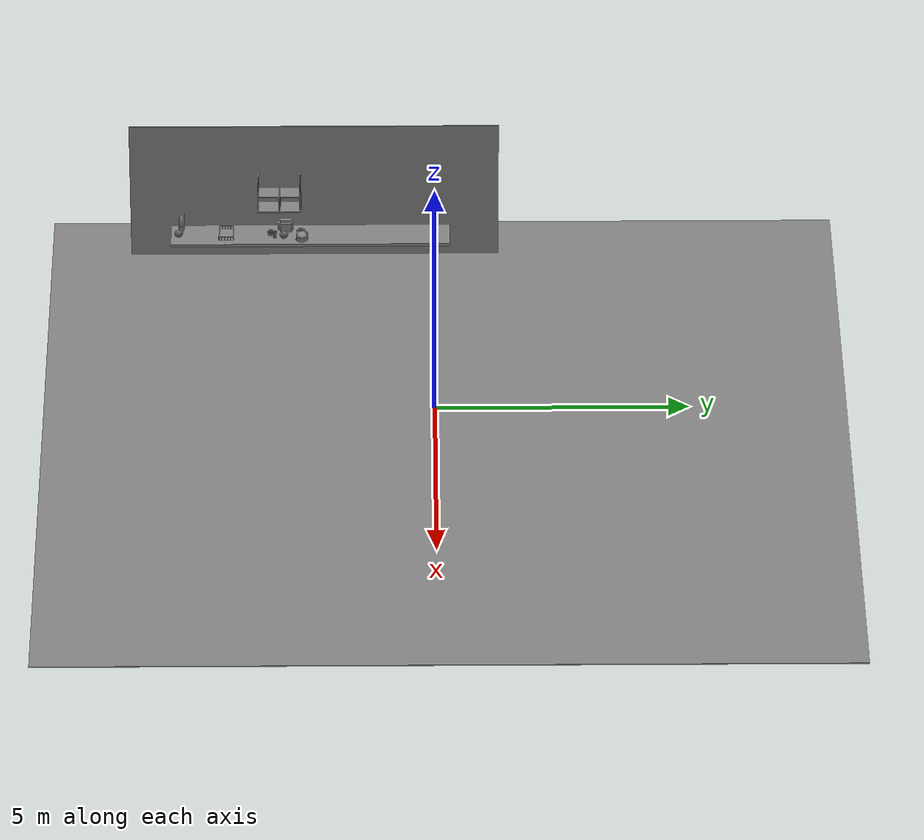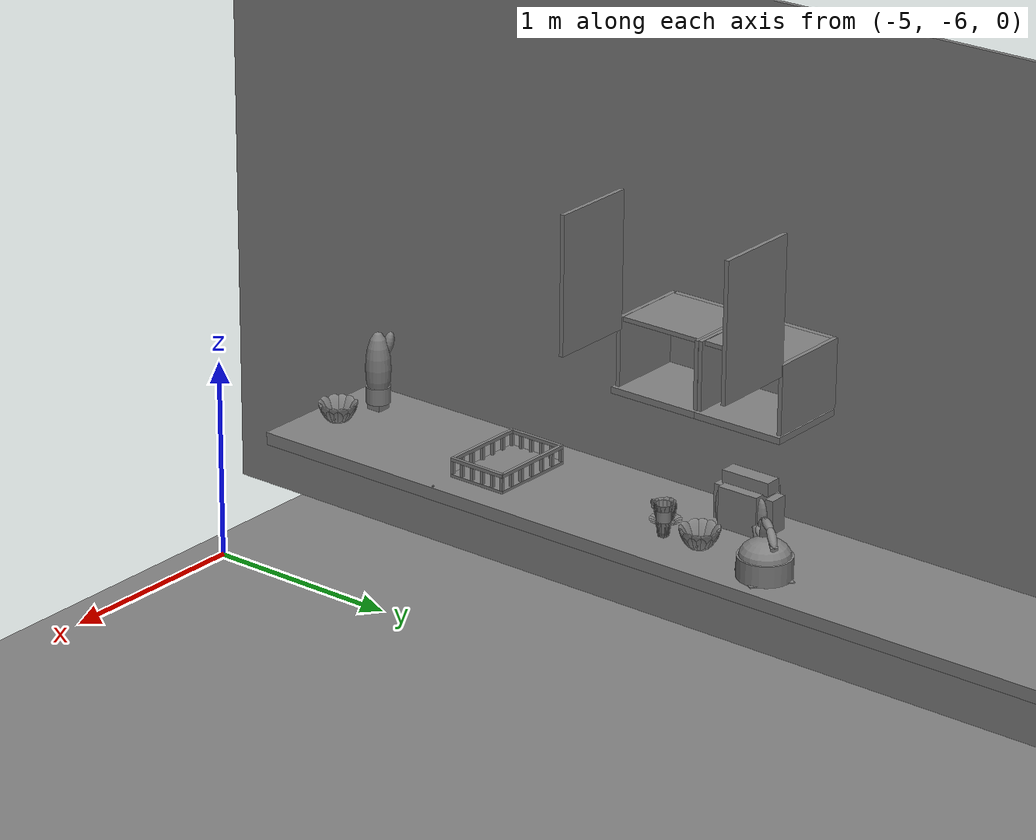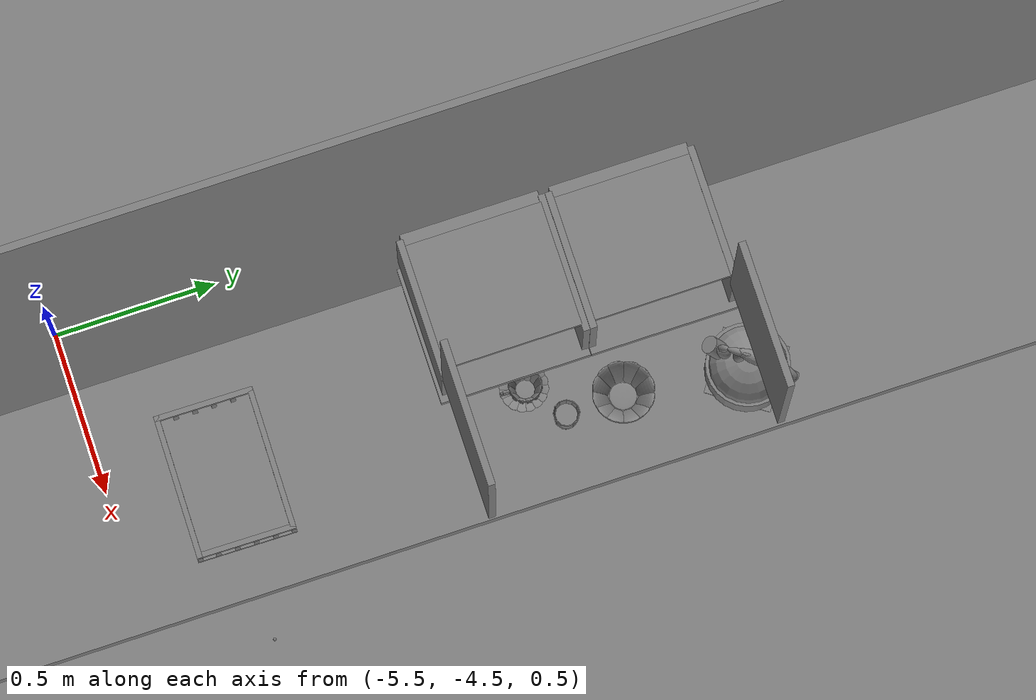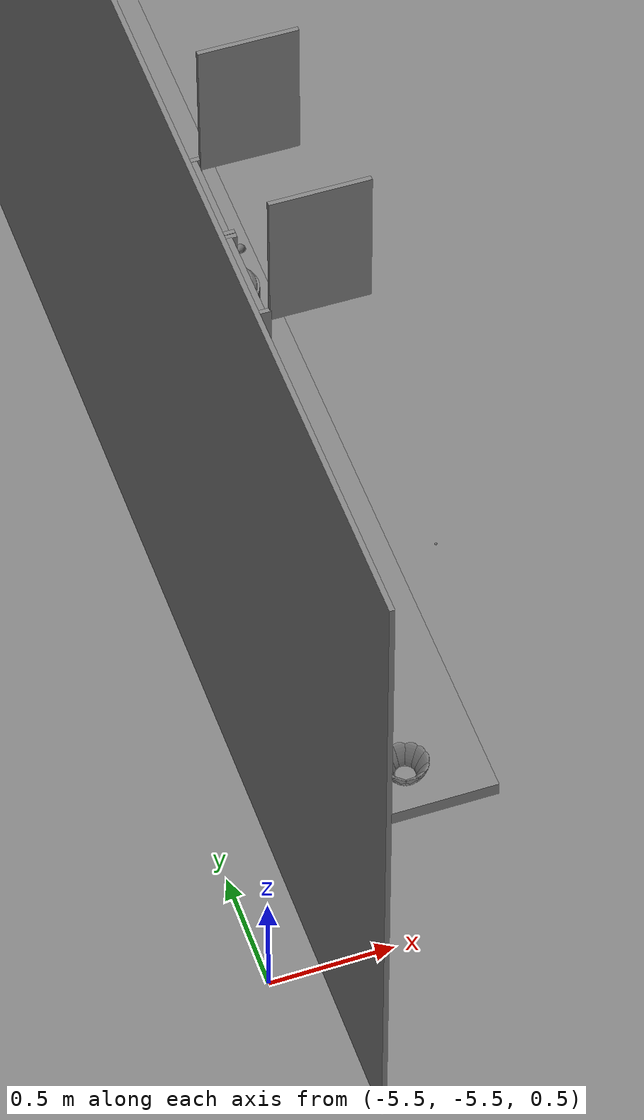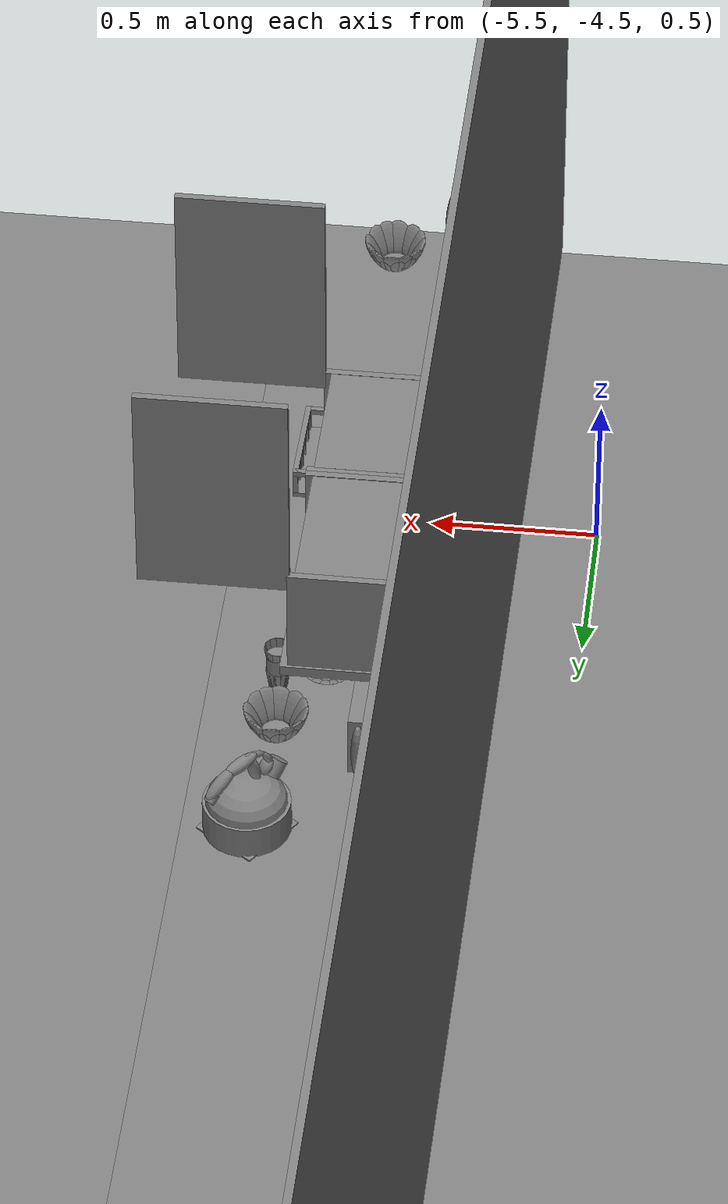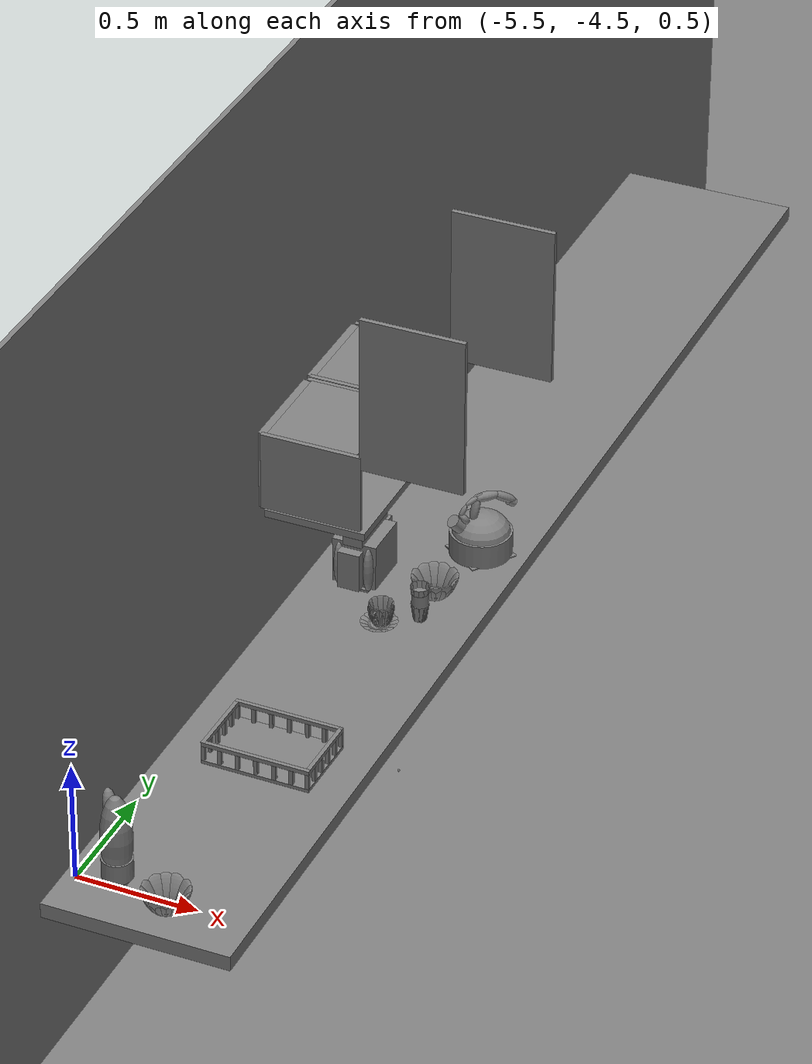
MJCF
<mujoco>
    <option gravity="0.000000000 0.000000000 -9.810000420" timestep="0.0049999999" integrator="implicitfast" density="9.8000002" viscosity="1.8000001e-05" noslip_iterations="10" iterations="100" sdf_iterations="50">
        <flag multiccd="disable"/>
    </option>
    <size memory="1000M"/>
    <compiler coordinate="local"/>
    <worldbody>
        <light cutoff="30" pos="0 1 1" dir="0 -1 -2"/>
        <light cutoff="30" pos="0 -1 1" dir="0 1 -2"/>
        <body pos="-4.860558510 -4.149443150 1.004824519" euler="0.000000000 0.000000000 -90.691093445" name="openloong_gripper_2f85_fix_base_usda_Basket_Kitchen_01">
            <geom contype="1" conaffinity="1" density="1000" type="box" material="" rgba="0.500000000 0.500000000 0.500000000 1.000000000" solimp="0.899999976 0.949999988 0.001000000" friction="1.000000000 0.005000000 0.000100000" solref="0.020000000 1.000000000" margin="0" condim="3" group="0" pos="0.086542509 0.207580954 0.047887992" quat="0.707107008 0.000000000 0.000000000 0.707106411" size="0.007600000 0.007600000 0.032000002" name="openloong_gripper_2f85_fix_base_usda_geom_181204AC_4908_4F9F_8B5D_73A36FCE5062"/>
            <geom contype="1" conaffinity="1" density="1000" type="box" material="" rgba="0.500000000 0.500000000 0.500000000 1.000000000" solimp="0.899999976 0.949999988 0.001000000" friction="1.000000000 0.005000000 0.000100000" solref="0.020000000 1.000000000" margin="0" condim="3" group="0" pos="-0.140816495 0.143605426 0.047889423" quat="0.707107008 0.000000000 0.000000000 0.707106411" size="0.007600000 0.007600000 0.032000002" name="openloong_gripper_2f85_fix_base_usda_geom_A1B378D8_F1DB_407E_BEED_3BABF4FCFAD9"/>
            <geom contype="1" conaffinity="1" density="1000" type="box" material="" rgba="0.500000000 0.500000000 0.500000000 1.000000000" solimp="0.899999976 0.949999988 0.001000000" friction="1.000000000 0.005000000 0.000100000" solref="0.020000000 1.000000000" margin="0" condim="3" group="0" pos="-0.140816212 -0.070956804 0.047888946" quat="0.707107008 0.000000000 0.000000000 0.707106411" size="0.007600000 0.007600000 0.032000002" name="openloong_gripper_2f85_fix_base_usda_geom_2DF9CB76_52B5_438B_8D7C_BAAC9F01F2CB"/>
            <geom contype="1" conaffinity="1" density="1000" type="box" material="" rgba="0.500000000 0.500000000 0.500000000 1.000000000" solimp="0.899999976 0.949999988 0.001000000" friction="1.000000000 0.005000000 0.000100000" solref="0.020000000 1.000000000" margin="0" condim="3" group="0" pos="0.140802577 0.207580566 0.047887899" quat="0.707107008 0.000000000 0.000000000 0.707106411" size="0.007600000 0.007600000 0.032000002" name="openloong_gripper_2f85_fix_base_usda_geom_67CFFAA1_8062_4785_8799_6B642ECAA4AE"/>
            <geom contype="1" conaffinity="1" density="1000" type="box" material="" rgba="0.500000000 0.500000000 0.500000000 1.000000000" solimp="0.899999976 0.949999988 0.001000000" friction="1.000000000 0.005000000 0.000100000" solref="0.020000000 1.000000000" margin="0" condim="3" group="0" pos="0.086541750 -0.207636267 0.047888279" quat="0.707107008 0.000000000 0.000000000 0.707106411" size="0.007600000 0.007600000 0.032000002" name="openloong_gripper_2f85_fix_base_usda_geom_182F1C98_A228_41DA_88C0_7B9D7686F644"/>
            <geom contype="1" conaffinity="1" density="1000" type="box" material="" rgba="0.500000000 0.500000000 0.500000000 1.000000000" solimp="0.899999976 0.949999988 0.001000000" friction="1.000000000 0.005000000 0.000100000" solref="0.020000000 1.000000000" margin="0" condim="3" group="0" pos="0.140633777 -0.000001907 0.087263681" quat="0.707107008 0.000000000 0.000000000 0.707106411" size="0.215199992 0.008000000 0.008400000" name="openloong_gripper_2f85_fix_base_usda_geom_801DAB1F_509B_408A_9BFE_E24D443083B6"/>
            <geom contype="1" conaffinity="1" density="1000" type="box" material="" rgba="0.500000000 0.500000000 0.500000000 1.000000000" solimp="0.899999976 0.949999988 0.001000000" friction="1.000000000 0.005000000 0.000100000" solref="0.020000000 1.000000000" margin="0" condim="3" group="0" pos="-0.027960587 -0.207636639 0.047888566" quat="0.707107008 0.000000000 0.000000000 0.707106411" size="0.007600000 0.007600000 0.032000002" name="openloong_gripper_2f85_fix_base_usda_geom_9DA84750_9718_4248_9BF5_CEE44FA6AD3C"/>
            <geom contype="1" conaffinity="1" density="1000" type="box" material="" rgba="0.500000000 0.500000000 0.500000000 1.000000000" solimp="0.899999976 0.949999988 0.001000000" friction="1.000000000 0.005000000 0.000100000" solref="0.020000000 1.000000000" margin="0" condim="3" group="0" pos="-0.140816122 -0.141625211 0.047888853" quat="0.707107008 0.000000000 0.000000000 0.707106411" size="0.007600000 0.007600000 0.032000002" name="openloong_gripper_2f85_fix_base_usda_geom_6FF6E210_18FF_4019_B631_C23AC4403335"/>
            <geom contype="1" conaffinity="1" density="1000" type="box" material="" rgba="0.500000000 0.500000000 0.500000000 1.000000000" solimp="0.899999976 0.949999988 0.001000000" friction="1.000000000 0.005000000 0.000100000" solref="0.020000000 1.000000000" margin="0" condim="3" group="0" pos="-0.140816122 0.207580194 0.047888756" quat="0.707107008 0.000000000 0.000000000 0.707106411" size="0.007600000 0.007600000 0.032000002" name="openloong_gripper_2f85_fix_base_usda_geom_A1A06DE3_0472_439D_9C59_4A4468E99EA0"/>
            <geom contype="1" conaffinity="1" density="1000" type="box" material="" rgba="0.500000000 0.500000000 0.500000000 1.000000000" solimp="0.899999976 0.949999988 0.001000000" friction="1.000000000 0.005000000 0.000100000" solref="0.020000000 1.000000000" margin="0" condim="3" group="0" pos="0.140800864 -0.070956804 0.047888376" quat="0.707107008 0.000000000 0.000000000 0.707106411" size="0.007600000 0.007600000 0.032000002" name="openloong_gripper_2f85_fix_base_usda_geom_D084CA30_8F7A_4A81_A999_D5E9D7C619D7"/>
            <geom contype="1" conaffinity="1" density="1000" type="box" material="" rgba="0.500000000 0.500000000 0.500000000 1.000000000" solimp="0.899999976 0.949999988 0.001000000" friction="1.000000000 0.005000000 0.000100000" solref="0.020000000 1.000000000" margin="0" condim="3" group="0" pos="0.140800476 0.002393341 0.047888376" quat="0.707107008 0.000000000 0.000000000 0.707106411" size="0.007600000 0.007600000 0.032000002" name="openloong_gripper_2f85_fix_base_usda_geom_4DA19836_FD4E_4B3E_9F19_F3FC98398988"/>
            <geom contype="1" conaffinity="1" density="1000" type="box" material="" rgba="0.500000000 0.500000000 0.500000000 1.000000000" solimp="0.899999976 0.949999988 0.001000000" friction="1.000000000 0.005000000 0.000100000" solref="0.020000000 1.000000000" margin="0" condim="3" group="0" pos="-0.140543848 -0.000001526 0.087263964" quat="0.707107008 0.000000000 0.000000000 0.707106411" size="0.215199992 0.008000000 0.008400000" name="openloong_gripper_2f85_fix_base_usda_geom_28AD7B9D_402C_4065_9EC7_D7DCCB1FDFD1"/>
            <geom contype="1" conaffinity="1" density="1000" type="box" material="" rgba="0.500000000 0.500000000 0.500000000 1.000000000" solimp="0.899999976 0.949999988 0.001000000" friction="1.000000000 0.005000000 0.000100000" solref="0.020000000 1.000000000" margin="0" condim="3" group="0" pos="-0.140816018 0.075380705 0.047889233" quat="0.707107008 0.000000000 0.000000000 0.707106411" size="0.007600000 0.007600000 0.032000002" name="openloong_gripper_2f85_fix_base_usda_geom_A21AEF5C_FFAE_4691_A8B0_5CBCF0DE51F0"/>
            <geom contype="1" conaffinity="1" density="1000" type="box" material="" rgba="0.500000000 0.500000000 0.500000000 1.000000000" solimp="0.899999976 0.949999988 0.001000000" friction="1.000000000 0.005000000 0.000100000" solref="0.020000000 1.000000000" margin="0" condim="3" group="0" pos="0.140801147 -0.141625211 0.047888279" quat="0.707107008 0.000000000 0.000000000 0.707106411" size="0.007600000 0.007600000 0.032000002" name="openloong_gripper_2f85_fix_base_usda_geom_701A7E57_3C0B_4F48_B507_463CB51A6E86"/>
            <geom contype="1" conaffinity="1" density="1000" type="box" material="" rgba="0.500000000 0.500000000 0.500000000 1.000000000" solimp="0.899999976 0.949999988 0.001000000" friction="1.000000000 0.005000000 0.000100000" solref="0.020000000 1.000000000" margin="0" condim="3" group="0" pos="0.000000000 -0.207717523 0.087263964" quat="0.707107008 0.000000000 0.000000000 0.707106411" size="0.008000000 0.148000002 0.008400000" name="openloong_gripper_2f85_fix_base_usda_geom_3707CA8E_1D18_487B_87CB_6E601AB132A3"/>
            <geom contype="1" conaffinity="1" density="1000" type="box" material="" rgba="0.500000000 0.500000000 0.500000000 1.000000000" solimp="0.899999976 0.949999988 0.001000000" friction="1.000000000 0.005000000 0.000100000" solref="0.020000000 1.000000000" margin="0" condim="3" group="0" pos="0.029044246 -0.207635880 0.047888376" quat="0.707107008 0.000000000 0.000000000 0.707106411" size="0.007600000 0.007600000 0.032000002" name="openloong_gripper_2f85_fix_base_usda_geom_DAFB4F07_12A8_431E_9FFA_F3DC716DFC08"/>
            <geom contype="1" conaffinity="1" density="1000" type="box" material="" rgba="0.500000000 0.500000000 0.500000000 1.000000000" solimp="0.899999976 0.949999988 0.001000000" friction="1.000000000 0.005000000 0.000100000" solref="0.020000000 1.000000000" margin="0" condim="3" group="0" pos="0.140800476 0.075379565 0.047888566" quat="0.707107008 0.000000000 0.000000000 0.707106411" size="0.007600000 0.007600000 0.032000002" name="openloong_gripper_2f85_fix_base_usda_geom_18576777_34E7_461D_98E9_F646B0C06A4D"/>
            <geom contype="1" conaffinity="1" density="1000" type="box" material="" rgba="0.500000000 0.500000000 0.500000000 1.000000000" solimp="0.899999976 0.949999988 0.001000000" friction="1.000000000 0.005000000 0.000100000" solref="0.020000000 1.000000000" margin="0" condim="3" group="0" pos="-0.027959539 0.207580566 0.047888376" quat="0.707107008 0.000000000 0.000000000 0.707106411" size="0.007600000 0.007600000 0.032000002" name="openloong_gripper_2f85_fix_base_usda_geom_2E43EA78_F33B_4165_984E_9F4672BF5929"/>
            <geom contype="1" conaffinity="1" density="1000" type="box" material="" rgba="0.500000000 0.500000000 0.500000000 1.000000000" solimp="0.899999976 0.949999988 0.001000000" friction="1.000000000 0.005000000 0.000100000" solref="0.020000000 1.000000000" margin="0" condim="3" group="0" pos="0.140799999 0.143604279 0.047888756" quat="0.707107008 0.000000000 0.000000000 0.707106411" size="0.007600000 0.007600000 0.032000002" name="openloong_gripper_2f85_fix_base_usda_geom_AF85263A_A8E1_4DA5_82F7_D7069CE42F1A"/>
            <geom contype="1" conaffinity="1" density="1000" type="box" material="" rgba="0.500000000 0.500000000 0.500000000 1.000000000" solimp="0.899999976 0.949999988 0.001000000" friction="1.000000000 0.005000000 0.000100000" solref="0.020000000 1.000000000" margin="0" condim="3" group="0" pos="-0.140816122 0.002393723 0.047889233" quat="0.707107008 0.000000000 0.000000000 0.707106411" size="0.007600000 0.007600000 0.032000002" name="openloong_gripper_2f85_fix_base_usda_geom_180CF7A0_1F46_4E03_9C2B_C098FE220F5C"/>
            <geom contype="1" conaffinity="1" density="1000" type="box" material="" rgba="0.500000000 0.500000000 0.500000000 1.000000000" solimp="0.899999976 0.949999988 0.001000000" friction="1.000000000 0.005000000 0.000100000" solref="0.020000000 1.000000000" margin="0" condim="3" group="0" pos="-0.085476689 0.207580194 0.047888566" quat="0.707107008 0.000000000 0.000000000 0.707106411" size="0.007600000 0.007600000 0.032000002" name="openloong_gripper_2f85_fix_base_usda_geom_4CB95CCB_266E_422F_A850_4E2D303CB052"/>
            <geom contype="1" conaffinity="1" density="1000" type="box" material="" rgba="0.500000000 0.500000000 0.500000000 1.000000000" solimp="0.899999976 0.949999988 0.001000000" friction="1.000000000 0.005000000 0.000100000" solref="0.020000000 1.000000000" margin="0" condim="3" group="0" pos="0.000000000 0.207718283 0.087263964" quat="0.707107008 0.000000000 0.000000000 0.707106411" size="0.008000000 0.148000002 0.008400000" name="openloong_gripper_2f85_fix_base_usda_geom_FBA306B9_0242_4814_AD75_6F91E71DFFED"/>
            <geom contype="1" conaffinity="1" density="1000" type="box" material="" rgba="0.500000000 0.500000000 0.500000000 1.000000000" solimp="0.899999976 0.949999988 0.001000000" friction="1.000000000 0.005000000 0.000100000" solref="0.020000000 1.000000000" margin="0" condim="3" group="0" pos="0.029045582 0.207581714 0.047888279" quat="0.707107008 0.000000000 0.000000000 0.707106411" size="0.007600000 0.007600000 0.032000002" name="openloong_gripper_2f85_fix_base_usda_geom_0E54AE1C_BE45_4CD8_A513_4DEBCAFB97C9"/>
            <geom contype="1" conaffinity="1" density="1000" type="box" material="" rgba="0.500000000 0.500000000 0.500000000 1.000000000" solimp="0.899999976 0.949999988 0.001000000" friction="1.000000000 0.005000000 0.000100000" solref="0.020000000 1.000000000" margin="0" condim="3" group="0" pos="-0.140816122 -0.207636267 0.047888853" quat="0.707107008 0.000000000 0.000000000 0.707106411" size="0.007600000 0.007600000 0.032000002" name="openloong_gripper_2f85_fix_base_usda_geom_68CA7060_5374_409B_8DD8_D0709C8307B9"/>
            <geom contype="1" conaffinity="1" density="1000" type="box" material="" rgba="0.500000000 0.500000000 0.500000000 1.000000000" solimp="0.899999976 0.949999988 0.001000000" friction="1.000000000 0.005000000 0.000100000" solref="0.020000000 1.000000000" margin="0" condim="3" group="0" pos="-0.085477069 -0.207636639 0.047888756" quat="0.707107008 0.000000000 0.000000000 0.707106411" size="0.007600000 0.007600000 0.032000002" name="openloong_gripper_2f85_fix_base_usda_geom_F72E296B_11A4_4296_8217_E045517FCB39"/>
            <geom contype="1" conaffinity="1" density="1000" type="box" material="" rgba="0.500000000 0.500000000 0.500000000 1.000000000" solimp="0.899999976 0.949999988 0.001000000" friction="1.000000000 0.005000000 0.000100000" solref="0.020000000 1.000000000" margin="0" condim="3" group="0" pos="-0.000012112 0.000000381 0.008534336" quat="0.707107008 0.000000000 0.000000000 0.707106411" size="0.215199992 0.148800001 0.008400000" name="openloong_gripper_2f85_fix_base_usda_geom_81D72D24_5485_4EA0_A92F_FE24A4CE4B55"/>
            <geom contype="1" conaffinity="1" density="1000" type="box" material="" rgba="0.500000000 0.500000000 0.500000000 1.000000000" solimp="0.899999976 0.949999988 0.001000000" friction="1.000000000 0.005000000 0.000100000" solref="0.020000000 1.000000000" margin="0" condim="3" group="0" pos="0.140801623 -0.207636267 0.047888186" quat="0.707107008 0.000000000 0.000000000 0.707106411" size="0.007600000 0.007600000 0.032000002" name="openloong_gripper_2f85_fix_base_usda_geom_870AD9CD_C72B_4A4A_80B5_EEEF34307CBB"/>
            <freejoint name="openloong_gripper_2f85_fix_base_usda_Basket_Kitchen_01_joint"/>
            <site size="0.005000000 0.005000000 0.005000000" rgba="0.500000000 0.500000000 0.500000000 1.000000000" pos="0.000000000 0.000000000 0.000000000" quat="1.000000000 0.000000000 0.000000000 0.000000000" group="0" type="sphere" name="openloong_gripper_2f85_fix_base_usda_Basket_Kitchen_01site"/>
        </body>
        <body pos="-4.721817970 -2.990536690 1.027358174" euler="0.000000000 0.000000000 89.999946594" name="Interactive Objcets_bow_02">
            <geom contype="1" conaffinity="1" density="1000" type="ellipsoid" material="" rgba="0.500000000 0.500000000 0.500000000 1.000000000" solimp="0.899999976 0.949999988 0.001000000" friction="1.000000000 0.005000000 0.000100000" solref="0.020000000 1.000000000" margin="0" condim="3" group="0" pos="-0.058925860 -0.029528141 0.044118762" quat="0.223252773 0.231952101 0.054787740 -0.945174515" size="0.010000000 0.039999999 0.052000001" name="Interactive Objcets_geom_242D0CD8_656C_412B_9D67_687E0F1A38CB"/>
            <geom contype="1" conaffinity="1" density="1000" type="ellipsoid" material="" rgba="0.500000000 0.500000000 0.500000000 1.000000000" solimp="0.899999976 0.949999988 0.001000000" friction="1.000000000 0.005000000 0.000100000" solref="0.020000000 1.000000000" margin="0" condim="3" group="0" pos="0.000082973 0.000000000 0.000446677" quat="1.000000000 0.000000000 0.000000000 0.000000000" size="0.039999999 0.039999999 0.002000000" name="Interactive Objcets_geom_A514A5A8_2ABA_451C_BBFC_84546B11DF8B"/>
            <geom contype="1" conaffinity="1" density="1000" type="ellipsoid" material="" rgba="0.500000000 0.500000000 0.500000000 1.000000000" solimp="0.899999976 0.949999988 0.001000000" friction="1.000000000 0.005000000 0.000100000" solref="0.020000000 1.000000000" margin="0" condim="3" group="0" pos="0.029448029 -0.059084892 0.044118762" quat="0.825555801 0.125530601 0.202597082 -0.511521280" size="0.010000000 0.039999999 0.052000001" name="Interactive Objcets_geom_406CE1FD_BD9A_4724_996E_8564F6718A4F"/>
            <geom contype="1" conaffinity="1" density="1000" type="ellipsoid" material="" rgba="0.500000000 0.500000000 0.500000000 1.000000000" solimp="0.899999976 0.949999988 0.001000000" friction="1.000000000 0.005000000 0.000100000" solref="0.020000000 1.000000000" margin="0" condim="3" group="0" pos="0.000082973 0.000000000 0.005656481" quat="1.000000000 0.000000000 0.000000000 0.000000000" size="0.039999999 0.039999999 0.002000000" name="Interactive Objcets_geom_C8DC7C3C_90CF_4C67_BA49_CAEE57B19CE7"/>
            <geom contype="1" conaffinity="1" density="1000" type="ellipsoid" material="" rgba="0.500000000 0.500000000 0.500000000 1.000000000" solimp="0.899999976 0.949999988 0.001000000" friction="1.000000000 0.005000000 0.000100000" solref="0.020000000 1.000000000" margin="0" condim="3" group="0" pos="-0.040080305 -0.052354336 0.044118762" quat="0.429593205 0.213749886 0.105425082 -0.871003032" size="0.010000000 0.039999999 0.052000001" name="Interactive Objcets_geom_BDFE2B98_2FF1_4FB2_88C5_657E5317B087"/>
            <geom contype="1" conaffinity="1" density="1000" type="ellipsoid" material="" rgba="0.500000000 0.500000000 0.500000000 1.000000000" solimp="0.899999976 0.949999988 0.001000000" friction="1.000000000 0.005000000 0.000100000" solref="0.020000000 1.000000000" margin="0" condim="3" group="0" pos="-0.065898418 -0.000007629 0.044118762" quat="0.971183062 -0.000000142 -0.238334835 0.000000030" size="0.010000000 0.039999999 0.052000001" name="Interactive Objcets_geom_E9368F02_431C_42E3_BE6C_42672416F562"/>
            <geom contype="1" conaffinity="1" density="1000" type="ellipsoid" material="" rgba="0.500000000 0.500000000 0.500000000 1.000000000" solimp="0.899999976 0.949999988 0.001000000" friction="1.000000000 0.005000000 0.000100000" solref="0.020000000 1.000000000" margin="0" condim="3" group="0" pos="0.059080135 0.029512405 0.044118762" quat="0.223252743 -0.231952220 -0.054787420 -0.945174456" size="0.010000000 0.039999999 0.052000001" name="Interactive Objcets_geom_400E2EC7_8C44_4D8E_8701_84854C7901D2"/>
            <geom contype="1" conaffinity="1" density="1000" type="ellipsoid" material="" rgba="0.500000000 0.500000000 0.500000000 1.000000000" solimp="0.899999976 0.949999988 0.001000000" friction="1.000000000 0.005000000 0.000100000" solref="0.020000000 1.000000000" margin="0" condim="3" group="0" pos="0.066052437 -0.000007629 0.044118762" quat="0.971183062 -0.000000156 0.238334835 0.000000030" size="0.010000000 0.039999999 0.052000001" name="Interactive Objcets_geom_41C94375_074B_4A7F_A30F_E0264ED3E2D4"/>
            <geom contype="1" conaffinity="1" density="1000" type="ellipsoid" material="" rgba="0.500000000 0.500000000 0.500000000 1.000000000" solimp="0.899999976 0.949999988 0.001000000" friction="1.000000000 0.005000000 0.000100000" solref="0.020000000 1.000000000" margin="0" condim="3" group="0" pos="0.000243668 -0.065982819 0.044118762" quat="0.687598705 0.168314636 0.168741375 -0.685860336" size="0.010000000 0.039999999 0.052000001" name="Interactive Objcets_geom_01182AF7_38BC_41BE_AB1F_76E9F21A8319"/>
            <geom contype="1" conaffinity="1" density="1000" type="ellipsoid" material="" rgba="0.500000000 0.500000000 0.500000000 1.000000000" solimp="0.899999976 0.949999988 0.001000000" friction="1.000000000 0.005000000 0.000100000" solref="0.020000000 1.000000000" margin="0" condim="3" group="0" pos="-0.000090118 0.065967560 0.044118762" quat="0.687598705 -0.168314859 -0.168741152 -0.685860336" size="0.010000000 0.039999999 0.052000001" name="Interactive Objcets_geom_9DAF3B95_CBC3_4EC8_A19D_9EFED0E1BA0B"/>
            <geom contype="1" conaffinity="1" density="1000" type="ellipsoid" material="" rgba="0.500000000 0.500000000 0.500000000 1.000000000" solimp="0.899999976 0.949999988 0.001000000" friction="1.000000000 0.005000000 0.000100000" solref="0.020000000 1.000000000" margin="0" condim="3" group="0" pos="0.052321676 -0.040297508 0.044118762" quat="0.919264674 0.076882742 0.225593731 -0.313287675" size="0.010000000 0.039999999 0.052000001" name="Interactive Objcets_geom_039DA034_7BD5_4C73_9398_6F1C2C4B30C4"/>
            <geom contype="1" conaffinity="1" density="1000" type="ellipsoid" material="" rgba="0.500000000 0.500000000 0.500000000 1.000000000" solimp="0.899999976 0.949999988 0.001000000" friction="1.000000000 0.005000000 0.000100000" solref="0.020000000 1.000000000" margin="0" condim="3" group="0" pos="0.040234569 0.052338600 0.044118762" quat="0.429593176 -0.213750035 -0.105424814 -0.871002913" size="0.010000000 0.039999999 0.052000001" name="Interactive Objcets_geom_71A4E0A6_E615_4643_A453_58B31096F60C"/>
            <geom contype="1" conaffinity="1" density="1000" type="ellipsoid" material="" rgba="0.500000000 0.500000000 0.500000000 1.000000000" solimp="0.899999976 0.949999988 0.001000000" friction="1.000000000 0.005000000 0.000100000" solref="0.020000000 1.000000000" margin="0" condim="3" group="0" pos="-0.052167647 0.040282249 0.044118762" quat="0.919264615 -0.076883025 -0.225593641 -0.313287735" size="0.010000000 0.039999999 0.052000001" name="Interactive Objcets_geom_1257C7FF_BBA8_42F3_91CF_344AAF28E3A8"/>
            <geom contype="1" conaffinity="1" density="1000" type="ellipsoid" material="" rgba="0.500000000 0.500000000 0.500000000 1.000000000" solimp="0.899999976 0.949999988 0.001000000" friction="1.000000000 0.005000000 0.000100000" solref="0.020000000 1.000000000" margin="0" condim="3" group="0" pos="-0.029293532 0.059069633 0.044118762" quat="0.825555801 -0.125530809 -0.202596903 -0.511521280" size="0.010000000 0.039999999 0.052000001" name="Interactive Objcets_geom_F83EDEF7_2638_4BA5_8610_842793AD0589"/>
            <freejoint name="Interactive Objcets_bow_02"/>
        </body>
        <body pos="-4.802892208 -3.488179445 1.876015186" euler="89.999992371 -89.999946594 0.000000000" name="Interactive Objcets_guimen_01">
            <geom contype="1" conaffinity="1" density="1000" type="box" material="" rgba="0.500000000 0.500000000 0.500000000 1.000000000" solimp="0.899999976 0.949999988 0.001000000" friction="1.000000000 0.005000000 0.000100000" solref="0.020000000 1.000000000" margin="0" condim="3" group="0" pos="0.006727934 0.314709902 -0.203009605" quat="1.000000000 0.000000119 -0.000000119 0.000000000" size="0.010000000 0.317999989 0.204999998" name="Interactive Objcets_geom_A7AEA243_E4E8_4424_9AF3_B50DFB943E45"/>
            <joint armature="0" stiffness="0" damping="1" axis="0.000000 1.000000 0.000000" type="hinge" name="Interactive Objcets_guimen_01"/>
        </body>
        <body pos="-4.827295780 -3.287638187 1.074643731" euler="0.000000000 0.000000000 89.999992371" name="Interactive Objcets_coffeecup_01">
            <geom contype="1" conaffinity="1" density="1000" type="ellipsoid" material="" rgba="0.500000000 0.500000000 0.500000000 1.000000000" solimp="0.899999976 0.949999988 0.001000000" friction="1.000000000 0.005000000 0.000100000" solref="0.020000000 1.000000000" margin="0" condim="3" group="0" pos="0.053700209 0.033117294 0.002976775" quat="0.496025741 -0.082236379 -0.047260769 -0.863111615" size="0.005000000 0.029999999 0.048999999" name="Interactive Objcets_geom_F94D8C36_2993_46B7_966D_1383DB2DDF47"/>
            <geom contype="1" conaffinity="1" density="1000" type="ellipsoid" material="" rgba="0.500000000 0.500000000 0.500000000 1.000000000" solimp="0.899999976 0.949999988 0.001000000" friction="1.000000000 0.005000000 0.000100000" solref="0.020000000 1.000000000" margin="0" condim="3" group="0" pos="0.068445444 0.017385960 0.002976775" quat="0.228377223 -0.092319682 -0.021759447 -0.968941331" size="0.005000000 0.029999999 0.048999999" name="Interactive Objcets_geom_041A6840_6AC8_4923_8EB9_11472515A02C"/>
            <geom contype="1" conaffinity="1" density="1000" type="capsule" material="" rgba="0.500000000 0.500000000 0.500000000 1.000000000" solimp="0.899999976 0.949999988 0.001000000" friction="1.000000000 0.005000000 0.000100000" solref="0.020000000 1.000000000" margin="0" condim="3" group="0" pos="-0.030251026 0.000000000 0.004966617" quat="0.480583906 -0.000000000 0.876948774 -0.000000126" size="0.004000000 0.005000000 1.000000000" name="Interactive Objcets_geom_67101475_545A_479E_8DC3_11C659799154"/>
            <geom contype="1" conaffinity="1" density="1000" type="ellipsoid" material="" rgba="0.500000000 0.500000000 0.500000000 1.000000000" solimp="0.899999976 0.949999988 0.001000000" friction="1.000000000 0.005000000 0.000100000" solref="0.020000000 1.000000000" margin="0" condim="3" group="0" pos="0.034471050 -0.037125111 0.002976775" quat="0.701517045 0.067293778 0.066836871 -0.706313014" size="0.005000000 0.029999999 0.048999999" name="Interactive Objcets_geom_3F997DC2_E325_4D30_BE5B_3D2DA7ABDFCB"/>
            <geom contype="1" conaffinity="1" density="1000" type="ellipsoid" material="" rgba="0.500000000 0.500000000 0.500000000 1.000000000" solimp="0.899999976 0.949999988 0.001000000" friction="1.000000000 0.005000000 0.000100000" solref="0.020000000 1.000000000" margin="0" condim="3" group="0" pos="0.035336256 0.000558376 -0.045152068" quat="0.999999881 0.000000000 0.000000000 0.000000000" size="0.029999999 0.029999999 0.001000000" name="Interactive Objcets_geom_07FAAAE9_ADF4_4156_9231_912D408AD9C4"/>
            <geom contype="1" conaffinity="1" density="1000" type="capsule" material="" rgba="0.500000000 0.500000000 0.500000000 1.000000000" solimp="0.899999976 0.949999988 0.001000000" friction="1.000000000 0.005000000 0.000100000" solref="0.020000000 1.000000000" margin="0" condim="3" group="0" pos="-0.021276474 0.000000000 0.038509369" quat="0.633189917 0.000000000 0.773996413 0.000000000" size="0.004000000 0.009000000 1.000000000" name="Interactive Objcets_geom_89146582_2365_41A4_9714_21A196C100F7"/>
            <geom contype="1" conaffinity="1" density="1000" type="capsule" material="" rgba="0.500000000 0.500000000 0.500000000 1.000000000" solimp="0.899999976 0.949999988 0.001000000" friction="1.000000000 0.005000000 0.000100000" solref="0.020000000 1.000000000" margin="0" condim="3" group="0" pos="-0.018014431 0.000000000 0.001762271" quat="0.707106769 -0.000000004 0.707106709 -0.000000088" size="0.004000000 0.005000000 1.000000000" name="Interactive Objcets_geom_6E9ACF79_7D7E_400A_B749_D9823D689BBD"/>
            <geom contype="1" conaffinity="1" density="1000" type="ellipsoid" material="" rgba="0.500000000 0.500000000 0.500000000 1.000000000" solimp="0.899999976 0.949999988 0.001000000" friction="1.000000000 0.005000000 0.000100000" solref="0.020000000 1.000000000" margin="0" condim="3" group="0" pos="0.001010895 -0.016271591 0.002976775" quat="0.228377163 0.092315644 0.021758538 -0.968941689" size="0.005000000 0.029999999 0.048999999" name="Interactive Objcets_geom_46FB0AF9_DF75_4C0E_913D_A645840A39E5"/>
            <geom contype="1" conaffinity="1" density="1000" type="capsule" material="" rgba="0.500000000 0.500000000 0.500000000 1.000000000" solimp="0.899999976 0.949999988 0.001000000" friction="1.000000000 0.005000000 0.000100000" solref="0.020000000 1.000000000" margin="0" condim="3" group="0" pos="-0.008219719 0.000000000 -0.000944734" quat="0.364379913 0.000000063 0.931250274 -0.000000063" size="0.004000000 0.003000000 1.000000000" name="Interactive Objcets_geom_59CA7487_A043_4B27_AA4D_B8E61C3E5F1F"/>
            <geom contype="1" conaffinity="1" density="1000" type="ellipsoid" material="" rgba="0.500000000 0.500000000 0.500000000 1.000000000" solimp="0.899999976 0.949999988 0.001000000" friction="1.000000000 0.005000000 0.000100000" solref="0.020000000 1.000000000" margin="0" condim="3" group="0" pos="0.002039194 0.019308567 0.002976775" quat="0.961933970 -0.024419386 -0.091652036 -0.256293654" size="0.005000000 0.029999999 0.048999999" name="Interactive Objcets_geom_35038F7C_FA01_4D62_82D9_9C147E6F9847"/>
            <geom contype="1" conaffinity="1" density="1000" type="capsule" material="" rgba="0.500000000 0.500000000 0.500000000 1.000000000" solimp="0.899999976 0.949999988 0.001000000" friction="1.000000000 0.005000000 0.000100000" solref="0.020000000 1.000000000" margin="0" condim="3" group="0" pos="-0.033022881 0.000000000 0.037873149" quat="0.874267220 0.000000042 0.485444903 -0.000000084" size="0.004000000 0.004000000 1.000000000" name="Interactive Objcets_geom_2A27D9CD_A06F_4EFF_AE46_6D38284CE31E"/>
            <geom contype="1" conaffinity="1" density="1000" type="ellipsoid" material="" rgba="0.500000000 0.500000000 0.500000000 1.000000000" solimp="0.899999976 0.949999988 0.001000000" friction="1.000000000 0.005000000 0.000100000" solref="0.020000000 1.000000000" margin="0" condim="3" group="0" pos="0.034984604 0.038240910 0.002976775" quat="0.701516926 -0.067296736 -0.066839755 -0.706312656" size="0.005000000 0.029999999 0.048999999" name="Interactive Objcets_geom_D550CC5C_56F5_41D6_AE08_3C690B69E5D0"/>
            <geom contype="1" conaffinity="1" density="1000" type="ellipsoid" material="" rgba="0.500000000 0.500000000 0.500000000 1.000000000" solimp="0.899999976 0.949999988 0.001000000" friction="1.000000000 0.005000000 0.000100000" solref="0.020000000 1.000000000" margin="0" condim="3" group="0" pos="-0.002956629 0.000558376 0.002976775" quat="0.995491505 0.000000004 -0.094849378 -0.000000089" size="0.005000000 0.029999999 0.048999999" name="Interactive Objcets_geom_BC1881DB_2ADC_4076_AAAC_DB2EA801474D"/>
            <geom contype="1" conaffinity="1" density="1000" type="ellipsoid" material="" rgba="0.500000000 0.500000000 0.500000000 1.000000000" solimp="0.899999976 0.949999988 0.001000000" friction="1.000000000 0.005000000 0.000100000" solref="0.020000000 1.000000000" margin="0" condim="3" group="0" pos="0.017669693 0.034160614 0.002976775" quat="0.848410904 -0.049618516 -0.080835648 -0.520770907" size="0.005000000 0.029999999 0.048999999" name="Interactive Objcets_geom_36BB5976_0E51_4E12_A253_BEB8D016C0FA"/>
            <geom contype="1" conaffinity="1" density="1000" type="ellipsoid" material="" rgba="0.500000000 0.500000000 0.500000000 1.000000000" solimp="0.899999976 0.949999988 0.001000000" friction="1.000000000 0.005000000 0.000100000" solref="0.020000000 1.000000000" margin="0" condim="3" group="0" pos="0.051787138 -0.033043861 0.002976775" quat="0.848411202 0.049616337 0.080832161 -0.520771146" size="0.005000000 0.029999999 0.048999999" name="Interactive Objcets_geom_ECF2F156_761F_4499_AAD8_5B2C6CFCF715"/>
            <geom contype="1" conaffinity="1" density="1000" type="ellipsoid" material="" rgba="0.500000000 0.500000000 0.500000000 1.000000000" solimp="0.899999976 0.949999988 0.001000000" friction="1.000000000 0.005000000 0.000100000" solref="0.020000000 1.000000000" margin="0" condim="3" group="0" pos="0.035336256 0.000558376 -0.043215394" quat="0.999999881 0.000000000 0.000000000 0.000000000" size="0.029999999 0.029999999 0.001000000" name="Interactive Objcets_geom_EFDE0183_8A29_4101_9A87_32D4D47D3647"/>
            <geom contype="1" conaffinity="1" density="1000" type="capsule" material="" rgba="0.500000000 0.500000000 0.500000000 1.000000000" solimp="0.899999976 0.949999988 0.001000000" friction="1.000000000 0.005000000 0.000100000" solref="0.020000000 1.000000000" margin="0" condim="3" group="0" pos="-0.036300898 0.000000000 0.021037936" quat="0.044551343 -0.000000000 0.999007046 -0.000000126" size="0.004000000 0.012000000 1.000000000" name="Interactive Objcets_geom_B0582C04_28CA_48D4_935F_3EE8345165AB"/>
            <geom contype="1" conaffinity="1" density="1000" type="ellipsoid" material="" rgba="0.500000000 0.500000000 0.500000000 1.000000000" solimp="0.899999976 0.949999988 0.001000000" friction="1.000000000 0.005000000 0.000100000" solref="0.020000000 1.000000000" margin="0" condim="3" group="0" pos="0.067416430 -0.018191338 0.002976775" quat="0.961934388 0.024418317 0.091648072 -0.256293803" size="0.005000000 0.029999999 0.048999999" name="Interactive Objcets_geom_13FB1AD7_70C9_49A6_A793_E60D9DCAA344"/>
            <geom contype="1" conaffinity="1" density="1000" type="ellipsoid" material="" rgba="0.500000000 0.500000000 0.500000000 1.000000000" solimp="0.899999976 0.949999988 0.001000000" friction="1.000000000 0.005000000 0.000100000" solref="0.020000000 1.000000000" margin="0" condim="3" group="0" pos="0.015755907 -0.032001972 0.002976775" quat="0.496025920 0.082232773 0.047258731 -0.863112032" size="0.005000000 0.029999999 0.048999999" name="Interactive Objcets_geom_54C3EA79_1AF9_48E2_8D43_C8B6E3BAC41C"/>
            <geom contype="1" conaffinity="1" density="1000" type="ellipsoid" material="" rgba="0.500000000 0.500000000 0.500000000 1.000000000" solimp="0.899999976 0.949999988 0.001000000" friction="1.000000000 0.005000000 0.000100000" solref="0.020000000 1.000000000" margin="0" condim="3" group="0" pos="0.072411790 0.000558376 0.002976775" quat="0.995491922 -0.000000019 0.094845265 -0.000000089" size="0.005000000 0.029999999 0.048999999" name="Interactive Objcets_geom_A9222497_4D8B_4F76_8FF1_E017F37E6C53"/>
            <freejoint name="Interactive Objcets_coffeecup_01"/>
        </body>
        <body pos="-4.805274963 -2.665403366 1.876015186" euler="89.999877930 89.999969482 0.000000000" name="Interactive Objcets_guimen_02">
            <geom contype="1" conaffinity="1" density="1000" type="box" material="" rgba="0.500000000 0.500000000 0.500000000 1.000000000" solimp="0.899999976 0.949999988 0.001000000" friction="1.000000000 0.005000000 0.000100000" solref="0.020000000 1.000000000" margin="0" condim="3" group="0" pos="0.006727815 0.314709663 0.203009367" quat="0.999999940 0.000000000 0.000000000 0.000000000" size="0.010000000 0.317999989 0.204999998" name="Interactive Objcets_geom_97B3A008_C740_4673_B6E4_122B6B99FEC5"/>
            <joint armature="0" stiffness="0" damping="1" axis="0.000000 1.000000 0.000000" type="hinge" name="Interactive Objcets_guimen_02"/>
        </body>
        <body pos="-4.705342293 -3.169416904 1.103703976" euler="0.000000000 0.000000000 0.000000000" name="Interactive Objcets_cup_02">
            <geom contype="1" conaffinity="1" density="1000" type="box" material="" rgba="0.500000000 0.500000000 0.500000000 1.000000000" solimp="0.899999976 0.949999988 0.001000000" friction="1.000000000 0.005000000 0.000100000" solref="0.020000000 1.000000000" margin="0" condim="3" group="0" pos="-0.016875744 0.022189617 -0.037281752" quat="0.944716334 -0.074092269 -0.024973858 0.318430305" size="0.010000000 0.001000000 0.035000000" name="Interactive Objcets_geom_9A70B0AF_64A0_4BAF_993E_1DF338822911"/>
            <geom contype="1" conaffinity="1" density="1000" type="box" material="" rgba="0.500000000 0.500000000 0.500000000 1.000000000" solimp="0.899999976 0.949999988 0.001000000" friction="1.000000000 0.005000000 0.000100000" solref="0.020000000 1.000000000" margin="0" condim="3" group="0" pos="0.029378891 -0.018181801 0.062637210" quat="0.870895982 0.068302706 0.038053915 0.485208035" size="0.010000000 0.001000000 0.015000000" name="Interactive Objcets_geom_A4693F49_BF00_4478_A553_318513DC453F"/>
            <geom contype="1" conaffinity="1" density="1000" type="box" material="" rgba="0.500000000 0.500000000 0.500000000 1.000000000" solimp="0.899999976 0.949999988 0.001000000" friction="1.000000000 0.005000000 0.000100000" solref="0.020000000 1.000000000" margin="0" condim="3" group="0" pos="0.027999878 0.000000000 -0.037281752" quat="0.704941988 -0.055288255 0.055288251 -0.704942048" size="0.010000000 0.001000000 0.035000000" name="Interactive Objcets_geom_71E33FA5_6B3B_4D3A_9686_7ECA8ED53C84"/>
            <geom contype="1" conaffinity="1" density="1000" type="box" material="" rgba="0.500000000 0.500000000 0.500000000 1.000000000" solimp="0.899999976 0.949999988 0.001000000" friction="1.000000000 0.005000000 0.000100000" solref="0.020000000 1.000000000" margin="0" condim="3" group="0" pos="0.022285938 0.016949892 -0.037281752" quat="0.893179297 -0.070051625 0.034732576 -0.442851186" size="0.010000000 0.001000000 0.035000000" name="Interactive Objcets_geom_AE8D6A51_34CF_47E4_98BB_20412D42681B"/>
            <geom contype="1" conaffinity="1" density="1000" type="cylinder" material="" rgba="0.500000000 0.500000000 0.500000000 1.000000000" solimp="0.899999976 0.949999988 0.001000000" friction="1.000000000 0.005000000 0.000100000" solref="0.020000000 1.000000000" margin="0" condim="3" group="0" pos="0.000000000 0.000000000 0.022491097" quat="1.000000000 0.000000030 0.000000000 0.000000000" size="0.033000000 0.025000000 1.000000000" name="Interactive Objcets_geom_B3F44D1E_63C4_428E_B51C_ABBB84DEF9FB"/>
            <geom contype="1" conaffinity="1" density="1000" type="box" material="" rgba="0.500000000 0.500000000 0.500000000 1.000000000" solimp="0.899999976 0.949999988 0.001000000" friction="1.000000000 0.005000000 0.000100000" solref="0.020000000 1.000000000" margin="0" condim="3" group="0" pos="0.000000000 0.034549713 0.062637210" quat="0.996938646 -0.078187965 0.000000000 0.000000000" size="0.010000000 0.001000000 0.015000000" name="Interactive Objcets_geom_65A12361_3FFA_442C_947E_C19A62617C51"/>
            <geom contype="1" conaffinity="1" density="1000" type="box" material="" rgba="0.500000000 0.500000000 0.500000000 1.000000000" solimp="0.899999976 0.949999988 0.001000000" friction="1.000000000 0.005000000 0.000100000" solref="0.020000000 1.000000000" margin="0" condim="3" group="0" pos="-0.018181324 -0.029377937 0.062637210" quat="0.958910167 0.075206861 -0.021389510 -0.272722572" size="0.010000000 0.001000000 0.015000000" name="Interactive Objcets_geom_32F0AF1D_8647_4C4F_9172_B44D5FA46A53"/>
            <geom contype="1" conaffinity="1" density="1000" type="box" material="" rgba="0.500000000 0.500000000 0.500000000 1.000000000" solimp="0.899999976 0.949999988 0.001000000" friction="1.000000000 0.005000000 0.000100000" solref="0.020000000 1.000000000" margin="0" condim="3" group="0" pos="-0.034549713 0.000000000 0.062637210" quat="0.704941988 0.055288255 -0.055288251 -0.704942048" size="0.010000000 0.001000000 0.015000000" name="Interactive Objcets_geom_F9D77749_22E0_4080_9BE4_1D06B69AEC74"/>
            <geom contype="1" conaffinity="1" density="1000" type="box" material="" rgba="0.500000000 0.500000000 0.500000000 1.000000000" solimp="0.899999976 0.949999988 0.001000000" friction="1.000000000 0.005000000 0.000100000" solref="0.020000000 1.000000000" margin="0" condim="3" group="0" pos="0.011943817 0.025323629 -0.037281752" quat="0.972834349 -0.076298930 0.017089661 -0.217898533" size="0.010000000 0.001000000 0.035000000" name="Interactive Objcets_geom_8F58DAC6_A01A_46E1_8865_34111ECCF4E6"/>
            <geom contype="1" conaffinity="1" density="1000" type="box" material="" rgba="0.500000000 0.500000000 0.500000000 1.000000000" solimp="0.899999976 0.949999988 0.001000000" friction="1.000000000 0.005000000 0.000100000" solref="0.020000000 1.000000000" margin="0" condim="3" group="0" pos="0.017436981 -0.029826880 0.062637210" quat="0.962265730 0.075468659 0.020441191 0.260636479" size="0.010000000 0.001000000 0.015000000" name="Interactive Objcets_geom_4A099245_764B_4063_94E4_1BC177F449DE"/>
            <geom contype="1" conaffinity="1" density="1000" type="box" material="" rgba="0.500000000 0.500000000 0.500000000 1.000000000" solimp="0.899999976 0.949999988 0.001000000" friction="1.000000000 0.005000000 0.000100000" solref="0.020000000 1.000000000" margin="0" condim="3" group="0" pos="0.000000000 -0.034549713 0.062637210" quat="0.996938646 0.078187965 0.000000000 0.000000000" size="0.010000000 0.001000000 0.015000000" name="Interactive Objcets_geom_9CD36295_EF3A_49E8_8007_A2EE6CFFF6BD"/>
            <geom contype="1" conaffinity="1" density="1000" type="box" material="" rgba="0.500000000 0.500000000 0.500000000 1.000000000" solimp="0.899999976 0.949999988 0.001000000" friction="1.000000000 0.005000000 0.000100000" solref="0.020000000 1.000000000" margin="0" condim="3" group="0" pos="0.016875744 -0.022189379 -0.037281752" quat="0.944716334 0.074092269 0.024973858 0.318430305" size="0.010000000 0.001000000 0.035000000" name="Interactive Objcets_geom_D2BC0CCF_355B_4A08_BD43_92ADC20CA7EF"/>
            <geom contype="1" conaffinity="1" density="1000" type="box" material="" rgba="0.500000000 0.500000000 0.500000000 1.000000000" solimp="0.899999976 0.949999988 0.001000000" friction="1.000000000 0.005000000 0.000100000" solref="0.020000000 1.000000000" margin="0" condim="3" group="0" pos="-0.025214195 0.011891127 -0.037281752" quat="0.841975451 -0.066034243 -0.041866414 0.533820212" size="0.010000000 0.001000000 0.035000000" name="Interactive Objcets_geom_D84FFACE_015D_4FB8_864E_06AE2E352182"/>
            <geom contype="1" conaffinity="1" density="1000" type="box" material="" rgba="0.500000000 0.500000000 0.500000000 1.000000000" solimp="0.899999976 0.949999988 0.001000000" friction="1.000000000 0.005000000 0.000100000" solref="0.020000000 1.000000000" margin="0" condim="3" group="0" pos="0.000000000 0.027877331 -0.037281752" quat="0.996938646 -0.078187965 0.000000000 0.000000000" size="0.010000000 0.001000000 0.035000000" name="Interactive Objcets_geom_56551556_D6B5_4310_8FEF_4C3EB0FD2E5A"/>
            <geom contype="1" conaffinity="1" density="1000" type="box" material="" rgba="0.500000000 0.500000000 0.500000000 1.000000000" solimp="0.899999976 0.949999988 0.001000000" friction="1.000000000 0.005000000 0.000100000" solref="0.020000000 1.000000000" margin="0" condim="3" group="0" pos="0.000000000 0.000000000 -0.075536966" quat="1.000000000 0.000000000 0.000000000 0.000000000" size="0.015000000 0.015000000 0.002000000" name="Interactive Objcets_geom_92BED7E1_D7AE_4AD7_8919_AA24C301FBD6"/>
            <geom contype="1" conaffinity="1" density="1000" type="box" material="" rgba="0.500000000 0.500000000 0.500000000 1.000000000" solimp="0.899999976 0.949999988 0.001000000" friction="1.000000000 0.005000000 0.000100000" solref="0.020000000 1.000000000" margin="0" condim="3" group="0" pos="-0.022286415 -0.016949654 -0.037281752" quat="0.893179297 0.070051625 -0.034732576 -0.442851186" size="0.010000000 0.001000000 0.035000000" name="Interactive Objcets_geom_C980B380_41F3_479B_9234_59B3E14A1690"/>
            <geom contype="1" conaffinity="1" density="1000" type="box" material="" rgba="0.500000000 0.500000000 0.500000000 1.000000000" solimp="0.899999976 0.949999988 0.001000000" friction="1.000000000 0.005000000 0.000100000" solref="0.020000000 1.000000000" margin="0" condim="3" group="0" pos="-0.017436504 0.029826880 0.062637210" quat="0.962265730 -0.075468659 -0.020441191 0.260636479" size="0.010000000 0.001000000 0.015000000" name="Interactive Objcets_geom_760A1FBB_9F44_4F75_909D_C425E1229614"/>
            <geom contype="1" conaffinity="1" density="1000" type="box" material="" rgba="0.500000000 0.500000000 0.500000000 1.000000000" solimp="0.899999976 0.949999988 0.001000000" friction="1.000000000 0.005000000 0.000100000" solref="0.020000000 1.000000000" margin="0" condim="3" group="0" pos="0.034549713 0.000000000 0.062637210" quat="0.704941988 -0.055288255 0.055288251 -0.704942048" size="0.010000000 0.001000000 0.015000000" name="Interactive Objcets_geom_FB531615_12C1_404D_94DC_C3B0E4B59F3D"/>
            <geom contype="1" conaffinity="1" density="1000" type="box" material="" rgba="0.500000000 0.500000000 0.500000000 1.000000000" solimp="0.899999976 0.949999988 0.001000000" friction="1.000000000 0.005000000 0.000100000" solref="0.020000000 1.000000000" margin="0" condim="3" group="0" pos="0.029827118 0.017437220 0.062637210" quat="0.864722252 -0.067819774 0.038910985 -0.496126890" size="0.010000000 0.001000000 0.015000000" name="Interactive Objcets_geom_8AB5FBFB_2579_40BE_89DA_E8D96B981291"/>
            <geom contype="1" conaffinity="1" density="1000" type="box" material="" rgba="0.500000000 0.500000000 0.500000000 1.000000000" solimp="0.899999976 0.949999988 0.001000000" friction="1.000000000 0.005000000 0.000100000" solref="0.020000000 1.000000000" margin="0" condim="3" group="0" pos="0.018182278 0.029379368 0.062637210" quat="0.958910167 -0.075206861 0.021389510 -0.272722572" size="0.010000000 0.001000000 0.015000000" name="Interactive Objcets_geom_8E22854A_1E19_4197_9C18_C99D212C673A"/>
            <geom contype="1" conaffinity="1" density="1000" type="box" material="" rgba="0.500000000 0.500000000 0.500000000 1.000000000" solimp="0.899999976 0.949999988 0.001000000" friction="1.000000000 0.005000000 0.000100000" solref="0.020000000 1.000000000" margin="0" condim="3" group="0" pos="-0.027999878 0.000000000 -0.037281752" quat="0.704941988 0.055288255 -0.055288251 -0.704942048" size="0.010000000 0.001000000 0.035000000" name="Interactive Objcets_geom_A6C46C86_63BD_4292_B1DD_A91AFF3ED5FE"/>
            <geom contype="1" conaffinity="1" density="1000" type="box" material="" rgba="0.500000000 0.500000000 0.500000000 1.000000000" solimp="0.899999976 0.949999988 0.001000000" friction="1.000000000 0.005000000 0.000100000" solref="0.020000000 1.000000000" margin="0" condim="3" group="0" pos="0.000000000 -0.027877331 -0.037281752" quat="0.996938646 0.078187965 0.000000000 0.000000000" size="0.010000000 0.001000000 0.035000000" name="Interactive Objcets_geom_B84B01F1_328C_49E3_B94B_231D189A7905"/>
            <geom contype="1" conaffinity="1" density="1000" type="box" material="" rgba="0.500000000 0.500000000 0.500000000 1.000000000" solimp="0.899999976 0.949999988 0.001000000" friction="1.000000000 0.005000000 0.000100000" solref="0.020000000 1.000000000" margin="0" condim="3" group="0" pos="-0.029377937 0.018182278 0.062637210" quat="0.870895982 -0.068302706 -0.038053915 0.485208035" size="0.010000000 0.001000000 0.015000000" name="Interactive Objcets_geom_56D0599A_666F_4C53_A1DB_BC924248B02E"/>
            <geom contype="1" conaffinity="1" density="1000" type="box" material="" rgba="0.500000000 0.500000000 0.500000000 1.000000000" solimp="0.899999976 0.949999988 0.001000000" friction="1.000000000 0.005000000 0.000100000" solref="0.020000000 1.000000000" margin="0" condim="3" group="0" pos="0.025214195 -0.011892319 -0.037281752" quat="0.841975451 0.066034243 0.041866414 0.533820212" size="0.010000000 0.001000000 0.035000000" name="Interactive Objcets_geom_C67698AE_35EC_4914_BB6E_128FF3E4BF66"/>
            <geom contype="1" conaffinity="1" density="1000" type="box" material="" rgba="0.500000000 0.500000000 0.500000000 1.000000000" solimp="0.899999976 0.949999988 0.001000000" friction="1.000000000 0.005000000 0.000100000" solref="0.020000000 1.000000000" margin="0" condim="3" group="0" pos="-0.029826641 -0.017436504 0.062637210" quat="0.864722252 0.067819774 -0.038910985 -0.496126890" size="0.010000000 0.001000000 0.015000000" name="Interactive Objcets_geom_E9600F59_22A8_410D_BD22_184E7D1CF62F"/>
            <freejoint name="Interactive Objcets_cup_02"/>
        </body>
        <body pos="-5.020127296 -2.953741550 1.135127425" euler="89.999946594 0.000000000 0.000000000" name="Interactive Objcets_Bread">
            <geom contype="1" conaffinity="1" density="1000" type="ellipsoid" material="" rgba="0.500000000 0.500000000 0.500000000 1.000000000" solimp="0.899999976 0.949999988 0.001000000" friction="1.000000000 0.005000000 0.000100000" solref="0.020000000 1.000000000" margin="0" condim="3" group="0" pos="-0.069190502 -0.026057363 0.101458766" quat="0.707107067 -0.707106471 0.000000021 -0.000000021" size="0.020000000 0.029999999 0.094999999" name="Interactive Objcets_geom_18EF2C93_DE2A_403E_8704_FF70B493512F"/>
            <geom contype="1" conaffinity="1" density="1000" type="box" material="" rgba="0.500000000 0.500000000 0.500000000 1.000000000" solimp="0.899999976 0.949999988 0.001000000" friction="1.000000000 0.005000000 0.000100000" solref="0.020000000 1.000000000" margin="0" condim="3" group="0" pos="-0.008702755 -0.017670274 -0.135069147" quat="0.707107067 -0.707106471 0.000000021 -0.000000021" size="0.045000002 0.020000000 0.079999998" name="Interactive Objcets_geom_A5A7DDE8_BDE3_4709_AF16_50CB10420ED1"/>
            <geom contype="1" conaffinity="1" density="1000" type="box" material="" rgba="0.500000000 0.500000000 0.500000000 1.000000000" solimp="0.899999976 0.949999988 0.001000000" friction="1.000000000 0.005000000 0.000100000" solref="0.020000000 1.000000000" margin="0" condim="3" group="0" pos="0.033925056 -0.123201847 0.086778767" quat="0.707107067 -0.707106471 0.000000021 -0.000000021" size="0.020000000 0.020000000 0.005000000" name="Interactive Objcets_geom_A263863F_8325_4327_B807_8FAEA031ACD9"/>
            <geom contype="1" conaffinity="1" density="1000" type="box" material="" rgba="0.500000000 0.500000000 0.500000000 1.000000000" solimp="0.899999976 0.949999988 0.001000000" friction="1.000000000 0.005000000 0.000100000" solref="0.020000000 1.000000000" margin="0" condim="3" group="0" pos="-0.008702755 0.104617000 -0.003706597" quat="0.707107067 -0.707106471 0.000000021 -0.000000021" size="0.039999999 0.119999997 0.030999999" name="Interactive Objcets_geom_9151B979_6E48_46F9_9664_9DD30E9BD385"/>
            <geom contype="1" conaffinity="1" density="1000" type="ellipsoid" material="" rgba="0.500000000 0.500000000 0.500000000 1.000000000" solimp="0.899999976 0.949999988 0.001000000" friction="1.000000000 0.005000000 0.000100000" solref="0.020000000 1.000000000" margin="0" condim="3" group="0" pos="0.052222252 -0.026057363 0.101459242" quat="0.707107067 -0.707106471 0.000000021 -0.000000021" size="0.020000000 0.029999999 0.094999999" name="Interactive Objcets_geom_B1238B42_4B4B_4E6A_9773_4A276FD32D79"/>
            <geom contype="1" conaffinity="1" density="1000" type="ellipsoid" material="" rgba="0.500000000 0.500000000 0.500000000 1.000000000" solimp="0.899999976 0.949999988 0.001000000" friction="1.000000000 0.005000000 0.000100000" solref="0.020000000 1.000000000" margin="0" condim="3" group="0" pos="0.052222252 -0.026057243 -0.106481344" quat="0.707107067 -0.707106471 0.000000021 -0.000000021" size="0.020000000 0.029999999 0.094999999" name="Interactive Objcets_geom_E08E19A3_8E94_4091_993D_9032E2051E68"/>
            <geom contype="1" conaffinity="1" density="1000" type="box" material="" rgba="0.500000000 0.500000000 0.500000000 1.000000000" solimp="0.899999976 0.949999988 0.001000000" friction="1.000000000 0.005000000 0.000100000" solref="0.020000000 1.000000000" margin="0" condim="3" group="0" pos="-0.050020695 -0.123201847 0.086778767" quat="0.707107067 -0.707106471 0.000000021 -0.000000021" size="0.020000000 0.020000000 0.005000000" name="Interactive Objcets_geom_C05AF18A_AFDE_4B96_BD2C_2577A3BED25C"/>
            <geom contype="1" conaffinity="1" density="1000" type="box" material="" rgba="0.500000000 0.500000000 0.500000000 1.000000000" solimp="0.899999976 0.949999988 0.001000000" friction="1.000000000 0.005000000 0.000100000" solref="0.020000000 1.000000000" margin="0" condim="3" group="0" pos="0.033925056 -0.123201728 -0.092369899" quat="0.707107067 -0.707106471 0.000000021 -0.000000021" size="0.020000000 0.020000000 0.005000000" name="Interactive Objcets_geom_4F7CB031_F9A4_4225_BD5F_FD7BC4D8CB0C"/>
            <geom contype="1" conaffinity="1" density="1000" type="box" material="" rgba="0.500000000 0.500000000 0.500000000 1.000000000" solimp="0.899999976 0.949999988 0.001000000" friction="1.000000000 0.005000000 0.000100000" solref="0.020000000 1.000000000" margin="0" condim="3" group="0" pos="-0.050020695 -0.123201728 -0.092370376" quat="0.707107067 -0.707106471 0.000000021 -0.000000021" size="0.020000000 0.020000000 0.005000000" name="Interactive Objcets_geom_E0347099_A0F9_4ABE_BDB9_28B601D02395"/>
            <geom contype="1" conaffinity="1" density="1000" type="box" material="" rgba="0.500000000 0.500000000 0.500000000 1.000000000" solimp="0.899999976 0.949999988 0.001000000" friction="1.000000000 0.005000000 0.000100000" solref="0.020000000 1.000000000" margin="0" condim="3" group="0" pos="-0.008702755 -0.017670155 0.134585604" quat="0.707107067 -0.707106471 0.000000021 -0.000000021" size="0.045000002 0.020000000 0.079999998" name="Interactive Objcets_geom_CDF19CEC_895A_465A_8384_B7687CFD8A92"/>
            <geom contype="1" conaffinity="1" density="1000" type="box" material="" rgba="0.500000000 0.500000000 0.500000000 1.000000000" solimp="0.899999976 0.949999988 0.001000000" friction="1.000000000 0.005000000 0.000100000" solref="0.020000000 1.000000000" margin="0" condim="3" group="0" pos="-0.008702755 -0.016588926 0.000174277" quat="0.707107067 -0.707106471 0.000000021 -0.000000021" size="0.090000004 0.100000001 0.094999999" name="Interactive Objcets_geom_4A3CBC05_E672_431E_B361_A0E64C8FE1D7"/>
            <geom contype="1" conaffinity="1" density="1000" type="ellipsoid" material="" rgba="0.500000000 0.500000000 0.500000000 1.000000000" solimp="0.899999976 0.949999988 0.001000000" friction="1.000000000 0.005000000 0.000100000" solref="0.020000000 1.000000000" margin="0" condim="3" group="0" pos="-0.067312241 -0.026057482 -0.101716787" quat="0.707107067 -0.707106471 0.000000021 -0.000000021" size="0.020000000 0.029999999 0.094999999" name="Interactive Objcets_geom_DE891023_1BEB_4AD4_82E8_8C2117C02D50"/>
            <freejoint name="Interactive Objcets_Bread"/>
        </body>
        <body pos="-4.835184574 -3.254794121 1.033557892" euler="0.000000000 0.000000000 0.000000000" name="Interactive Objcets_cupplate_01">
            <geom contype="1" conaffinity="1" density="1000" type="ellipsoid" material="" rgba="0.500000000 0.500000000 0.500000000 1.000000000" solimp="0.899999976 0.949999988 0.001000000" friction="1.000000000 0.005000000 0.000100000" solref="0.020000000 1.000000000" margin="0" condim="3" group="0" pos="0.052457333 0.022318602 0.000154614" quat="0.165263638 -0.548659503 -0.111679509 -0.811904132" size="0.002000000 0.020000000 0.017000001" name="Interactive Objcets_geom_8665D968_95F2_4096_AC93_BF7090778FB5"/>
            <geom contype="1" conaffinity="1" density="1000" type="ellipsoid" material="" rgba="0.500000000 0.500000000 0.500000000 1.000000000" solimp="0.899999976 0.949999988 0.001000000" friction="1.000000000 0.005000000 0.000100000" solref="0.020000000 1.000000000" margin="0" condim="3" group="0" pos="0.000000000 0.000000000 -0.007192612" quat="1.000000000 0.000000000 0.000000000 0.000000000" size="0.039999999 0.039999999 0.001000000" name="Interactive Objcets_geom_EC22BEBB_8236_4956_A5A9_0D8C40443F02"/>
            <geom contype="1" conaffinity="1" density="1000" type="ellipsoid" material="" rgba="0.500000000 0.500000000 0.500000000 1.000000000" solimp="0.899999976 0.949999988 0.001000000" friction="1.000000000 0.005000000 0.000100000" solref="0.020000000 1.000000000" margin="0" condim="3" group="0" pos="0.022432804 0.052464008 0.000154614" quat="0.455865860 -0.467545629 -0.308059722 -0.691871881" size="0.002000000 0.020000000 0.017000001" name="Interactive Objcets_geom_CD080F54_1031_402D_A723_F02D6D120E14"/>
            <geom contype="1" conaffinity="1" density="1000" type="ellipsoid" material="" rgba="0.500000000 0.500000000 0.500000000 1.000000000" solimp="0.899999976 0.949999988 0.001000000" friction="1.000000000 0.005000000 0.000100000" solref="0.020000000 1.000000000" margin="0" condim="3" group="0" pos="-0.052522659 0.022613287 0.000154614" quat="0.811438143 -0.113215551 -0.548344791 -0.167535841" size="0.002000000 0.020000000 0.017000001" name="Interactive Objcets_geom_DFE1B73C_6DA6_4286_A737_A24E4A6C7552"/>
            <geom contype="1" conaffinity="1" density="1000" type="ellipsoid" material="" rgba="0.500000000 0.500000000 0.500000000 1.000000000" solimp="0.899999976 0.949999988 0.001000000" friction="1.000000000 0.005000000 0.000100000" solref="0.020000000 1.000000000" margin="0" condim="3" group="0" pos="0.057000160 0.000000477 0.000000000" quat="0.828553081 0.000000000 0.559910476 0.000000000" size="0.002000000 0.020000000 0.017000001" name="Interactive Objcets_geom_78543A63_525D_45DD_9CF9_93DF0B6C10B1"/>
            <geom contype="1" conaffinity="1" density="1000" type="ellipsoid" material="" rgba="0.500000000 0.500000000 0.500000000 1.000000000" solimp="0.899999976 0.949999988 0.001000000" friction="1.000000000 0.005000000 0.000100000" solref="0.020000000 1.000000000" margin="0" condim="3" group="0" pos="-0.039110661 0.041686535 0.000154614" quat="0.760133922 -0.222795680 -0.513674736 -0.329691947" size="0.002000000 0.020000000 0.017000001" name="Interactive Objcets_geom_C0C41975_DEAC_476B_A8FA_4DF17D1DC589"/>
            <geom contype="1" conaffinity="1" density="1000" type="ellipsoid" material="" rgba="0.500000000 0.500000000 0.500000000 1.000000000" solimp="0.899999976 0.949999988 0.001000000" friction="1.000000000 0.005000000 0.000100000" solref="0.020000000 1.000000000" margin="0" condim="3" group="0" pos="-0.041719437 -0.039082766 0.000000000" quat="0.304989874 0.520597219 0.206102297 -0.770377457" size="0.002000000 0.020000000 0.017000001" name="Interactive Objcets_geom_B5DEC395_C8DE_471A_9395_30A4C6284618"/>
            <geom contype="1" conaffinity="1" density="1000" type="ellipsoid" material="" rgba="0.500000000 0.500000000 0.500000000 1.000000000" solimp="0.899999976 0.949999988 0.001000000" friction="1.000000000 0.005000000 0.000100000" solref="0.020000000 1.000000000" margin="0" condim="3" group="0" pos="-0.000003815 -0.057095528 0.000000000" quat="0.586347640 0.395597160 0.396235406 -0.585402966" size="0.002000000 0.020000000 0.017000001" name="Interactive Objcets_geom_6A41A1C8_B9D2_4876_BF92_1B730D8BDC89"/>
            <geom contype="1" conaffinity="1" density="1000" type="ellipsoid" material="" rgba="0.500000000 0.500000000 0.500000000 1.000000000" solimp="0.899999976 0.949999988 0.001000000" friction="1.000000000 0.005000000 0.000100000" solref="0.020000000 1.000000000" margin="0" condim="3" group="0" pos="0.041527748 0.039082766 0.000154614" quat="0.304989874 -0.520597219 -0.206102297 -0.770377457" size="0.002000000 0.020000000 0.017000001" name="Interactive Objcets_geom_D72E1740_5B77_4A38_8C33_A0D50DB20ED7"/>
            <geom contype="1" conaffinity="1" density="1000" type="ellipsoid" material="" rgba="0.500000000 0.500000000 0.500000000 1.000000000" solimp="0.899999976 0.949999988 0.001000000" friction="1.000000000 0.005000000 0.000100000" solref="0.020000000 1.000000000" margin="0" condim="3" group="0" pos="0.022139072 -0.052588940 0.000000119" quat="0.690592766 0.309367865 0.466681093 -0.457801163" size="0.002000000 0.020000000 0.017000001" name="Interactive Objcets_geom_6735B916_E2E8_4BB1_BDE6_15265E4431AE"/>
            <geom contype="1" conaffinity="1" density="1000" type="ellipsoid" material="" rgba="0.500000000 0.500000000 0.500000000 1.000000000" solimp="0.899999976 0.949999988 0.001000000" friction="1.000000000 0.005000000 0.000100000" solref="0.020000000 1.000000000" margin="0" condim="3" group="0" pos="-0.057191849 0.000000477 0.000154614" quat="0.828553081 0.000000000 -0.559910476 0.000000000" size="0.002000000 0.020000000 0.017000001" name="Interactive Objcets_geom_5831AA47_93E4_40E3_B7C4_7516C6FBCEE2"/>
            <geom contype="1" conaffinity="1" density="1000" type="ellipsoid" material="" rgba="0.500000000 0.500000000 0.500000000 1.000000000" solimp="0.899999976 0.949999988 0.001000000" friction="1.000000000 0.005000000 0.000100000" solref="0.020000000 1.000000000" margin="0" condim="3" group="0" pos="-0.052649021 -0.022319317 0.000000119" quat="0.165263638 0.548659503 0.111679509 -0.811904132" size="0.002000000 0.020000000 0.017000001" name="Interactive Objcets_geom_F2BC484A_1E02_45C9_812F_8B4C11CC8BB8"/>
            <geom contype="1" conaffinity="1" density="1000" type="ellipsoid" material="" rgba="0.500000000 0.500000000 0.500000000 1.000000000" solimp="0.899999976 0.949999988 0.001000000" friction="1.000000000 0.005000000 0.000100000" solref="0.020000000 1.000000000" margin="0" condim="3" group="0" pos="0.038919926 -0.041685820 0.000000000" quat="0.760133922 0.222795680 0.513674736 -0.329691947" size="0.002000000 0.020000000 0.017000001" name="Interactive Objcets_geom_4FC7F2B3_A9D4_4C80_B383_B936F7E5E4CD"/>
            <geom contype="1" conaffinity="1" density="1000" type="ellipsoid" material="" rgba="0.500000000 0.500000000 0.500000000 1.000000000" solimp="0.899999976 0.949999988 0.001000000" friction="1.000000000 0.005000000 0.000100000" solref="0.020000000 1.000000000" margin="0" condim="3" group="0" pos="-0.000187874 0.057096481 0.000154614" quat="0.586347640 -0.395597160 -0.396235406 -0.585402966" size="0.002000000 0.020000000 0.017000001" name="Interactive Objcets_geom_61A9DC36_A81B_40CD_B769_434211C26B67"/>
            <geom contype="1" conaffinity="1" density="1000" type="ellipsoid" material="" rgba="0.500000000 0.500000000 0.500000000 1.000000000" solimp="0.899999976 0.949999988 0.001000000" friction="1.000000000 0.005000000 0.000100000" solref="0.020000000 1.000000000" margin="0" condim="3" group="0" pos="0.052331448 -0.022612572 0.000000000" quat="0.811438143 0.113215551 0.548344791 -0.167535841" size="0.002000000 0.020000000 0.017000001" name="Interactive Objcets_geom_13DD4838_EF83_4E67_8876_E7381B0F4719"/>
            <geom contype="1" conaffinity="1" density="1000" type="ellipsoid" material="" rgba="0.500000000 0.500000000 0.500000000 1.000000000" solimp="0.899999976 0.949999988 0.001000000" friction="1.000000000 0.005000000 0.000100000" solref="0.020000000 1.000000000" margin="0" condim="3" group="0" pos="0.000000000 0.000000000 -0.006308794" quat="1.000000000 0.000000000 0.000000000 0.000000000" size="0.035000000 0.035000000 0.001000000" name="Interactive Objcets_geom_7648DEB0_8449_4839_8B2A_B25A9BD1F382"/>
            <geom contype="1" conaffinity="1" density="1000" type="ellipsoid" material="" rgba="0.500000000 0.500000000 0.500000000 1.000000000" solimp="0.899999976 0.949999988 0.001000000" friction="1.000000000 0.005000000 0.000100000" solref="0.020000000 1.000000000" margin="0" condim="3" group="0" pos="-0.022624493 -0.052463770 0.000000000" quat="0.455865860 0.467545629 0.308059722 -0.691871881" size="0.002000000 0.020000000 0.017000001" name="Interactive Objcets_geom_6BDB3DDE_E392_4CD3_995F_D2DF8BDB83D9"/>
            <geom contype="1" conaffinity="1" density="1000" type="ellipsoid" material="" rgba="0.500000000 0.500000000 0.500000000 1.000000000" solimp="0.899999976 0.949999988 0.001000000" friction="1.000000000 0.005000000 0.000100000" solref="0.020000000 1.000000000" margin="0" condim="3" group="0" pos="-0.022329807 0.052588463 0.000154614" quat="0.690592766 -0.309367865 -0.466681093 -0.457801163" size="0.002000000 0.020000000 0.017000001" name="Interactive Objcets_geom_6DF25AE5_C29D_443E_ADDA_01CC5DCBD392"/>
            <freejoint name="Interactive Objcets_cupplate_01"/>
        </body>
        <body pos="-5.046103477 -5.051773071 1.001502514" euler="0.000000000 0.000000000 0.000000000" name="Interactive Objcets_huapen">
            <geom contype="1" conaffinity="1" density="1000" type="ellipsoid" material="" rgba="0.500000000 0.500000000 0.500000000 1.000000000" solimp="0.899999976 0.949999988 0.001000000" friction="1.000000000 0.005000000 0.000100000" solref="0.020000000 1.000000000" margin="0" condim="3" group="0" pos="0.008062840 0.004346371 0.205056787" quat="1.000000000 0.000000000 0.000000000 0.000000000" size="0.059999999 0.059999999 0.180000007" name="Interactive Objcets_huapen_hua_8DCBF99F_EC1E_434A_A07E_44538A87D591"/>
            <geom contype="1" conaffinity="1" density="1000" type="cylinder" material="" rgba="0.500000000 0.500000000 0.500000000 1.000000000" solimp="0.899999976 0.949999988 0.001000000" friction="1.000000000 0.005000000 0.000100000" solref="0.020000000 1.000000000" margin="0" condim="3" group="0" pos="0.008062840 0.003952026 0.080107450" quat="1.000000000 0.000000000 0.000000000 0.000000000" size="0.057999998 0.039999999 1.000000000" name="Interactive Objcets_huapen_hua_DBC5E1BA_6DC7_4D18_81B2_8717457B06DA"/>
            <geom contype="1" conaffinity="1" density="1000" type="box" material="" rgba="0.500000000 0.500000000 0.500000000 1.000000000" solimp="0.899999976 0.949999988 0.001000000" friction="1.000000000 0.005000000 0.000100000" solref="0.020000000 1.000000000" margin="0" condim="3" group="0" pos="0.008062840 0.003952503 0.020566106" quat="1.000000000 0.000000000 0.000000000 0.000000000" size="0.035000000 0.035000000 0.020000000" name="Interactive Objcets_huapen_hua_E3F901CA_AA8F_47BA_8EA7_4CB81671D7A1"/>
            <geom contype="1" conaffinity="1" density="1000" type="ellipsoid" material="" rgba="0.500000000 0.500000000 0.500000000 1.000000000" solimp="0.899999976 0.949999988 0.001000000" friction="1.000000000 0.005000000 0.000100000" solref="0.020000000 1.000000000" margin="0" condim="3" group="0" pos="-0.029900074 0.033599377 0.321917295" quat="0.992658079 -0.083605267 -0.087364964 0.002748166" size="0.025000000 0.025000000 0.059999999" name="Interactive Objcets_huapen_hua_E3F10625_66C1_4722_899B_33089A8FCB70"/>
            <freejoint name="Interactive Objcets_huapen"/>
        </body>
        <body pos="-4.821335316 -5.105734825 1.007418752" euler="0.000000000 0.000000000 89.999946594" name="Interactive Objcets_bow_04">
            <geom contype="1" conaffinity="1" density="1000" type="ellipsoid" material="" rgba="0.500000000 0.500000000 0.500000000 1.000000000" solimp="0.899999976 0.949999988 0.001000000" friction="1.000000000 0.005000000 0.000100000" solref="0.020000000 1.000000000" margin="0" condim="3" group="0" pos="-0.000090122 0.065967083 0.044118762" quat="0.687598825 -0.168314755 -0.168741047 -0.685860395" size="0.010000000 0.039999999 0.052000001" name="Interactive Objcets_geom_97FC41B2_C4D5_48EE_804C_0BAB19C52C73"/>
            <geom contype="1" conaffinity="1" density="1000" type="ellipsoid" material="" rgba="0.500000000 0.500000000 0.500000000 1.000000000" solimp="0.899999976 0.949999988 0.001000000" friction="1.000000000 0.005000000 0.000100000" solref="0.020000000 1.000000000" margin="0" condim="3" group="0" pos="-0.040080309 -0.052354813 0.044118762" quat="0.429593146 0.213749856 0.105425127 -0.871003032" size="0.010000000 0.039999999 0.052000001" name="Interactive Objcets_geom_B142D1CC_5551_4552_91B7_822090049643"/>
            <geom contype="1" conaffinity="1" density="1000" type="ellipsoid" material="" rgba="0.500000000 0.500000000 0.500000000 1.000000000" solimp="0.899999976 0.949999988 0.001000000" friction="1.000000000 0.005000000 0.000100000" solref="0.020000000 1.000000000" margin="0" condim="3" group="0" pos="-0.029293537 0.059069157 0.044118762" quat="0.825556040 -0.125530839 -0.202596709 -0.511521041" size="0.010000000 0.039999999 0.052000001" name="Interactive Objcets_geom_3D19F70B_DB10_4CCB_B1C6_15866877A353"/>
            <geom contype="1" conaffinity="1" density="1000" type="ellipsoid" material="" rgba="0.500000000 0.500000000 0.500000000 1.000000000" solimp="0.899999976 0.949999988 0.001000000" friction="1.000000000 0.005000000 0.000100000" solref="0.020000000 1.000000000" margin="0" condim="3" group="0" pos="-0.065898657 -0.000007629 0.044118762" quat="0.971183062 -0.000000142 -0.238334835 0.000000030" size="0.010000000 0.039999999 0.052000001" name="Interactive Objcets_geom_8375E5D5_4640_41D1_8FB2_2010B62D15C0"/>
            <geom contype="1" conaffinity="1" density="1000" type="ellipsoid" material="" rgba="0.500000000 0.500000000 0.500000000 1.000000000" solimp="0.899999976 0.949999988 0.001000000" friction="1.000000000 0.005000000 0.000100000" solref="0.020000000 1.000000000" margin="0" condim="3" group="0" pos="0.000082970 0.000000000 0.000446677" quat="1.000000000 0.000000000 0.000000000 0.000000000" size="0.039999999 0.039999999 0.002000000" name="Interactive Objcets_geom_6B98269C_961D_403D_BBF6_3000E8789BC4"/>
            <geom contype="1" conaffinity="1" density="1000" type="ellipsoid" material="" rgba="0.500000000 0.500000000 0.500000000 1.000000000" solimp="0.899999976 0.949999988 0.001000000" friction="1.000000000 0.005000000 0.000100000" solref="0.020000000 1.000000000" margin="0" condim="3" group="0" pos="0.000243664 -0.065983295 0.044118762" quat="0.687598884 0.168314576 0.168741226 -0.685860336" size="0.010000000 0.039999999 0.052000001" name="Interactive Objcets_geom_87AD9701_D8A7_4A52_B462_8F3984FAD730"/>
            <geom contype="1" conaffinity="1" density="1000" type="ellipsoid" material="" rgba="0.500000000 0.500000000 0.500000000 1.000000000" solimp="0.899999976 0.949999988 0.001000000" friction="1.000000000 0.005000000 0.000100000" solref="0.020000000 1.000000000" margin="0" condim="3" group="0" pos="0.000082970 0.000000000 0.003118873" quat="1.000000000 0.000000000 0.000000000 0.000000000" size="0.039999999 0.039999999 0.002000000" name="Interactive Objcets_geom_FCEF08D9_BCA9_4278_AC3F_515525B78613"/>
            <geom contype="1" conaffinity="1" density="1000" type="ellipsoid" material="" rgba="0.500000000 0.500000000 0.500000000 1.000000000" solimp="0.899999976 0.949999988 0.001000000" friction="1.000000000 0.005000000 0.000100000" solref="0.020000000 1.000000000" margin="0" condim="3" group="0" pos="0.040234327 0.052339077 0.044118762" quat="0.429593533 -0.213750005 -0.105424747 -0.871002972" size="0.010000000 0.039999999 0.052000001" name="Interactive Objcets_geom_D0FAC034_9485_4D03_836D_7211D1531395"/>
            <geom contype="1" conaffinity="1" density="1000" type="ellipsoid" material="" rgba="0.500000000 0.500000000 0.500000000 1.000000000" solimp="0.899999976 0.949999988 0.001000000" friction="1.000000000 0.005000000 0.000100000" solref="0.020000000 1.000000000" margin="0" condim="3" group="0" pos="0.066051960 -0.000007629 0.044118762" quat="0.971183062 -0.000000156 0.238334835 0.000000030" size="0.010000000 0.039999999 0.052000001" name="Interactive Objcets_geom_4752631A_DF3B_4375_A8E2_A81B83B3BD35"/>
            <geom contype="1" conaffinity="1" density="1000" type="ellipsoid" material="" rgba="0.500000000 0.500000000 0.500000000 1.000000000" solimp="0.899999976 0.949999988 0.001000000" friction="1.000000000 0.005000000 0.000100000" solref="0.020000000 1.000000000" margin="0" condim="3" group="0" pos="-0.058925867 -0.029528618 0.044118762" quat="0.223252863 0.231952116 0.054787725 -0.945174456" size="0.010000000 0.039999999 0.052000001" name="Interactive Objcets_geom_C25ACCB6_1902_44E0_878F_609B73495D76"/>
            <geom contype="1" conaffinity="1" density="1000" type="ellipsoid" material="" rgba="0.500000000 0.500000000 0.500000000 1.000000000" solimp="0.899999976 0.949999988 0.001000000" friction="1.000000000 0.005000000 0.000100000" solref="0.020000000 1.000000000" margin="0" condim="3" group="0" pos="0.029448032 -0.059085369 0.044118762" quat="0.825555801 0.125530601 0.202597082 -0.511521280" size="0.010000000 0.039999999 0.052000001" name="Interactive Objcets_geom_76134E41_8EE7_4D89_8023_09279088AE33"/>
            <geom contype="1" conaffinity="1" density="1000" type="ellipsoid" material="" rgba="0.500000000 0.500000000 0.500000000 1.000000000" solimp="0.899999976 0.949999988 0.001000000" friction="1.000000000 0.005000000 0.000100000" solref="0.020000000 1.000000000" margin="0" condim="3" group="0" pos="0.059080124 0.029511929 0.044118762" quat="0.223252952 -0.231952190 -0.054787360 -0.945174456" size="0.010000000 0.039999999 0.052000001" name="Interactive Objcets_geom_6A49CAC0_87C0_4252_80A4_7AF5A902B832"/>
            <geom contype="1" conaffinity="1" density="1000" type="ellipsoid" material="" rgba="0.500000000 0.500000000 0.500000000 1.000000000" solimp="0.899999976 0.949999988 0.001000000" friction="1.000000000 0.005000000 0.000100000" solref="0.020000000 1.000000000" margin="0" condim="3" group="0" pos="-0.052167892 0.040281773 0.044118762" quat="0.919264615 -0.076883025 -0.225593626 -0.313287735" size="0.010000000 0.039999999 0.052000001" name="Interactive Objcets_geom_64F312EA_A15C_495D_9574_0B687BDA303C"/>
            <geom contype="1" conaffinity="1" density="1000" type="ellipsoid" material="" rgba="0.500000000 0.500000000 0.500000000 1.000000000" solimp="0.899999976 0.949999988 0.001000000" friction="1.000000000 0.005000000 0.000100000" solref="0.020000000 1.000000000" margin="0" condim="3" group="0" pos="0.052321672 -0.040297985 0.044118762" quat="0.919264674 0.076882720 0.225593746 -0.313287675" size="0.010000000 0.039999999 0.052000001" name="Interactive Objcets_geom_D8B061BB_ED78_43C8_85D4_982B461D6C9D"/>
            <freejoint name="Interactive Objcets_bow_04"/>
        </body>
        <body pos="-4.685121059 -2.618872881 1.139834642" euler="-89.999885559 -75.046211243 -179.999633789" name="Interactive Objcets_shuihu">
            <geom contype="1" conaffinity="1" density="1000" type="ellipsoid" material="" rgba="0.500000000 0.500000000 0.500000000 1.000000000" solimp="0.899999976 0.949999988 0.001000000" friction="1.000000000 0.005000000 0.000100000" solref="0.020000000 1.000000000" margin="0" condim="3" group="0" pos="0.031587839 0.066336274 0.011863232" quat="0.813834965 -0.098448642 0.568551302 0.068776846" size="0.020000000 0.059999999 0.015000000" name="Interactive Objcets_geom_63C46AE6_0505_4D32_B67A_2DD33E17CF8E"/>
            <geom contype="1" conaffinity="1" density="1000" type="cylinder" material="" rgba="0.500000000 0.500000000 0.500000000 1.000000000" solimp="0.899999976 0.949999988 0.001000000" friction="1.000000000 0.005000000 0.000100000" solref="0.020000000 1.000000000" margin="0" condim="3" group="0" pos="0.097564876 0.019223809 0.042538166" quat="0.757945418 -0.330064029 0.507527351 0.242883876" size="0.027000001 0.032499999 1.000000000" name="Interactive Objcets_geom_68DEBA5F_2FEF_467E_9F45_A7F54D519964"/>
            <geom contype="1" conaffinity="1" density="1000" type="ellipsoid" material="" rgba="0.500000000 0.500000000 0.500000000 1.000000000" solimp="0.899999976 0.949999988 0.001000000" friction="1.000000000 0.005000000 0.000100000" solref="0.020000000 1.000000000" margin="0" condim="3" group="0" pos="0.079775751 0.074323297 0.032407284" quat="0.807211578 -0.212389767 0.536951303 0.122406662" size="0.011000000 0.029999999 0.010000000" name="Interactive Objcets_geom_1FBA3071_B976_4913_99E1_3C9CE111712B"/>
            <geom contype="1" conaffinity="1" density="1000" type="cylinder" material="" rgba="0.500000000 0.500000000 0.500000000 1.000000000" solimp="0.899999976 0.949999988 0.001000000" friction="1.000000000 0.005000000 0.000100000" solref="0.020000000 1.000000000" margin="0" condim="3" group="0" pos="0.006719470 -0.083229184 -0.000185013" quat="0.579664290 -0.579662681 0.404957741 0.404956520" size="0.123000003 0.050000001 1.000000000" name="Interactive Objcets_geom_F4E47267_9126_4833_ACE7_A7A733BDEF1C"/>
            <geom contype="1" conaffinity="1" density="1000" type="cylinder" material="" rgba="0.500000000 0.500000000 0.500000000 1.000000000" solimp="0.899999976 0.949999988 0.001000000" friction="1.000000000 0.005000000 0.000100000" solref="0.020000000 1.000000000" margin="0" condim="3" group="0" pos="-0.109747589 0.061178923 -0.054180622" quat="0.791120291 -0.252390862 0.522301614 0.193980843" size="0.017000001 0.015000000 1.000000000" name="Interactive Objcets_geom_BBB866F2_CC01_4234_8C38_6E2A6103F6D7"/>
            <geom contype="1" conaffinity="1" density="1000" type="ellipsoid" material="" rgba="0.500000000 0.500000000 0.500000000 1.000000000" solimp="0.899999976 0.949999988 0.001000000" friction="1.000000000 0.005000000 0.000100000" solref="0.020000000 1.000000000" margin="0" condim="3" group="0" pos="-0.012925148 0.115441918 -0.008463383" quat="0.573223114 -0.617213011 0.363985062 0.397464871" size="0.020000000 0.059999999 0.017999999" name="Interactive Objcets_geom_FA3303EC_7BD8_4CEB_B3AC_EF47619A5190"/>
            <geom contype="1" conaffinity="1" density="1000" type="ellipsoid" material="" rgba="0.500000000 0.500000000 0.500000000 1.000000000" solimp="0.899999976 0.949999988 0.001000000" friction="1.000000000 0.005000000 0.000100000" solref="0.020000000 1.000000000" margin="0" condim="3" group="0" pos="0.076839805 0.041928887 0.028444767" quat="0.777403057 0.260122687 0.543099582 -0.181723833" size="0.020000000 0.029999999 0.015000000" name="Interactive Objcets_geom_0492EB10_C74A_4CEE_9AC9_1564F07E89E7"/>
            <geom contype="1" conaffinity="1" density="1000" type="ellipsoid" material="" rgba="0.500000000 0.500000000 0.500000000 1.000000000" solimp="0.899999976 0.949999988 0.001000000" friction="1.000000000 0.005000000 0.000100000" solref="0.020000000 1.000000000" margin="0" condim="3" group="0" pos="-0.081469536 0.090929627 -0.040654182" quat="0.423473954 -0.728255510 0.250199795 0.477193654" size="0.020000000 0.059999999 0.017999999" name="Interactive Objcets_geom_28E88A40_8BEA_46DD_B7CD_698415A0459F"/>
            <geom contype="1" conaffinity="1" density="1000" type="ellipsoid" material="" rgba="0.500000000 0.500000000 0.500000000 1.000000000" solimp="0.899999976 0.949999988 0.001000000" friction="1.000000000 0.005000000 0.000100000" solref="0.020000000 1.000000000" margin="0" condim="3" group="0" pos="0.036164403 0.116219044 0.012343884" quat="0.691036344 -0.468154669 0.465933800 0.293608427" size="0.011000000 0.039999999 0.010000000" name="Interactive Objcets_geom_D72AAE57_56D8_42DB_9F91_7A22D084FE95"/>
            <geom contype="1" conaffinity="1" density="1000" type="box" material="" rgba="0.500000000 0.500000000 0.500000000 1.000000000" solimp="0.899999976 0.949999988 0.001000000" friction="1.000000000 0.005000000 0.000100000" solref="0.020000000 1.000000000" margin="0" condim="3" group="0" pos="0.006720424 -0.132364750 -0.000183582" quat="0.579664230 -0.579662681 0.404957652 0.404956520" size="0.100000001 0.100000001 0.005000000" name="Interactive Objcets_geom_D97E9950_3070_4574_8EAB_0526D7D064CF"/>
            <geom contype="1" conaffinity="1" density="1000" type="ellipsoid" material="" rgba="0.500000000 0.500000000 0.500000000 1.000000000" solimp="0.899999976 0.949999988 0.001000000" friction="1.000000000 0.005000000 0.000100000" solref="0.020000000 1.000000000" margin="0" condim="3" group="0" pos="0.006307602 -0.038442492 -0.000561237" quat="0.579664290 -0.579662681 0.404957741 0.404956520" size="0.115000002 0.115000002 0.079999998" name="Interactive Objcets_geom_86C3F912_4DEA_4596_8017_13BC3CAA04A1"/>
            <freejoint name="Interactive Objcets_shuihu"/>
        </body>
        <body pos="0.000000000 0.000000000 0.000000000" euler="0.000000000 0.000000000 0.000000000" name="Static Objcets_Static Objcets">
            <geom contype="1" conaffinity="1" density="1000" type="box" material="" rgba="0.500000000 0.500000000 0.500000000 1.000000000" solimp="0.899999976 0.949999988 0.001000000" friction="1.000000000 0.005000000 0.000100000" solref="0.020000000 1.000000000" margin="0" condim="3" group="0" pos="-4.999745846 -3.497932911 1.764780521" quat="0.707107067 0.707106471 0.000000000 0.000000000" size="0.200000003 0.159999996 0.010000000" name="Static Objcets_geom_8B6094C1_D06A_4ACF_945E_95745EC59F1D"/>
            <geom contype="1" conaffinity="1" density="1000" type="box" material="" rgba="0.500000000 0.500000000 0.500000000 1.000000000" solimp="0.899999976 0.949999988 0.001000000" friction="1.000000000 0.005000000 0.000100000" solref="0.020000000 1.000000000" margin="0" condim="3" group="0" pos="-4.979488373 -3.297635794 1.591412544" quat="0.707106829 0.707106709 0.000000000 0.000000000" size="0.200000003 0.015000000 0.219999999" name="Static Objcets_geom_58A1E6E8_21E3_445C_9A48_48BC5A6310E8"/>
            <geom contype="1" conaffinity="1" density="1000" type="box" material="" rgba="0.500000000 0.500000000 0.500000000 1.000000000" solimp="0.899999976 0.949999988 0.001000000" friction="1.000000000 0.005000000 0.000100000" solref="0.020000000 1.000000000" margin="0" condim="3" group="0" pos="-4.999745846 -3.087441683 1.763863802" quat="0.707107067 0.707106471 0.000000000 0.000000000" size="0.200000003 0.159999996 0.010000000" name="Static Objcets_geom_8F5A4594_68A3_4BD2_8C1C_A7243885ADB5"/>
            <geom contype="1" conaffinity="1" density="1000" type="box" material="" rgba="0.500000000 0.500000000 0.500000000 1.000000000" solimp="0.899999976 0.949999988 0.001000000" friction="1.000000000 0.005000000 0.000100000" solref="0.020000000 1.000000000" margin="0" condim="3" group="0" pos="-5.189302921 -3.293644905 1.760152459" quat="0.707107067 0.707106471 0.000000000 0.000000000" size="0.025000000 0.159999996 0.200000003" name="Static Objcets_geom_647AF3B7_4205_4D22_8D31_9E74AF964594"/>
            <geom contype="1" conaffinity="1" density="1000" type="box" material="" rgba="0.500000000 0.500000000 0.500000000 1.000000000" solimp="0.899999976 0.949999988 0.001000000" friction="1.000000000 0.005000000 0.000100000" solref="0.020000000 1.000000000" margin="0" condim="3" group="0" pos="-5.000125408 -3.294431210 1.913951039" quat="0.707107067 0.707106471 0.000000000 0.000000000" size="0.180000007 0.010000000 0.200000003" name="Static Objcets_geom_103BBDD9_791E_4383_8ECE_39F658E12B9E"/>
            <geom contype="1" conaffinity="1" density="1000" type="box" material="" rgba="0.500000000 0.500000000 0.500000000 1.000000000" solimp="0.899999976 0.949999988 0.001000000" friction="1.000000000 0.005000000 0.000100000" solref="0.020000000 1.000000000" margin="0" condim="3" group="0" pos="-5.000125408 -2.861802340 1.913950682" quat="0.707107067 0.707106471 0.000000000 0.000000000" size="0.180000007 0.010000000 0.200000003" name="Static Objcets_geom_D7BFC8FD_2D79_40F3_8785_94DFEAF4384C"/>
            <geom contype="1" conaffinity="1" density="1000" type="box" material="" rgba="0.500000000 0.500000000 0.500000000 1.000000000" solimp="0.899999976 0.949999988 0.001000000" friction="1.000000000 0.005000000 0.000100000" solref="0.020000000 1.000000000" margin="0" condim="3" group="0" pos="-4.979488373 -2.855390549 1.591412187" quat="0.707106709 0.707106769 0.000000000 0.000000000" size="0.200000003 0.015000000 0.219999999" name="Static Objcets_geom_9FD488E9_AA98_4769_BBD0_F3F6674A7C59"/>
            <geom contype="1" conaffinity="1" density="1000" type="box" material="" rgba="0.500000000 0.500000000 0.500000000 1.000000000" solimp="0.899999976 0.949999988 0.001000000" friction="1.000000000 0.005000000 0.000100000" solref="0.020000000 1.000000000" margin="0" condim="3" group="0" pos="-4.999745846 -3.066934109 1.765979409" quat="0.707107067 0.707106471 0.000000000 0.000000000" size="0.200000003 0.159999996 0.010000000" name="Static Objcets_geom_05B56E3A_C84E_4A0C_AB28_171039DE72B7"/>
            <geom contype="1" conaffinity="1" density="1000" type="box" material="" rgba="0.500000000 0.500000000 0.500000000 1.000000000" solimp="0.899999976 0.949999988 0.001000000" friction="1.000000000 0.005000000 0.000100000" solref="0.020000000 1.000000000" margin="0" condim="3" group="0" pos="-4.999745846 -2.653569937 1.764779806" quat="0.707107067 0.707106471 0.000000000 0.000000000" size="0.200000003 0.159999996 0.010000000" name="Static Objcets_geom_A095AB19_122E_42C4_A220_EF523A55F1B1"/>
            <geom contype="1" conaffinity="1" density="1000" type="box" material="" rgba="0.500000000 0.500000000 0.500000000 1.000000000" solimp="0.899999976 0.949999988 0.001000000" friction="1.000000000 0.005000000 0.000100000" solref="0.020000000 1.000000000" margin="0" condim="3" group="0" pos="-5.189302921 -2.861564636 1.760152102" quat="0.707107067 0.707106471 0.000000000 0.000000000" size="0.025000000 0.159999996 0.200000003" name="Static Objcets_geom_9B2CBA36_B1F0_4BA3_95C0_A26A9AB6CF66"/>
            <geom contype="1" conaffinity="1" density="1000" type="box" material="" rgba="0.500000000 0.500000000 0.500000000 1.000000000" solimp="0.899999976 0.949999988 0.001000000" friction="1.000000000 0.005000000 0.000100000" solref="0.020000000 1.000000000" margin="0" condim="3" group="0" pos="-4.873187065 -2.461376429 0.977675021" quat="0.707107067 0.707106471 0.000000000 0.000000000" size="0.370000005 0.029999999 2.799999952" name="Static Objcets_geom_1423A700_ADD8_413E_B6FC_D4AACA8BD7F9"/>
            <geom contype="1" conaffinity="1" density="1000" type="box" material="" rgba="0.500000000 0.500000000 0.500000000 1.000000000" solimp="0.899999976 0.949999988 0.001000000" friction="1.000000000 0.005000000 0.000100000" solref="0.020000000 1.000000000" margin="0" condim="3" group="0" pos="-5.244853973 -2.375543594 1.820221663" quat="0.707107008 0.707106531 0.000000000 0.000000000" size="0.010000000 1.500000000 3.700000048" name="Static Objcets_geom_E3105580_5635_491F_BED1_647FEB25B716"/>
            <geom contype="1" conaffinity="1" density="1000" type="box" material="" rgba="0.500000000 0.500000000 0.500000000 1.000000000" solimp="0.899999976 0.949999988 0.001000000" friction="1.000000000 0.005000000 0.000100000" solref="0.020000000 1.000000000" margin="0" condim="3" group="0" pos="-0.720102787 0.222944975 -1.102830648" quat="0.000000954 1.000000000 0.000000000 0.000000000" size="8.000000000 8.000000000 0.010000000" name="Static Objcets_geom_E2B3A3B5_D167_49C1_A84A_A2836431239D"/>
        </body>
        <body pos="-4.356668472 -4.161190033 -0.097664952" euler="0.000000000 0.000000000 180.000000000" mocap="true" name="openloong_gripper_2f85_fix_base_usda_leftHandMocap"/>
        <body pos="-4.356668472 -4.161190033 -0.097664952" euler="0.000000000 0.000000000 180.000000000" mocap="true" name="openloong_gripper_2f85_fix_base_usda_rightHandMocap"/>
        <body pos="-4.356668472 -4.161190033 1.102335095" euler="0.000000000 0.000000000 180.000000000" name="openloong_gripper_2f85_fix_base_usda_base_link">
            <geom contype="1" conaffinity="1" density="1000" type="mesh" material="" rgba="0.783999979 0.783999979 0.783999979 1.000000000" solimp="0.899999976 0.949999988 0.001000000" friction="1.000000000 0.005000000 0.000100000" solref="0.020000000 1.000000000" margin="0" condim="3" group="3" mesh="base_link" pos="0.000000000 0.000000000 0.000000000" quat="1.000000000 0.000000000 0.000000000 0.000000000" size="1.000000000 1.000000000 1.000000000" name="openloong_gripper_2f85_fix_base_usda__geom_7_37F70D65_2D69_4CAB_8857_BCB2B167D7E1"/>
            <site size="0.005000000 0.005000000 0.005000000" rgba="0.500000000 0.500000000 0.500000000 1.000000000" pos="0.000000000 0.000000000 0.000000000" quat="1.000000000 0.000000000 0.000000000 0.000000000" group="0" type="sphere" name="openloong_gripper_2f85_fix_base_usda_imu"/>
            <inertial mass="22.447001" pos="-0.005664100 -0.001336700 0.238289997" diaginertia="0.374352545 0.277180195 0.220617250" quat="0.999247074 0.035235517 -0.015086859 0.006023135"/>
            <body pos="0.000000000 0.000000000 0.300000072" euler="0.000000000 0.000000000 0.000000000" name="openloong_gripper_2f85_fix_base_usda_dummy_body">
                <geom contype="1" conaffinity="1" density="1000" type="sphere" material="" rgba="0.783999979 0.783999979 0.783999979 1.000000000" solimp="0.899999976 0.949999988 0.001000000" friction="1.000000000 0.005000000 0.000100000" solref="0.020000000 1.000000000" margin="0" condim="3" group="3" pos="0.000000000 0.000000000 0.000000000" quat="1.000000000 0.000000000 0.000000000 0.000000000" size="0.010000000 0.000000000 0.000000000" name="openloong_gripper_2f85_fix_base_usda__geom_8_03F75980_E1EC_4D01_80A5_AE03207FD559"/>
                <joint armature="0.0099999998" stiffness="0" damping="0.1" axis="0.000000 0.000000 1.000000" type="hinge" name="openloong_gripper_2f85_fix_base_usda_dummy_joint"/>
                <site size="0.010000000 0.005000000 0.005000000" rgba="0.500000000 0.500000000 0.500000000 1.000000000" pos="0.000000000 0.000000000 0.000000000" quat="1.000000000 0.000000000 0.000000000 0.000000000" group="3" type="sphere" name="openloong_gripper_2f85_fix_base_usda_dummy_site"/>
            </body>
            <body pos="0.009000063 0.000000000 0.406399965" euler="0.000000000 0.000000000 0.000000000" name="openloong_gripper_2f85_fix_base_usda_Link_head_yaw">
                <geom contype="1" conaffinity="1" density="1000" type="mesh" material="" rgba="0.783999979 0.783999979 0.783999979 1.000000000" solimp="0.899999976 0.949999988 0.001000000" friction="1.000000000 0.005000000 0.000100000" solref="0.020000000 1.000000000" margin="0" condim="3" group="3" mesh="Link_head_yaw" pos="0.000000000 0.000000000 0.000000000" quat="1.000000000 0.000000000 0.000000000 0.000000000" size="1.000000000 1.000000000 1.000000000" name="openloong_gripper_2f85_fix_base_usda__geom_10_0150BC60_67EA_40EB_B34D_0DC1749D7714"/>
                <inertial mass="0.84249002" pos="0.000000000 -0.002081400 0.044801001" diaginertia="0.000700588 0.000629000 0.000553812" quat="0.706933022 -0.015675601 0.015677100 0.706933022"/>
                <body pos="0.000000000 -0.034600019 0.048499942" euler="0.000000000 0.000000000 0.000000000" name="openloong_gripper_2f85_fix_base_usda_Link_head_pitch">
                    <geom contype="1" conaffinity="1" density="1000" type="mesh" material="" rgba="0.783999979 0.783999979 0.783999979 1.000000000" solimp="0.899999976 0.949999988 0.001000000" friction="1.000000000 0.005000000 0.000100000" solref="0.020000000 1.000000000" margin="0" condim="3" group="3" mesh="Link_head_pitch" pos="0.000000000 0.000000000 0.000000000" quat="1.000000000 0.000000000 0.000000000 0.000000000" size="1.000000000 1.000000000 1.000000000" name="openloong_gripper_2f85_fix_base_usda__geom_12_AA3CBB64_FC1B_415D_BA42_86F7730523C7"/>
                    <inertial mass="1.3943" pos="0.020569000 0.033004001 0.125000000" diaginertia="0.006381400 0.006289940 0.004481460" quat="0.973390222 0.008406822 0.228157058 0.019624906"/>
                    <body pos="0.000000000 0.029999971 0.000000000" euler="0.000000000 0.000000000 0.000000000" name="openloong_gripper_2f85_fix_base_usda_neck_center_body">
                        <site size="0.010000000 0.005000000 0.005000000" rgba="0.500000000 0.500000000 0.500000000 1.000000000" pos="0.000000000 0.000000000 0.000000000" quat="1.000000000 0.000000000 0.000000000 0.000000000" group="3" type="sphere" name="openloong_gripper_2f85_fix_base_usda_neck_center_site"/>
                        <body pos="0.019999981 0.000000000 0.149999976" euler="-0.000002229 39.998176575 -90.000205994" name="openloong_gripper_2f85_fix_base_usda_camera_head">
                            <site size="0.010000000 0.005000000 0.005000000" rgba="0.500000000 0.500000000 0.500000000 1.000000000" pos="0.000000000 0.000000000 0.000000000" quat="1.000000000 0.000000000 0.000000000 0.000000000" group="3" type="sphere" name="openloong_gripper_2f85_fix_base_usda_camera_head_site"/>
                        </body>
                    </body>
                </body>
            </body>
            <body pos="0.003999949 -0.161599994 0.392199993" euler="0.000000000 0.000000000 0.000000000" name="openloong_gripper_2f85_fix_base_usda_Link_arm_r_01">
                <geom contype="1" conaffinity="1" density="1000" type="mesh" material="" rgba="0.783999979 0.783999979 0.783999979 1.000000000" solimp="0.899999976 0.949999988 0.001000000" friction="1.000000000 0.005000000 0.000100000" solref="0.020000000 1.000000000" margin="0" condim="3" group="3" mesh="Link_arm_r_01" pos="0.000000000 0.000000000 0.000000000" quat="1.000000000 0.000000000 0.000000000 0.000000000" size="1.000000000 1.000000000 1.000000000" name="openloong_gripper_2f85_fix_base_usda__geom_14_101CB042_D33D_414F_A9D8_F9CA2B454265"/>
                <joint armature="0.0099999998" stiffness="0" damping="1" axis="0.000000 -1.000000 0.000000" limited="true" range="-170.000015259 170.000015259" type="hinge" name="openloong_gripper_2f85_fix_base_usda_J_arm_r_01"/>
                <inertial mass="0.75641" pos="0.004494600 -0.038293999 -0.000001874" diaginertia="0.000842990 0.000803050 0.000587120" quat="-0.000163502 0.707098067 0.000812463 0.707115054"/>
                <body pos="-0.042000055 -0.041000009 0.000000000" euler="0.000000000 0.000000000 0.000000000" name="openloong_gripper_2f85_fix_base_usda_Link_arm_r_02">
                    <geom contype="1" conaffinity="1" density="1000" type="mesh" material="" rgba="0.783999979 0.783999979 0.783999979 1.000000000" solimp="0.899999976 0.949999988 0.001000000" friction="1.000000000 0.005000000 0.000100000" solref="0.020000000 1.000000000" margin="0" condim="3" group="3" mesh="Link_arm_r_02" pos="0.000000000 0.000000000 0.000000000" quat="1.000000000 0.000000000 0.000000000 0.000000000" size="1.000000000 1.000000000 1.000000000" name="openloong_gripper_2f85_fix_base_usda__geom_16_E371FFCF_F28E_45DB_848D_18239747B1B2"/>
                    <joint armature="0.0099999998" stiffness="0" damping="1" axis="-1.000000 0.000000 0.000000" limited="true" range="-105.000244141 105.000244141" type="hinge" name="openloong_gripper_2f85_fix_base_usda_J_arm_r_02"/>
                    <inertial mass="0.98500001" pos="0.041999999 -0.067430697 0.000000000" diaginertia="0.002262690 0.001730990 0.001154020" quat="0.500000000 0.500000000 -0.500000000 0.500000000"/>
                    <body pos="0.042000055 -0.122600019 0.000000000" euler="0.000000000 0.000000000 0.000000000" name="openloong_gripper_2f85_fix_base_usda_Link_arm_r_03">
                        <geom contype="1" conaffinity="1" density="1000" type="mesh" material="" rgba="0.783999979 0.783999979 0.783999979 1.000000000" solimp="0.899999976 0.949999988 0.001000000" friction="1.000000000 0.005000000 0.000100000" solref="0.020000000 1.000000000" margin="0" condim="3" group="3" mesh="Link_arm_r_03" pos="0.000000000 0.000000000 0.000000000" quat="1.000000000 0.000000000 0.000000000 0.000000000" size="1.000000000 1.000000000 1.000000000" name="openloong_gripper_2f85_fix_base_usda__geom_18_BB5013A6_77FE_44C5_A2E5_65F2A63FD48F"/>
                        <joint armature="0.0099999998" stiffness="0" damping="1" axis="0.000000 -1.000000 0.000000" limited="true" range="-170.000015259 170.000015259" type="hinge" name="openloong_gripper_2f85_fix_base_usda_J_arm_r_03"/>
                        <inertial mass="0.95899999" pos="-0.001413580 -0.164663002 0.020757901" diaginertia="0.002101340 0.002064590 0.000754802" quat="0.560480952 0.454391927 -0.443732947 0.531497955"/>
                        <body pos="0.035300016 -0.177399993 0.024000049" euler="0.000000000 0.000000000 0.000000000" name="openloong_gripper_2f85_fix_base_usda_Link_arm_r_04">
                            <geom contype="1" conaffinity="1" density="1000" type="mesh" material="" rgba="0.783999979 0.783999979 0.783999979 1.000000000" solimp="0.899999976 0.949999988 0.001000000" friction="1.000000000 0.005000000 0.000100000" solref="0.020000000 1.000000000" margin="0" condim="3" group="3" mesh="Link_arm_r_04" pos="0.000000000 0.000000000 0.000000000" quat="1.000000000 0.000000000 0.000000000 0.000000000" size="1.000000000 1.000000000 1.000000000" name="openloong_gripper_2f85_fix_base_usda__geom_20_97957FB3_3933_411D_93B2_5F50AEDA6793"/>
                            <joint armature="0.0099999998" stiffness="0" damping="1" axis="-1.000000 0.000000 0.000000" limited="true" range="0.000000000 170.000015259" type="hinge" name="openloong_gripper_2f85_fix_base_usda_J_arm_r_04"/>
                            <inertial mass="0.60000002" pos="-0.038727000 -0.060766999 -0.021003000" diaginertia="0.001092610 0.000712422 0.000645102" quat="0.327701002 0.632602990 -0.467366993 0.523443997"/>
                            <body pos="-0.035300016 -0.103500009 -0.024000049" euler="0.000000000 0.000000000 0.000000000" name="openloong_gripper_2f85_fix_base_usda_Link_arm_r_05">
                                <geom contype="1" conaffinity="1" density="1000" type="mesh" material="" rgba="0.783999979 0.783999979 0.783999979 1.000000000" solimp="0.899999976 0.949999988 0.001000000" friction="1.000000000 0.005000000 0.000100000" solref="0.020000000 1.000000000" margin="0" condim="3" group="3" mesh="Link_arm_r_05" pos="0.000000000 0.000000000 0.000000000" quat="1.000000000 0.000000000 0.000000000 0.000000000" size="1.000000000 1.000000000 1.000000000" name="openloong_gripper_2f85_fix_base_usda__geom_22_C6EEED48_A53B_4AF7_B123_C58C0D610284"/>
                                <joint armature="0.0099999998" stiffness="0" damping="1" axis="0.000000 -1.000000 0.000000" limited="true" range="-170.000015259 170.000015259" type="hinge" name="openloong_gripper_2f85_fix_base_usda_J_arm_r_05"/>
                                <inertial mass="0.68976003" pos="0.000032712 -0.068658002 -0.000111780" diaginertia="0.002522510 0.002411100 0.000448695" quat="0.707660973 0.706543028 -0.002603360 0.002470550"/>
                                <body pos="-0.026499987 -0.196500003 0.000000000" euler="0.000000000 0.000000000 0.000000000" name="openloong_gripper_2f85_fix_base_usda_Link_arm_r_06">
                                    <geom contype="1" conaffinity="1" density="1000" type="mesh" material="" rgba="0.783999979 0.783999979 0.783999979 1.000000000" solimp="0.899999976 0.949999988 0.001000000" friction="1.000000000 0.005000000 0.000100000" solref="0.020000000 1.000000000" margin="0" condim="3" group="3" mesh="Link_arm_r_06" pos="0.000000000 0.000000000 0.000000000" quat="1.000000000 0.000000000 0.000000000 0.000000000" size="1.000000000 1.000000000 1.000000000" name="openloong_gripper_2f85_fix_base_usda__geom_24_DF128464_7CA2_42E2_9D19_8E6801DE7477"/>
                                    <joint armature="0.0099999998" stiffness="0" damping="1" axis="1.000000 0.000000 0.000000" limited="true" range="-105.000244141 105.000244141" type="hinge" name="openloong_gripper_2f85_fix_base_usda_J_arm_r_06"/>
                                    <inertial mass="0.28" pos="0.026078001 -0.000000896 0.001663700" diaginertia="0.000156930 0.000145601 0.000104979" quat="0.707080841 0.001851080 0.001883810 0.707127810"/>
                                    <body pos="0.026499987 0.000000000 0.031800032" euler="0.000000000 0.000000000 0.000000000" name="openloong_gripper_2f85_fix_base_usda_Link_arm_r_07">
                                        <geom contype="1" conaffinity="1" density="1000" type="mesh" material="" rgba="0.783999979 0.783999979 0.783999979 1.000000000" solimp="0.899999976 0.949999988 0.001000000" friction="1.000000000 0.005000000 0.000100000" solref="0.020000000 1.000000000" margin="0" condim="3" group="3" mesh="Link_arm_r_07" pos="0.000000000 0.000000000 0.000000000" quat="1.000000000 0.000000000 0.000000000 0.000000000" size="1.000000000 1.000000000 1.000000000" name="openloong_gripper_2f85_fix_base_usda__geom_26_7C3E8C26_50A3_4C7F_8CFF_5732473D88A3"/>
                                        <joint armature="0.0099999998" stiffness="0" damping="1" axis="0.000000 0.000000 1.000000" limited="true" range="-60.000133514 60.000133514" type="hinge" name="openloong_gripper_2f85_fix_base_usda_J_arm_r_07"/>
                                        <inertial mass="0.61353999" pos="-0.007859000 -0.158170000 -0.027736001" diaginertia="0.003037610 0.002570910 0.000729379" quat="0.427542925 0.443532884 -0.553093910 0.560867906"/>
                                        <body pos="0.000000000 0.287000000 -0.269999981" euler="150.000350952 0.000000000 0.000000000" name="openloong_gripper_2f85_fix_base_usda_camera_wrist_r">
                                            <site size="0.010000000 0.005000000 0.005000000" rgba="0.500000000 0.500000000 0.500000000 1.000000000" pos="0.000000000 0.000000000 0.000000000" quat="1.000000000 0.000000000 0.000000000 0.000000000" group="3" type="sphere" name="openloong_gripper_2f85_fix_base_usda_camera_wrist_r_site"/>
                                        </body>
                                        <body pos="0.000000000 -0.219999999 -0.032999992" euler="0.000000000 0.000000000 179.999969482" name="openloong_gripper_2f85_fix_base_usda_ee_center_body_r">
                                            <site size="0.010000000 0.005000000 0.005000000" rgba="0.500000000 0.500000000 0.500000000 1.000000000" pos="0.000000000 0.000000000 0.000000000" quat="1.000000000 0.000000000 0.000000000 0.000000000" group="3" type="sphere" name="openloong_gripper_2f85_fix_base_usda_ee_center_site_r"/>
                                        </body>
                                        <body pos="0.000000000 -0.065999985 -0.031000018" euler="89.999984741 0.000000000 180.000000000" name="openloong_gripper_2f85_fix_base_usda_zbr_base_link">
                                            <geom contype="1" conaffinity="1" density="1000" type="mesh" material="" rgba="0.783999979 0.783999979 0.783999979 1.000000000" solimp="0.899999976 0.949999988 0.001000000" friction="1.000000000 0.005000000 0.000100000" solref="0.020000000 1.000000000" margin="0" condim="3" group="3" mesh="base" pos="0.000000238 0.000000000 0.000000000" quat="1.000000000 0.000000000 0.000000000 0.000000000" size="1.000000238 1.000000238 1.000000238" name="openloong_gripper_2f85_fix_base_usda__geom_30_3034D0CB_9DC5_443D_BAD2_69C59204B6C2"/>
                                            <inertial mass="0.77744102" pos="0.000000000 -0.000027039 0.035467502" diaginertia="0.000260285 0.000225381 0.000152708" quat="0.999998808 -0.001528488 0.000000000 0.000000000"/>
                                            <body pos="-0.030600794 0.004750014 0.065704525" euler="-89.999977112 0.000000000 0.000000000" name="openloong_gripper_2f85_fix_base_usda_r_left_driver">
                                                <geom contype="1" conaffinity="1" density="1000" type="mesh" material="" rgba="0.783999979 0.783999979 0.783999979 1.000000000" solimp="0.899999976 0.949999988 0.001000000" friction="1.000000000 0.005000000 0.000100000" solref="0.020000000 1.000000000" margin="0" condim="3" group="3" mesh="driver" pos="0.030601032 0.054904506 -0.004699946" quat="0.707106709 0.707106590 0.000000000 0.000000000" size="1.000000238 1.000000238 1.000000238" name="openloong_gripper_2f85_fix_base_usda__geom_32_38A18D99_C695_4EEF_A9C1_D71A90C38418"/>
                                                <joint armature="0.0049999999" stiffness="0" damping="0.1" axis="0.000000 0.000000 1.000000" limited="true" range="0.000000000 51.566200256" type="hinge" name="openloong_gripper_2f85_fix_base_usda_r_left_driver_joint"/>
                                                <inertial mass="0.0089956298" pos="0.000000000 0.017754700 0.001073140" diaginertia="0.000001724 0.000001609 0.000000322" quat="0.681301236 0.732003212 0.000000000 0.000000000"/>
                                                <body pos="-0.031425007 0.004532234 -0.010199907" euler="0.000000000 0.000000000 180.000000000" name="openloong_gripper_2f85_fix_base_usda_r_left_coupler">
                                                    <geom contype="1" conaffinity="1" density="1000" type="mesh" material="" rgba="0.783999979 0.783999979 0.783999979 1.000000000" solimp="0.899999976 0.949999988 0.001000000" friction="1.000000000 0.005000000 0.000100000" solref="0.020000000 1.000000000" margin="0" condim="3" group="3" mesh="coupler" pos="-0.062026039 -0.050372269 0.005499841" quat="0.707106709 -0.707106590 0.000000000 0.000000000" size="1.000000238 1.000000238 1.000000238" name="openloong_gripper_2f85_fix_base_usda__geom_34_C4FD8E62_D849_48CA_A3E8_11AAAAFF8641"/>
                                                    <inertial mass="0.0140974" pos="0.000000000 0.003012090 0.023217499" diaginertia="0.000004162 0.000003522 0.000000888" quat="0.705635548 -0.045590367 0.045590367 0.705635548"/>
                                                </body>
                                            </body>
                                            <body pos="-0.012699845 -0.011999848 0.072220027" euler="-89.999977112 0.000000000 0.000000000" name="openloong_gripper_2f85_fix_base_usda_r_left_spring_link">
                                                <geom contype="1" conaffinity="1" density="1000" type="mesh" material="" rgba="0.783999979 0.783999979 0.783999979 1.000000000" solimp="0.899999976 0.949999988 0.001000000" friction="1.000000000 0.005000000 0.000100000" solref="0.020000000 1.000000000" margin="0" condim="3" group="3" mesh="spring_link" pos="0.012700084 0.061420009 0.012049797" quat="0.707106709 0.707106590 0.000000000 0.000000000" size="1.000000238 1.000000238 1.000000238" name="openloong_gripper_2f85_fix_base_usda__geom_36_0A49135E_4DCA_44C7_BE87_4923C2AB95B5"/>
                                                <joint armature="0.001" stiffness="0.050000001" damping="0.00125" axis="0.000000 0.000000 1.000000" limited="true" range="-17.000000000 51.566200256" type="hinge" name="openloong_gripper_2f85_fix_base_usda_r_left_spring_link_joint"/>
                                                <inertial mass="0.0221642" pos="-0.000000009 0.018162400 0.021265799" diaginertia="0.000008969 0.000006717 0.000002639" quat="0.663403213 -0.244737089 0.244737089 0.663403213"/>
                                                <body pos="-0.038208015 -0.042500284 0.002949954" euler="180.000000000 0.000000000 -0.002179886" name="openloong_gripper_2f85_fix_base_usda_r_left_follower">
                                                    <geom contype="1" conaffinity="1" density="1000" type="mesh" material="" rgba="0.783999979 0.783999979 0.783999979 1.000000000" solimp="0.899999976 0.949999988 0.001000000" friction="1.000000000 0.005000000 0.000100000" solref="0.020000000 1.000000000" margin="0" condim="3" group="3" mesh="tongue" pos="0.050908100 -0.103919990 -0.009099843" quat="0.707106709 -0.707106590 0.000000000 -0.000000000" size="1.000000238 1.000000238 1.000000238" name="openloong_gripper_2f85_fix_base_usda__geom_40_8654688A_1EB5_4E45_863A_4AFC239F3559"/>
                                                    <geom contype="1" conaffinity="1" density="1000" type="mesh" material="" rgba="0.783999979 0.783999979 0.783999979 1.000000000" solimp="0.899999976 0.949999988 0.001000000" friction="1.000000000 0.005000000 0.000100000" solref="0.020000000 1.000000000" margin="0" condim="3" group="3" mesh="follower" pos="0.050908100 -0.103919990 -0.009099843" quat="0.707106709 -0.707106590 0.000000000 -0.000000000" size="1.000000238 1.000000238 1.000000238" name="openloong_gripper_2f85_fix_base_usda__geom_39_4C71B680_1428_44A3_B415_EC7AC6B978B9"/>
                                                    <joint armature="0.001" stiffness="0" damping="0.1" axis="0.000000 0.000000 1.000000" limited="true" range="-49.999961853 51.566200256" type="hinge" name="openloong_gripper_2f85_fix_base_usda_r_left_follower"/>
                                                    <inertial mass="0.0125222" pos="0.000000000 -0.011046000 0.012478600" diaginertia="0.000002674 0.000002456 0.000000602" quat="0.986436546 0.164143041 0.000000000 0.000000000"/>
                                                    <body pos="-0.037789591 -0.103915967 -0.009099843" euler="-89.999961853 0.000000000 -0.000000000" name="openloong_gripper_2f85_fix_base_usda_r_left_pad">
                                                        <geom contype="1" conaffinity="1" density="1000" type="box" material="" rgba="0.550000012 0.550000012 0.550000012 1.000000000" solimp="0.949999988 0.990000010 0.001000000" friction="0.699999988 0.005000000 0.000100000" solref="0.020000000 1.000000000" margin="0" condim="3" group="3" mass="1e-06" pos="0.043258440 0.000000000 0.120000005" quat="0.999999821 0.000000000 0.000000000 0.000000000" size="0.002000001 0.011000003 0.009375002" name="openloong_gripper_2f85_fix_base_usda_r_left_pad1_ABA44664_7890_4F0B_AE24_4266FA2A27F3"/>
                                                        <geom contype="1" conaffinity="1" density="1000" type="box" material="" rgba="0.449999988 0.449999988 0.449999988 1.000000000" solimp="0.949999988 0.990000010 0.001000000" friction="0.600000024 0.005000000 0.000100000" solref="0.020000000 1.000000000" margin="0" condim="3" group="3" mass="1e-06" pos="0.043258201 0.000000000 0.138750002" quat="0.999999821 0.000000000 0.000000000 0.000000000" size="0.002000001 0.011000003 0.009375002" name="openloong_gripper_2f85_fix_base_usda_r_left_pad2_40406CC5_D144_4692_858E_62EA7B8809B6"/>
                                                    </body>
                                                </body>
                                            </body>
                                            <body pos="0.030601032 -0.004749895 0.065704525" euler="89.999984741 0.000000000 180.000000000" name="openloong_gripper_2f85_fix_base_usda_r_right_driver">
                                                <geom contype="1" conaffinity="1" density="1000" type="mesh" material="" rgba="0.783999979 0.783999979 0.783999979 1.000000000" solimp="0.899999976 0.949999988 0.001000000" friction="1.000000000 0.005000000 0.000100000" solref="0.020000000 1.000000000" margin="0" condim="3" group="3" mesh="driver" pos="0.030601032 0.054904506 -0.004699946" quat="0.707106829 0.707106709 0.000000000 0.000000000" size="1.000000238 1.000000238 1.000000238" name="openloong_gripper_2f85_fix_base_usda__geom_42_9A323055_B210_463B_B716_802153DFA1DD"/>
                                                <joint armature="0.0049999999" stiffness="0" damping="0.1" axis="0.000000 0.000000 1.000000" limited="true" range="0.000000000 51.566200256" type="hinge" name="openloong_gripper_2f85_fix_base_usda_r_right_driver_joint"/>
                                                <inertial mass="0.0089956298" pos="0.000000000 0.017754700 0.001073140" diaginertia="0.000001724 0.000001609 0.000000322" quat="0.681301236 0.732003212 0.000000000 0.000000000"/>
                                                <body pos="-0.031425007 0.004532234 -0.010200026" euler="0.000000000 0.000000000 180.000000000" name="openloong_gripper_2f85_fix_base_usda_r_right_coupler">
                                                    <geom contype="1" conaffinity="1" density="1000" type="mesh" material="" rgba="0.783999979 0.783999979 0.783999979 1.000000000" solimp="0.899999976 0.949999988 0.001000000" friction="1.000000000 0.005000000 0.000100000" solref="0.020000000 1.000000000" margin="0" condim="3" group="3" mesh="coupler" pos="-0.062026039 -0.050372299 0.005499960" quat="0.707106829 -0.707106709 0.000000000 0.000000000" size="1.000000238 1.000000238 1.000000238" name="openloong_gripper_2f85_fix_base_usda__geom_44_0D345F1C_140F_49B5_9367_82C54567E482"/>
                                                    <inertial mass="0.0140974" pos="0.000000000 0.003012090 0.023217499" diaginertia="0.000004162 0.000003522 0.000000888" quat="0.705635548 -0.045590367 0.045590367 0.705635548"/>
                                                </body>
                                            </body>
                                            <body pos="0.012700084 0.012000087 0.072220027" euler="89.999984741 0.000000000 180.000000000" name="openloong_gripper_2f85_fix_base_usda_r_right_spring_link">
                                                <geom contype="1" conaffinity="1" density="1000" type="mesh" material="" rgba="0.783999979 0.783999979 0.783999979 1.000000000" solimp="0.899999976 0.949999988 0.001000000" friction="1.000000000 0.005000000 0.000100000" solref="0.020000000 1.000000000" margin="0" condim="3" group="3" mesh="spring_link" pos="0.012700084 0.061420009 0.012050035" quat="0.707106829 0.707106709 0.000000000 0.000000000" size="1.000000238 1.000000238 1.000000238" name="openloong_gripper_2f85_fix_base_usda__geom_46_2070A583_AA46_4A11_A98F_5784121D4E42"/>
                                                <joint armature="0.001" stiffness="0.050000001" damping="0.00125" axis="0.000000 0.000000 1.000000" limited="true" range="-17.000000000 51.566200256" type="hinge" name="openloong_gripper_2f85_fix_base_usda_r_right_spring_link_joint"/>
                                                <inertial mass="0.0221642" pos="-0.000000009 0.018162400 0.021265799" diaginertia="0.000008969 0.000006717 0.000002639" quat="0.663403213 -0.244737089 0.244737089 0.663403213"/>
                                                <body pos="-0.038208015 -0.042500298 0.002949954" euler="180.000000000 0.000000000 0.000000000" name="openloong_gripper_2f85_fix_base_usda_r_right_follower">
                                                    <geom contype="1" conaffinity="1" density="1000" type="mesh" material="" rgba="0.783999979 0.783999979 0.783999979 1.000000000" solimp="0.899999976 0.949999988 0.001000000" friction="1.000000000 0.005000000 0.000100000" solref="0.020000000 1.000000000" margin="0" condim="3" group="3" mesh="tongue" pos="0.050907861 -0.103920005 -0.009099962" quat="0.707106829 -0.707106709 0.000000000 0.000000000" size="1.000000238 1.000000238 1.000000238" name="openloong_gripper_2f85_fix_base_usda__geom_49_3606BCAC_3DD2_4349_BF57_86E7E6515A42"/>
                                                    <geom contype="1" conaffinity="1" density="1000" type="mesh" material="" rgba="0.783999979 0.783999979 0.783999979 1.000000000" solimp="0.899999976 0.949999988 0.001000000" friction="1.000000000 0.005000000 0.000100000" solref="0.020000000 1.000000000" margin="0" condim="3" group="3" mesh="follower" pos="0.050907861 -0.103920005 -0.009099962" quat="0.707106829 -0.707106709 0.000000000 0.000000000" size="1.000000238 1.000000238 1.000000238" name="openloong_gripper_2f85_fix_base_usda__geom_50_A5185F28_91D1_40C8_9858_613359472AA5"/>
                                                    <joint armature="0.001" stiffness="0" damping="0.1" axis="0.000000 0.000000 1.000000" limited="true" range="-49.999961853 51.566200256" type="hinge" name="openloong_gripper_2f85_fix_base_usda_r_right_follower_joint"/>
                                                    <inertial mass="0.0125222" pos="0.000000000 -0.011046000 0.012478600" diaginertia="0.000002674 0.000002456 0.000000602" quat="0.986436546 0.164143041 0.000000000 0.000000000"/>
                                                    <body pos="-0.037789829 -0.103916012 -0.009099962" euler="-89.999984741 0.000000000 0.000000000" name="openloong_gripper_2f85_fix_base_usda_r_right_pad">
                                                        <geom contype="1" conaffinity="1" density="1000" type="box" material="" rgba="0.550000012 0.550000012 0.550000012 1.000000000" solimp="0.949999988 0.990000010 0.001000000" friction="0.699999988 0.005000000 0.000100000" solref="0.020000000 1.000000000" margin="0" condim="3" group="3" mass="1e-06" pos="0.043257963 0.000000000 0.119999975" quat="1.000000000 0.000000000 0.000000000 0.000000000" size="0.002000001 0.011000003 0.009375002" name="openloong_gripper_2f85_fix_base_usda_r_right_pad1_4D2AE2DD_3D02_4769_8E52_3C6372F2656C"/>
                                                        <geom contype="1" conaffinity="1" density="1000" type="box" material="" rgba="0.449999988 0.449999988 0.449999988 1.000000000" solimp="0.949999988 0.990000010 0.001000000" friction="0.600000024 0.005000000 0.000100000" solref="0.020000000 1.000000000" margin="0" condim="3" group="3" mass="1e-06" pos="0.043257963 0.000000000 0.138750046" quat="1.000000000 0.000000000 0.000000000 0.000000000" size="0.002000001 0.011000003 0.009375002" name="openloong_gripper_2f85_fix_base_usda_r_right_pad2_5AD87E10_DB1A_4C9C_A9E6_60C770234B07"/>
                                                    </body>
                                                </body>
                                            </body>
                                        </body>
                                    </body>
                                </body>
                            </body>
                        </body>
                    </body>
                </body>
            </body>
            <body pos="0.003999949 0.161599994 0.392199993" euler="0.000000000 0.000000000 0.000000000" name="openloong_gripper_2f85_fix_base_usda_Link_arm_l_01">
                <geom contype="1" conaffinity="1" density="1000" type="mesh" material="" rgba="0.783999979 0.783999979 0.783999979 1.000000000" solimp="0.899999976 0.949999988 0.001000000" friction="1.000000000 0.005000000 0.000100000" solref="0.020000000 1.000000000" margin="0" condim="3" group="3" mesh="Link_arm_l_01" pos="0.000000000 0.000000000 0.000000000" quat="1.000000000 0.000000000 0.000000000 0.000000000" size="1.000000000 1.000000000 1.000000000" name="openloong_gripper_2f85_fix_base_usda__geom_52_38F45CA9_3E6A_4B48_AD26_D40F3A92C92E"/>
                <joint armature="0.0099999998" stiffness="0" damping="1" axis="0.000000 1.000000 0.000000" limited="true" range="-170.000015259 170.000015259" type="hinge" name="openloong_gripper_2f85_fix_base_usda_J_arm_l_01"/>
                <inertial mass="0.75640601" pos="-0.004494650 0.038294200 -0.000001874" diaginertia="0.000842986 0.000803053 0.000587115" quat="-0.000812496 0.707115054 0.000163424 0.707098067"/>
                <body pos="0.042000055 0.041000009 0.000000000" euler="0.000000000 0.000000000 0.000000000" name="openloong_gripper_2f85_fix_base_usda_Link_arm_l_02">
                    <geom contype="1" conaffinity="1" density="1000" type="mesh" material="" rgba="0.783999979 0.783999979 0.783999979 1.000000000" solimp="0.899999976 0.949999988 0.001000000" friction="1.000000000 0.005000000 0.000100000" solref="0.020000000 1.000000000" margin="0" condim="3" group="3" mesh="Link_arm_l_02" pos="0.000000000 0.000000000 0.000000000" quat="1.000000000 0.000000000 0.000000000 0.000000000" size="1.000000000 1.000000000 1.000000000" name="openloong_gripper_2f85_fix_base_usda__geom_54_D35A7B90_6CB1_4EA3_BAC5_A8C5D2A89E77"/>
                    <joint armature="0.0099999998" stiffness="0" damping="1" axis="-1.000000 0.000000 0.000000" limited="true" range="-105.000244141 105.000244141" type="hinge" name="openloong_gripper_2f85_fix_base_usda_J_arm_l_02"/>
                    <inertial mass="0.98500001" pos="-0.041999999 0.067430697 0.000000000" diaginertia="0.002262690 0.001730990 0.001154020" quat="0.500000000 0.500000000 -0.500000000 0.500000000"/>
                    <body pos="-0.042000055 0.122599959 0.000000000" euler="0.000000000 0.000000000 0.000000000" name="openloong_gripper_2f85_fix_base_usda_Link_arm_l_03">
                        <geom contype="1" conaffinity="1" density="1000" type="mesh" material="" rgba="0.783999979 0.783999979 0.783999979 1.000000000" solimp="0.899999976 0.949999988 0.001000000" friction="1.000000000 0.005000000 0.000100000" solref="0.020000000 1.000000000" margin="0" condim="3" group="3" mesh="Link_arm_l_03" pos="0.000000000 0.000000000 0.000000000" quat="1.000000000 0.000000000 0.000000000 0.000000000" size="1.000000000 1.000000000 1.000000000" name="openloong_gripper_2f85_fix_base_usda__geom_56_1299115B_01CF_46B0_840D_762085E9ACF9"/>
                        <joint armature="0.0099999998" stiffness="0" damping="1" axis="0.000000 1.000000 0.000000" limited="true" range="-170.000015259 170.000015259" type="hinge" name="openloong_gripper_2f85_fix_base_usda_J_arm_l_03"/>
                        <inertial mass="0.95899999" pos="0.001413580 0.164663002 0.020757901" diaginertia="0.002101340 0.002064590 0.000754802" quat="0.443732947 0.531497955 -0.560480952 0.454391927"/>
                        <body pos="-0.035300016 0.177399993 0.024000049" euler="0.000000000 0.000000000 0.000000000" name="openloong_gripper_2f85_fix_base_usda_Link_arm_l_04">
                            <geom contype="1" conaffinity="1" density="1000" type="mesh" material="" rgba="0.783999979 0.783999979 0.783999979 1.000000000" solimp="0.899999976 0.949999988 0.001000000" friction="1.000000000 0.005000000 0.000100000" solref="0.020000000 1.000000000" margin="0" condim="3" group="3" mesh="Link_arm_l_04" pos="0.000000000 0.000000000 0.000000000" quat="1.000000000 0.000000000 0.000000000 0.000000000" size="1.000000000 1.000000000 1.000000000" name="openloong_gripper_2f85_fix_base_usda__geom_58_EEF93E43_99C0_4092_9BAF_54DD6DA18C50"/>
                            <joint armature="0.0099999998" stiffness="0" damping="1" axis="1.000000 0.000000 0.000000" limited="true" range="0.000000000 170.000015259" type="hinge" name="openloong_gripper_2f85_fix_base_usda_J_arm_l_04"/>
                            <inertial mass="0.60000002" pos="0.038727000 0.060767200 -0.021003200" diaginertia="0.001092570 0.000712419 0.000645098" quat="0.467370987 0.523440003 -0.327692002 0.632607996"/>
                            <body pos="0.035300016 0.103500009 -0.024000049" euler="0.000000000 0.000000000 0.000000000" name="openloong_gripper_2f85_fix_base_usda_Link_arm_l_05">
                                <geom contype="1" conaffinity="1" density="1000" type="mesh" material="" rgba="0.783999979 0.783999979 0.783999979 1.000000000" solimp="0.899999976 0.949999988 0.001000000" friction="1.000000000 0.005000000 0.000100000" solref="0.020000000 1.000000000" margin="0" condim="3" group="3" mesh="Link_arm_l_05" pos="0.000000000 0.000000000 0.000000000" quat="1.000000000 0.000000000 0.000000000 0.000000000" size="1.000000000 1.000000000 1.000000000" name="openloong_gripper_2f85_fix_base_usda__geom_60_2A004D3F_659C_4031_9A87_2C98BE7597CB"/>
                                <joint armature="0.0099999998" stiffness="0" damping="1" axis="0.000000 1.000000 0.000000" limited="true" range="-170.000015259 170.000015259" type="hinge" name="openloong_gripper_2f85_fix_base_usda_J_arm_l_05"/>
                                <inertial mass="0.68976003" pos="-0.000032712 0.068658002 -0.000111780" diaginertia="0.002522510 0.002411100 0.000448695" quat="0.706543028 0.707660973 0.002470550 -0.002603360"/>
                                <body pos="0.026499987 0.196499944 0.000000000" euler="0.000000000 0.000000000 0.000000000" name="openloong_gripper_2f85_fix_base_usda_Link_arm_l_06">
                                    <geom contype="1" conaffinity="1" density="1000" type="mesh" material="" rgba="0.783999979 0.783999979 0.783999979 1.000000000" solimp="0.899999976 0.949999988 0.001000000" friction="1.000000000 0.005000000 0.000100000" solref="0.020000000 1.000000000" margin="0" condim="3" group="3" mesh="Link_arm_l_06" pos="0.000000000 0.000000000 0.000000000" quat="1.000000000 0.000000000 0.000000000 0.000000000" size="1.000000000 1.000000000 1.000000000" name="openloong_gripper_2f85_fix_base_usda__geom_62_821B8102_B6EF_41AA_94CE_F57F0EC11EEF"/>
                                    <joint armature="0.0099999998" stiffness="0" damping="1" axis="-1.000000 0.000000 0.000000" limited="true" range="-105.000244141 105.000244141" type="hinge" name="openloong_gripper_2f85_fix_base_usda_J_arm_l_06"/>
                                    <inertial mass="0.28" pos="-0.026077701 0.000000896 0.001663730" diaginertia="0.000156927 0.000145598 0.000104981" quat="0.707080841 -0.001851280 -0.001884020 0.707127810"/>
                                    <body pos="-0.026499987 0.000000000 0.031800032" euler="0.000000000 0.000000000 0.000000000" name="openloong_gripper_2f85_fix_base_usda_Link_arm_l_07">
                                        <geom contype="1" conaffinity="1" density="1000" type="mesh" material="" rgba="0.783999979 0.783999979 0.783999979 1.000000000" solimp="0.899999976 0.949999988 0.001000000" friction="1.000000000 0.005000000 0.000100000" solref="0.020000000 1.000000000" margin="0" condim="3" group="3" mesh="Link_arm_l_07" pos="0.000000000 0.000000000 0.000000000" quat="1.000000000 0.000000000 0.000000000 0.000000000" size="1.000000000 1.000000000 1.000000000" name="openloong_gripper_2f85_fix_base_usda__geom_64_CE966AC8_2565_4BC0_9381_B0DDD23585C8"/>
                                        <joint armature="0.0099999998" stiffness="0" damping="1" axis="0.000000 0.000000 1.000000" limited="true" range="-60.000133514 60.000133514" type="hinge" name="openloong_gripper_2f85_fix_base_usda_J_arm_l_07"/>
                                        <inertial mass="0.61353999" pos="-0.007787200 0.157049999 -0.027733000" diaginertia="0.003037200 0.002570420 0.000729374" quat="0.443562120 0.427539080 -0.560871124 0.553070128"/>
                                        <body pos="0.000000000 -0.286999941 -0.269999981" euler="-150.000350952 -0.000000001 179.976669312" name="openloong_gripper_2f85_fix_base_usda_camera_wrist_l">
                                            <site size="0.010000000 0.005000000 0.005000000" rgba="0.500000000 0.500000000 0.500000000 1.000000000" pos="0.000000000 0.000000000 0.000000000" quat="1.000000000 0.000000000 0.000000000 0.000000000" group="3" type="sphere" name="openloong_gripper_2f85_fix_base_usda_camera_wrist_l_site"/>
                                        </body>
                                        <body pos="0.000000000 0.220000029 -0.032999992" euler="0.000000000 0.000000000 0.000000000" name="openloong_gripper_2f85_fix_base_usda_ee_center_body">
                                            <site size="0.010000000 0.005000000 0.005000000" rgba="0.500000000 0.500000000 0.500000000 1.000000000" pos="0.000000000 0.000000000 0.000000000" quat="1.000000000 0.000000000 0.000000000 0.000000000" group="3" type="sphere" name="openloong_gripper_2f85_fix_base_usda_ee_center_site"/>
                                        </body>
                                        <body pos="0.000000000 0.065999985 -0.031000018" euler="-90.000007629 0.000000000 0.000000000" name="openloong_gripper_2f85_fix_base_usda_zbll_base_link">
                                            <geom contype="1" conaffinity="1" density="1000" type="mesh" material="" rgba="0.783999979 0.783999979 0.783999979 1.000000000" solimp="0.899999976 0.949999988 0.001000000" friction="1.000000000 0.005000000 0.000100000" solref="0.020000000 1.000000000" margin="0" condim="3" group="3" mesh="base" pos="0.000000000 0.000000000 0.000000000" quat="1.000000000 0.000000000 0.000000000 0.000000000" size="1.000000000 1.000000000 1.000000000" name="openloong_gripper_2f85_fix_base_usda__geom_68_157D0ACF_3550_4921_8E0D_452CDDFEA931"/>
                                            <inertial mass="0.77744102" pos="0.000000000 -0.000027039 0.035467502" diaginertia="0.000260285 0.000225381 0.000152708" quat="0.999998808 -0.001528488 0.000000000 0.000000000"/>
                                            <body pos="-0.030601025 0.004750252 0.065704346" euler="-89.999992371 0.000000000 0.000000000" name="openloong_gripper_2f85_fix_base_usda_l_left_driver">
                                                <geom contype="1" conaffinity="1" density="1000" type="mesh" material="" rgba="0.783999979 0.783999979 0.783999979 1.000000000" solimp="0.899999976 0.949999988 0.001000000" friction="1.000000000 0.005000000 0.000100000" solref="0.020000000 1.000000000" margin="0" condim="3" group="3" mesh="driver" pos="0.030601025 0.054904461 -0.004699945" quat="0.707106829 0.707106709 0.000000000 0.000000000" size="1.000000000 1.000000000 1.000000000" name="openloong_gripper_2f85_fix_base_usda__geom_70_BC15F43E_0B38_4DC8_B30D_9DEBD5A9F1D6"/>
                                                <joint armature="0.0049999999" stiffness="0" damping="0.1" axis="0.000000 0.000000 1.000000" limited="true" range="0.000000000 51.566200256" type="hinge" name="openloong_gripper_2f85_fix_base_usda_l_left_driver_joint"/>
                                                <inertial mass="0.0089956298" pos="0.000000000 0.017754700 0.001073140" diaginertia="0.000001724 0.000001609 0.000000322" quat="0.681301236 0.732003212 0.000000000 0.000000000"/>
                                                <body pos="-0.031424999 0.004532337 -0.010200024" euler="0.000000000 0.000000000 180.000000000" name="openloong_gripper_2f85_fix_base_usda_l_left_coupler">
                                                    <geom contype="1" conaffinity="1" density="1000" type="mesh" material="" rgba="0.783999979 0.783999979 0.783999979 1.000000000" solimp="0.899999976 0.949999988 0.001000000" friction="1.000000000 0.005000000 0.000100000" solref="0.020000000 1.000000000" margin="0" condim="3" group="3" mesh="coupler" pos="-0.062026024 -0.050372362 0.005499959" quat="0.707106829 -0.707106709 0.000000000 0.000000000" size="1.000000000 1.000000000 1.000000000" name="openloong_gripper_2f85_fix_base_usda__geom_72_2E19D115_0072_4974_A2C3_B2B858BE3DF8"/>
                                                    <inertial mass="0.0140974" pos="0.000000000 0.003012090 0.023217499" diaginertia="0.000004162 0.000003522 0.000000888" quat="0.705635548 -0.045590367 0.045590367 0.705635548"/>
                                                </body>
                                            </body>
                                            <body pos="-0.012700081 -0.011999846 0.072219849" euler="-89.999992371 0.000000000 0.000000000" name="openloong_gripper_2f85_fix_base_usda_l_left_spring_link">
                                                <geom contype="1" conaffinity="1" density="1000" type="mesh" material="" rgba="0.783999979 0.783999979 0.783999979 1.000000000" solimp="0.899999976 0.949999988 0.001000000" friction="1.000000000 0.005000000 0.000100000" solref="0.020000000 1.000000000" margin="0" condim="3" group="3" mesh="spring_link" pos="0.012700081 0.061419964 0.012050033" quat="0.707106829 0.707106709 0.000000000 0.000000000" size="1.000000000 1.000000000 1.000000000" name="openloong_gripper_2f85_fix_base_usda__geom_74_BA131F8A_4C6D_4EFA_9FBE_2DB76BF8C47A"/>
                                                <joint armature="0.001" stiffness="0.050000001" damping="0.00125" axis="0.000000 0.000000 1.000000" limited="true" range="-17.000000000 51.566200256" type="hinge" name="openloong_gripper_2f85_fix_base_usda_l_left_spring_link_joint"/>
                                                <inertial mass="0.0221642" pos="-0.000000009 0.018162400 0.021265799" diaginertia="0.000008969 0.000006717 0.000002639" quat="0.663403213 -0.244737089 0.244737089 0.663403213"/>
                                                <body pos="-0.038208008 -0.042500257 0.002949953" euler="180.000000000 0.000000000 -0.002179887" name="openloong_gripper_2f85_fix_base_usda_l_left_follower">
                                                    <geom contype="1" conaffinity="1" density="1000" type="mesh" material="" rgba="0.783999979 0.783999979 0.783999979 1.000000000" solimp="0.899999976 0.949999988 0.001000000" friction="1.000000000 0.005000000 0.000100000" solref="0.020000000 1.000000000" margin="0" condim="3" group="3" mesh="tongue" pos="0.050907850 -0.103919983 -0.009099960" quat="0.707106829 -0.707106709 0.000000000 -0.000000000" size="1.000000000 1.000000000 1.000000000" name="openloong_gripper_2f85_fix_base_usda__geom_78_2F9645C8_7F69_45CA_8113_F4382262FFF6"/>
                                                    <geom contype="1" conaffinity="1" density="1000" type="mesh" material="" rgba="0.783999979 0.783999979 0.783999979 1.000000000" solimp="0.899999976 0.949999988 0.001000000" friction="1.000000000 0.005000000 0.000100000" solref="0.020000000 1.000000000" margin="0" condim="3" group="3" mesh="follower" pos="0.050907850 -0.103919983 -0.009099960" quat="0.707106829 -0.707106709 0.000000000 -0.000000000" size="1.000000000 1.000000000 1.000000000" name="openloong_gripper_2f85_fix_base_usda__geom_77_EEAA20EA_E6BD_4748_80F5_61DD80187851"/>
                                                    <joint armature="0.001" stiffness="0" damping="0.1" axis="0.000000 0.000000 1.000000" limited="true" range="-49.999961853 51.566200256" type="hinge" name="openloong_gripper_2f85_fix_base_usda_l_left_follower"/>
                                                    <inertial mass="0.0125222" pos="0.000000000 -0.011046000 0.012478600" diaginertia="0.000002674 0.000002456 0.000000602" quat="0.986436546 0.164143041 0.000000000 0.000000000"/>
                                                    <body pos="-0.037789822 -0.103915930 -0.009099960" euler="-89.999984741 0.000000000 -0.000000000" name="openloong_gripper_2f85_fix_base_usda_l_left_pad">
                                                        <geom contype="1" conaffinity="1" density="1000" type="box" material="" rgba="0.449999988 0.449999988 0.449999988 1.000000000" solimp="0.949999988 0.990000010 0.001000000" friction="0.600000024 0.005000000 0.000100000" solref="0.020000000 1.000000000" margin="0" condim="3" group="3" mass="1e-06" pos="0.043257713 0.000000000 0.138749838" quat="1.000000000 0.000000000 0.000000000 0.000000000" size="0.002000000 0.011000000 0.009375000" name="openloong_gripper_2f85_fix_base_usda_l_left_pad2_5D1A1882_A748_436A_BD2B_1AA01CBD01BB"/>
                                                        <geom contype="1" conaffinity="1" density="1000" type="box" material="" rgba="0.550000012 0.550000012 0.550000012 1.000000000" solimp="0.949999988 0.990000010 0.001000000" friction="0.699999988 0.005000000 0.000100000" solref="0.020000000 1.000000000" margin="0" condim="3" group="3" mass="1e-06" pos="0.043257713 0.000000000 0.119999647" quat="1.000000000 0.000000000 0.000000000 0.000000000" size="0.002000000 0.011000000 0.009375000" name="openloong_gripper_2f85_fix_base_usda_l_left_pad1_36CF4F30_B5A1_4C7C_9E62_D2A27F5AF68A"/>
                                                    </body>
                                                </body>
                                            </body>
                                            <body pos="0.030601025 -0.004749775 0.065704346" euler="89.999992371 0.000000000 180.000000000" name="openloong_gripper_2f85_fix_base_usda_l_right_driver">
                                                <geom contype="1" conaffinity="1" density="1000" type="mesh" material="" rgba="0.783999979 0.783999979 0.783999979 1.000000000" solimp="0.899999976 0.949999988 0.001000000" friction="1.000000000 0.005000000 0.000100000" solref="0.020000000 1.000000000" margin="0" condim="3" group="3" mesh="driver" pos="0.030601025 0.054904222 -0.004699945" quat="0.707106829 0.707106709 0.000000000 0.000000000" size="1.000000000 1.000000000 1.000000000" name="openloong_gripper_2f85_fix_base_usda__geom_80_3F8D35AE_675F_4275_8723_820D2C1803B6"/>
                                                <joint armature="0.0049999999" stiffness="0" damping="0.1" axis="0.000000 0.000000 1.000000" limited="true" range="0.000000000 51.566200256" type="hinge" name="openloong_gripper_2f85_fix_base_usda_l_right_driver_joint"/>
                                                <inertial mass="0.0089956298" pos="0.000000000 0.017754700 0.001073140" diaginertia="0.000001724 0.000001609 0.000000322" quat="0.681301236 0.732003212 0.000000000 0.000000000"/>
                                                <body pos="-0.031424999 0.004532099 -0.010200024" euler="0.000000000 0.000000000 180.000000000" name="openloong_gripper_2f85_fix_base_usda_l_right_coupler">
                                                    <geom contype="1" conaffinity="1" density="1000" type="mesh" material="" rgba="0.783999979 0.783999979 0.783999979 1.000000000" solimp="0.899999976 0.949999988 0.001000000" friction="1.000000000 0.005000000 0.000100000" solref="0.020000000 1.000000000" margin="0" condim="3" group="3" mesh="coupler" pos="-0.062026024 -0.050372362 0.005499959" quat="0.707106829 -0.707106709 0.000000000 0.000000000" size="1.000000000 1.000000000 1.000000000" name="openloong_gripper_2f85_fix_base_usda__geom_82_E6B1F2EB_AA43_4050_841C_E9BFEEE6473D"/>
                                                    <inertial mass="0.0140974" pos="0.000000000 0.003012090 0.023217499" diaginertia="0.000004162 0.000003522 0.000000888" quat="0.705635548 -0.045590367 0.045590367 0.705635548"/>
                                                </body>
                                            </body>
                                            <body pos="0.012700081 0.012000322 0.072219849" euler="89.999992371 0.000000000 180.000000000" name="openloong_gripper_2f85_fix_base_usda_l_right_spring_link">
                                                <geom contype="1" conaffinity="1" density="1000" type="mesh" material="" rgba="0.783999979 0.783999979 0.783999979 1.000000000" solimp="0.899999976 0.949999988 0.001000000" friction="1.000000000 0.005000000 0.000100000" solref="0.020000000 1.000000000" margin="0" condim="3" group="3" mesh="spring_link" pos="0.012700081 0.061419964 0.012050033" quat="0.707106829 0.707106709 0.000000000 0.000000000" size="1.000000000 1.000000000 1.000000000" name="openloong_gripper_2f85_fix_base_usda__geom_84_E743294F_0B06_49BD_B3B2_7AA31083E078"/>
                                                <joint armature="0.001" stiffness="0.050000001" damping="0.00125" axis="0.000000 0.000000 1.000000" limited="true" range="-17.000000000 51.566200256" type="hinge" name="openloong_gripper_2f85_fix_base_usda_l_right_spring_link_joint"/>
                                                <inertial mass="0.0221642" pos="-0.000000009 0.018162400 0.021265799" diaginertia="0.000008969 0.000006717 0.000002639" quat="0.663403213 -0.244737089 0.244737089 0.663403213"/>
                                                <body pos="-0.038208008 -0.042500257 0.002949953" euler="180.000000000 0.000000000 0.000000000" name="openloong_gripper_2f85_fix_base_usda_l_right_follower">
                                                    <geom contype="1" conaffinity="1" density="1000" type="mesh" material="" rgba="0.783999979 0.783999979 0.783999979 1.000000000" solimp="0.899999976 0.949999988 0.001000000" friction="1.000000000 0.005000000 0.000100000" solref="0.020000000 1.000000000" margin="0" condim="3" group="3" mesh="follower" pos="0.050907850 -0.103919983 -0.009100080" quat="0.707106829 -0.707106709 0.000000000 0.000000000" size="1.000000000 1.000000000 1.000000000" name="openloong_gripper_2f85_fix_base_usda__geom_88_0A909787_7FC2_430C_8768_CFE3471FB0CB"/>
                                                    <geom contype="1" conaffinity="1" density="1000" type="mesh" material="" rgba="0.783999979 0.783999979 0.783999979 1.000000000" solimp="0.899999976 0.949999988 0.001000000" friction="1.000000000 0.005000000 0.000100000" solref="0.020000000 1.000000000" margin="0" condim="3" group="3" mesh="tongue" pos="0.050907850 -0.103919983 -0.009100080" quat="0.707106829 -0.707106709 0.000000000 0.000000000" size="1.000000000 1.000000000 1.000000000" name="openloong_gripper_2f85_fix_base_usda__geom_87_E3403CA2_FEFD_4ACE_99FE_2C2CB23184CB"/>
                                                    <joint armature="0.001" stiffness="0" damping="0.1" axis="0.000000 0.000000 1.000000" limited="true" range="-49.999961853 51.566200256" type="hinge" name="openloong_gripper_2f85_fix_base_usda_l_right_follower_joint"/>
                                                    <inertial mass="0.0125222" pos="0.000000000 -0.011046000 0.012478600" diaginertia="0.000002674 0.000002456 0.000000602" quat="0.986436546 0.164143041 0.000000000 0.000000000"/>
                                                    <body pos="-0.037789583 -0.103915930 -0.009100080" euler="-89.999984741 0.000000000 0.000000000" name="openloong_gripper_2f85_fix_base_usda_l_right_pad">
                                                        <geom contype="1" conaffinity="1" density="1000" type="box" material="" rgba="0.449999988 0.449999988 0.449999988 1.000000000" solimp="0.949999988 0.990000010 0.001000000" friction="0.600000024 0.005000000 0.000100000" solref="0.020000000 1.000000000" margin="0" condim="3" group="3" mass="1e-06" pos="0.043258190 0.000000000 0.138750076" quat="1.000000000 0.000000000 0.000000000 0.000000000" size="0.002000000 0.011000000 0.009375000" name="openloong_gripper_2f85_fix_base_usda_l_right_pad2_C15D6D96_96D6_4BB5_8110_6DF0B6ADC963"/>
                                                        <geom contype="1" conaffinity="1" density="1000" type="box" material="" rgba="0.550000012 0.550000012 0.550000012 1.000000000" solimp="0.949999988 0.990000010 0.001000000" friction="0.699999988 0.005000000 0.000100000" solref="0.020000000 1.000000000" margin="0" condim="3" group="3" mass="1e-06" pos="0.043258190 0.000000000 0.119999886" quat="1.000000000 0.000000000 0.000000000 0.000000000" size="0.002000000 0.011000000 0.009375000" name="openloong_gripper_2f85_fix_base_usda_l_right_pad1_1456CC3F_1286_4F90_A589_CB326E8B1A8C"/>
                                                    </body>
                                                </body>
                                            </body>
                                        </body>
                                    </body>
                                </body>
                            </body>
                        </body>
                    </body>
                </body>
            </body>
            <body pos="0.000000000 -0.065250039 0.000000000" euler="0.000000000 0.000000000 0.000000000" name="openloong_gripper_2f85_fix_base_usda_Link_waist_pitch">
                <geom contype="1" conaffinity="1" density="1000" type="mesh" material="" rgba="0.783999979 0.783999979 0.783999979 1.000000000" solimp="0.899999976 0.949999988 0.001000000" friction="1.000000000 0.005000000 0.000100000" solref="0.020000000 1.000000000" margin="0" condim="3" group="3" mesh="Link_waist_pitch" pos="0.000000000 0.000000000 0.000000000" quat="1.000000000 0.000000000 0.000000000 0.000000000" size="1.000000000 1.000000000 1.000000000" name="openloong_gripper_2f85_fix_base_usda__geom_90_C55154CB_7980_4896_A529_CA10860FA610"/>
                <inertial mass="2.6963999" pos="-0.000734960 0.049924999 -0.000029695" diaginertia="0.006190620 0.005201250 0.004737120" quat="0.524125040 0.474713057 -0.522095084 0.476820052"/>
                <body pos="-0.063999891 0.065500021 0.000000000" euler="0.000000000 0.000000000 0.000000000" name="openloong_gripper_2f85_fix_base_usda_Link_waist_roll">
                    <geom contype="1" conaffinity="1" density="1000" type="mesh" material="" rgba="0.783999979 0.783999979 0.783999979 1.000000000" solimp="0.899999976 0.949999988 0.001000000" friction="1.000000000 0.005000000 0.000100000" solref="0.020000000 1.000000000" margin="0" condim="3" group="3" mesh="Link_waist_roll" pos="0.000000000 0.000000000 0.000000000" quat="1.000000000 0.000000000 0.000000000 0.000000000" size="1.000000000 1.000000000 1.000000000" name="openloong_gripper_2f85_fix_base_usda__geom_92_AC3A7172_ECCD_463A_B110_C752C363807B"/>
                    <inertial mass="2.9806001" pos="-0.003742400 -0.001000000 -0.016856000" diaginertia="0.018825000 0.017314700 0.005873970" quat="0.576995134 0.408750087 0.408750087 0.576995134"/>
                    <body pos="0.067500114 0.000000000 -0.098000050" euler="0.000000000 0.000000000 0.000000000" name="openloong_gripper_2f85_fix_base_usda_Link_waist_yaw">
                        <geom contype="1" conaffinity="1" density="1000" type="mesh" material="" rgba="0.783999979 0.783999979 0.783999979 1.000000000" solimp="0.899999976 0.949999988 0.001000000" friction="1.000000000 0.005000000 0.000100000" solref="0.020000000 1.000000000" margin="0" condim="3" group="3" mesh="Link_waist_yaw" pos="0.000000000 0.000000000 0.000000000" quat="1.000000000 0.000000000 0.000000000 0.000000000" size="1.000000000 1.000000000 1.000000000" name="openloong_gripper_2f85_fix_base_usda__geom_94_50B04E5B_FB70_4120_996C_D0CAA2B9ED23"/>
                        <inertial mass="7.3587999" pos="-0.096171997 -0.001000000 -0.057836000" diaginertia="0.109522998 0.089752100 0.032765999" quat="0.571972013 0.571972013 -0.415749997 0.415749997"/>
                        <body pos="-0.087500095 -0.120000005 -0.069000006" euler="0.000000000 0.000000000 0.000000000" name="openloong_gripper_2f85_fix_base_usda_Link_hip_r_roll">
                            <geom contype="1" conaffinity="1" density="1000" type="mesh" material="" rgba="0.783999979 0.783999979 0.783999979 1.000000000" solimp="0.899999976 0.949999988 0.001000000" friction="1.000000000 0.005000000 0.000100000" solref="0.020000000 1.000000000" margin="0" condim="3" group="3" mesh="Link_hip_r_roll" pos="0.000000000 0.000000000 0.000000000" quat="1.000000000 0.000000000 0.000000000 0.000000000" size="1.000000000 1.000000000 1.000000000" name="openloong_gripper_2f85_fix_base_usda__geom_96_4F1CF4D7_B1B2_410C_B170_85B76AB718B3"/>
                            <inertial mass="2.4333999" pos="0.075724997 -0.001061600 0.016590999" diaginertia="0.004506770 0.003996270 0.003606060" quat="0.357336968 0.610613942 0.606069922 0.363510966"/>
                            <body pos="0.082249880 -0.001000047 -0.009999990" euler="0.000000000 0.000000000 0.000000000" name="openloong_gripper_2f85_fix_base_usda_Link_hip_r_yaw">
                                <geom contype="1" conaffinity="1" density="1000" type="mesh" material="" rgba="0.783999979 0.783999979 0.783999979 1.000000000" solimp="0.899999976 0.949999988 0.001000000" friction="1.000000000 0.005000000 0.000100000" solref="0.020000000 1.000000000" margin="0" condim="3" group="3" mesh="Link_hip_r_yaw" pos="0.000000000 0.000000000 0.000000000" quat="1.000000000 0.000000000 0.000000000 0.000000000" size="1.000000000 1.000000000 1.000000000" name="openloong_gripper_2f85_fix_base_usda__geom_98_FFA88496_5B36_41D3_A154_44E56D8BD485"/>
                                <inertial mass="3.4303" pos="-0.000000031 -0.007135600 -0.100630000" diaginertia="0.008090100 0.007736500 0.006631600" quat="0.706536055 0.028403703 -0.028403703 0.706536055"/>
                                <body pos="0.000000000 0.036749959 -0.105499983" euler="0.000000000 0.000000000 0.000000000" name="openloong_gripper_2f85_fix_base_usda_Link_hip_r_pitch">
                                    <geom contype="1" conaffinity="1" density="1000" type="mesh" material="" rgba="0.783999979 0.783999979 0.783999979 1.000000000" solimp="0.899999976 0.949999988 0.001000000" friction="1.000000000 0.005000000 0.000100000" solref="0.020000000 1.000000000" margin="0" condim="3" group="3" mesh="Link_hip_r_pitch" pos="0.000000000 0.000000000 0.000000000" quat="1.000000000 0.000000000 0.000000000 0.000000000" size="1.000000000 1.000000000 1.000000000" name="openloong_gripper_2f85_fix_base_usda__geom_100_D8149520_C564_4CE8_BD29_352BF3D73CD2"/>
                                    <inertial mass="5.2378001" pos="0.001085600 -0.054970000 -0.145349994" diaginertia="0.043490201 0.037812300 0.015138500" quat="0.999495864 -0.015916798 0.013696698 0.023812896"/>
                                    <body pos="0.000000000 -0.011250019 -0.400000006" euler="0.000000000 0.000000000 0.000000000" name="openloong_gripper_2f85_fix_base_usda_Link_knee_r_pitch">
                                        <geom contype="1" conaffinity="1" density="1000" type="mesh" material="" rgba="0.783999979 0.783999979 0.783999979 1.000000000" solimp="0.899999976 0.949999988 0.001000000" friction="1.000000000 0.005000000 0.000100000" solref="0.020000000 1.000000000" margin="0" condim="3" group="3" mesh="Link_knee_r_pitch" pos="0.000000000 0.000000000 0.000000000" quat="1.000000000 0.000000000 0.000000000 0.000000000" size="1.000000000 1.000000000 1.000000000" name="openloong_gripper_2f85_fix_base_usda__geom_102_196E81A4_0071_46C9_A045_F74F30DB1988"/>
                                        <inertial mass="2.9775" pos="-0.009642500 0.000002934 -0.136010006" diaginertia="0.024215899 0.023851801 0.002284610" quat="0.782037616 -0.003061678 0.016178992 0.623013675"/>
                                        <body pos="0.000000000 0.000000000 -0.386999995" euler="0.000000000 0.000000000 0.000000000" name="openloong_gripper_2f85_fix_base_usda_Link_ankle_r_pitch">
                                            <geom contype="1" conaffinity="1" density="1000" type="mesh" material="" rgba="0.783999979 0.783999979 0.783999979 1.000000000" solimp="0.899999976 0.949999988 0.001000000" friction="1.000000000 0.005000000 0.000100000" solref="0.020000000 1.000000000" margin="0" condim="3" group="3" mesh="Link_ankle_r_pitch" pos="0.000000000 0.000000000 0.000000000" quat="1.000000000 0.000000000 0.000000000 0.000000000" size="1.000000000 1.000000000 1.000000000" name="openloong_gripper_2f85_fix_base_usda__geom_104_947B6C53_729D_4C8D_AE4B_A1733B9F311D"/>
                                            <inertial mass="0.10145" pos="-0.000000000 -0.000000127 -0.000000025" diaginertia="0.000027175 0.000026565 0.000006112" quat="0.707106829 0.707106829 0.000000000 0.000000000"/>
                                            <body pos="0.000000000 0.000000000 0.000000000" euler="0.000000000 0.000000000 0.000000000" name="openloong_gripper_2f85_fix_base_usda_Link_ankle_r_roll">
                                                <geom contype="1" conaffinity="1" density="1000" type="box" material="" rgba="1.000000000 0.000000000 0.000000000 0.000000000" solimp="0.899999976 0.949999988 0.001000000" friction="1.000000000 0.005000000 0.000100000" solref="0.020000000 1.000000000" margin="0" condim="3" group="3" pos="0.047504663 0.000082612 -0.026545310" quat="1.000000000 0.000000000 0.000000000 0.000000000" size="0.122500002 0.039999999 0.043499999" name="openloong_gripper_2f85_fix_base_usda__geom_106_84FFBEA1_43C8_448E_A0DE_0C3828C33E65"/>
                                                <site size="0.123000003 0.041000001 0.044000000" rgba="0.000000000 1.000000000 0.000000000 0.000000000" pos="0.047504615 0.000082667 -0.026545310" quat="1.000000000 0.000000000 0.000000000 0.000000000" group="3" type="box" name="openloong_gripper_2f85_fix_base_usda_rf-tc"/>
                                                <inertial mass="0.75229001" pos="0.041078001 -0.000000089 -0.043908998" diaginertia="0.003659370 0.003646500 0.000416828" quat="0.000000000 0.677034914 0.000000000 0.735950947"/>
                                            </body>
                                        </body>
                                    </body>
                                </body>
                            </body>
                        </body>
                        <body pos="-0.087500095 0.120000005 -0.069000006" euler="0.000000000 0.000000000 0.000000000" name="openloong_gripper_2f85_fix_base_usda_Link_hip_l_roll">
                            <geom contype="1" conaffinity="1" density="1000" type="mesh" material="" rgba="0.783999979 0.783999979 0.783999979 1.000000000" solimp="0.899999976 0.949999988 0.001000000" friction="1.000000000 0.005000000 0.000100000" solref="0.020000000 1.000000000" margin="0" condim="3" group="3" mesh="Link_hip_l_roll" pos="0.000000000 0.000000000 0.000000000" quat="1.000000000 0.000000000 0.000000000 0.000000000" size="1.000000000 1.000000000 1.000000000" name="openloong_gripper_2f85_fix_base_usda__geom_108_96A8D400_B276_48E1_85B5_7F757DDFEA55"/>
                            <inertial mass="2.4333999" pos="0.075724997 -0.000938430 0.016590999" diaginertia="0.004257030 0.003974770 0.003377790" quat="0.411751240 0.573205352 0.583885372 0.401216239"/>
                            <body pos="0.082249880 -0.001000047 -0.009999990" euler="0.000000000 0.000000000 0.000000000" name="openloong_gripper_2f85_fix_base_usda_Link_hip_l_yaw">
                                <geom contype="1" conaffinity="1" density="1000" type="mesh" material="" rgba="0.783999979 0.783999979 0.783999979 1.000000000" solimp="0.899999976 0.949999988 0.001000000" friction="1.000000000 0.005000000 0.000100000" solref="0.020000000 1.000000000" margin="0" condim="3" group="3" mesh="Link_hip_l_yaw" pos="0.000000000 0.000000000 0.000000000" quat="1.000000000 0.000000000 0.000000000 0.000000000" size="1.000000000 1.000000000 1.000000000" name="openloong_gripper_2f85_fix_base_usda__geom_110_49852362_5C1B_478B_9B6E_2D606A9F3A94"/>
                                <inertial mass="3.4303999" pos="-0.000000032 0.007135800 -0.100630000" diaginertia="0.008090100 0.007736500 0.006631500" quat="0.706536174 -0.028401807 0.028401807 0.706536174"/>
                                <body pos="0.000000000 -0.036749959 -0.105499983" euler="0.000000000 0.000000000 0.000000000" name="openloong_gripper_2f85_fix_base_usda_Link_hip_l_pitch">
                                    <geom contype="1" conaffinity="1" density="1000" type="mesh" material="" rgba="0.783999979 0.783999979 0.783999979 1.000000000" solimp="0.899999976 0.949999988 0.001000000" friction="1.000000000 0.005000000 0.000100000" solref="0.020000000 1.000000000" margin="0" condim="3" group="3" mesh="Link_hip_l_pitch" pos="0.000000000 0.000000000 0.000000000" quat="1.000000000 0.000000000 0.000000000 0.000000000" size="1.000000000 1.000000000 1.000000000" name="openloong_gripper_2f85_fix_base_usda__geom_112_8416885D_C929_4569_A94B_F9CA4C6ED89E"/>
                                    <inertial mass="5.2378001" pos="0.001085600 0.054970000 -0.145349994" diaginertia="0.043490201 0.037812300 0.015138500" quat="0.999495745 0.015916597 0.013696796 -0.023821594"/>
                                    <body pos="0.000000000 0.011250019 -0.400000006" euler="0.000000000 0.000000000 0.000000000" name="openloong_gripper_2f85_fix_base_usda_Link_knee_l_pitch">
                                        <geom contype="1" conaffinity="1" density="1000" type="mesh" material="" rgba="0.783999979 0.783999979 0.783999979 1.000000000" solimp="0.899999976 0.949999988 0.001000000" friction="1.000000000 0.005000000 0.000100000" solref="0.020000000 1.000000000" margin="0" condim="3" group="3" mesh="Link_knee_l_pitch" pos="0.000000000 0.000000000 0.000000000" quat="1.000000000 0.000000000 0.000000000 0.000000000" size="1.000000000 1.000000000 1.000000000" name="openloong_gripper_2f85_fix_base_usda__geom_114_DF5C899D_AD07_485A_B7FF_B136F6FC0111"/>
                                        <inertial mass="2.9775" pos="-0.009642500 -0.000002868 -0.136010006" diaginertia="0.024214899 0.023850800 0.002284610" quat="0.623014212 0.016178306 -0.003060011 0.782037318"/>
                                        <body pos="0.000000000 0.000000000 -0.386999995" euler="0.000000000 0.000000000 0.000000000" name="openloong_gripper_2f85_fix_base_usda_Link_ankle_l_pitch">
                                            <geom contype="1" conaffinity="1" density="1000" type="mesh" material="" rgba="0.783999979 0.783999979 0.783999979 1.000000000" solimp="0.899999976 0.949999988 0.001000000" friction="1.000000000 0.005000000 0.000100000" solref="0.020000000 1.000000000" margin="0" condim="3" group="3" mesh="Link_ankle_l_pitch" pos="0.000000000 0.000000000 0.000000000" quat="1.000000000 0.000000000 0.000000000 0.000000000" size="1.000000000 1.000000000 1.000000000" name="openloong_gripper_2f85_fix_base_usda__geom_116_807F37CD_42FC_4799_BDA9_64F58C8F8B61"/>
                                            <inertial mass="0.10145" pos="-0.000000000 0.000000127 0.000000067" diaginertia="0.000027175 0.000026565 0.000006112" quat="0.707106829 0.707106829 0.000000000 0.000000000"/>
                                            <body pos="0.000000000 0.000000000 0.000000000" euler="0.000000000 0.000000000 0.000000000" name="openloong_gripper_2f85_fix_base_usda_Link_ankle_l_roll">
                                                <geom contype="1" conaffinity="1" density="1000" type="box" material="" rgba="1.000000000 0.000000000 0.000000000 0.000000000" solimp="0.899999976 0.949999988 0.001000000" friction="1.000000000 0.005000000 0.000100000" solref="0.020000000 1.000000000" margin="0" condim="3" group="3" pos="0.047499895 0.001220822 -0.027223988" quat="1.000000000 0.000000000 0.000000000 0.000000000" size="0.122500002 0.040199999 0.044199999" name="openloong_gripper_2f85_fix_base_usda__geom_118_B865D0E8_66DE_4DB1_ABAF_0BEA91CB8E8F"/>
                                                <site size="0.123000003 0.041000001 0.045000002" rgba="0.000000000 1.000000000 0.000000000 0.000000000" pos="0.047499999 0.001220864 -0.027223988" quat="1.000000000 0.000000000 0.000000000 0.000000000" group="3" type="box" name="openloong_gripper_2f85_fix_base_usda_lf-tc"/>
                                                <inertial mass="0.75228798" pos="0.041076999 -0.000000029 -0.043908998" diaginertia="0.003659370 0.003646500 0.000416828" quat="0.000000000 0.677034914 0.000000000 0.735950947"/>
                                            </body>
                                        </body>
                                    </body>
                                </body>
                            </body>
                        </body>
                    </body>
                </body>
            </body>
        </body>
    </worldbody>
    <tendon>
        <fixed name="openloong_gripper_2f85_fix_base_usda_l_split">
            <joint joint="openloong_gripper_2f85_fix_base_usda_l_right_driver_joint" coef="0.48500001"/>
            <joint joint="openloong_gripper_2f85_fix_base_usda_l_left_driver_joint" coef="0.48500001"/>
        </fixed>
        <fixed name="openloong_gripper_2f85_fix_base_usda_r_split">
            <joint joint="openloong_gripper_2f85_fix_base_usda_r_right_driver_joint" coef="0.48500001"/>
            <joint joint="openloong_gripper_2f85_fix_base_usda_r_left_driver_joint" coef="0.48500001"/>
        </fixed>
    </tendon>
    <actuator>
        <position ctrllimited="true" ctrlrange="-2.96706 2.96706" forcelimited="true" forcerange="-80 80" joint="openloong_gripper_2f85_fix_base_usda_J_arm_l_01" kp="200" kv="20" name="openloong_gripper_2f85_fix_base_usda_P_arm_l_01"/>
        <position ctrllimited="true" ctrlrange="-1.8326 1.8326" forcelimited="true" forcerange="-80 80" joint="openloong_gripper_2f85_fix_base_usda_J_arm_l_02" kp="200" kv="20" name="openloong_gripper_2f85_fix_base_usda_P_arm_l_02"/>
        <position ctrllimited="true" ctrlrange="-2.96706 2.96706" forcelimited="true" forcerange="-48 48" joint="openloong_gripper_2f85_fix_base_usda_J_arm_l_03" kp="200" kv="20" name="openloong_gripper_2f85_fix_base_usda_P_arm_l_03"/>
        <position ctrllimited="true" ctrlrange="0 2.96706" forcelimited="true" forcerange="-48 48" joint="openloong_gripper_2f85_fix_base_usda_J_arm_l_04" kp="200" kv="20" name="openloong_gripper_2f85_fix_base_usda_P_arm_l_04"/>
        <position ctrllimited="true" ctrlrange="-2.96706 2.96706" forcelimited="true" forcerange="-12.4 12.4" joint="openloong_gripper_2f85_fix_base_usda_J_arm_l_05" kp="200" kv="20" name="openloong_gripper_2f85_fix_base_usda_P_arm_l_05"/>
        <position ctrllimited="true" ctrlrange="-1.8326 1.8326" forcelimited="true" forcerange="-12.4 12.4" joint="openloong_gripper_2f85_fix_base_usda_J_arm_l_06" kp="200" kv="20" name="openloong_gripper_2f85_fix_base_usda_P_arm_l_06"/>
        <position ctrllimited="true" ctrlrange="-1.0472 1.0472" forcelimited="true" forcerange="-12.4 12.4" joint="openloong_gripper_2f85_fix_base_usda_J_arm_l_07" kp="200" kv="20" name="openloong_gripper_2f85_fix_base_usda_P_arm_l_07"/>
        <motor ctrllimited="true" ctrlrange="-80 80" gear="1" joint="openloong_gripper_2f85_fix_base_usda_J_arm_l_01" name="openloong_gripper_2f85_fix_base_usda_M_arm_l_01"/>
        <motor ctrllimited="true" ctrlrange="-80 80" gear="1" joint="openloong_gripper_2f85_fix_base_usda_J_arm_l_02" name="openloong_gripper_2f85_fix_base_usda_M_arm_l_02"/>
        <motor ctrllimited="true" ctrlrange="-48 48" gear="1" joint="openloong_gripper_2f85_fix_base_usda_J_arm_l_03" name="openloong_gripper_2f85_fix_base_usda_M_arm_l_03"/>
        <motor ctrllimited="true" ctrlrange="-48 48" gear="1" joint="openloong_gripper_2f85_fix_base_usda_J_arm_l_04" name="openloong_gripper_2f85_fix_base_usda_M_arm_l_04"/>
        <motor ctrllimited="true" ctrlrange="-12.4 12.4" gear="1" joint="openloong_gripper_2f85_fix_base_usda_J_arm_l_05" name="openloong_gripper_2f85_fix_base_usda_M_arm_l_05"/>
        <motor ctrllimited="true" ctrlrange="-12.4 12.4" gear="1" joint="openloong_gripper_2f85_fix_base_usda_J_arm_l_06" name="openloong_gripper_2f85_fix_base_usda_M_arm_l_06"/>
        <motor ctrllimited="true" ctrlrange="-12.4 12.4" gear="1" joint="openloong_gripper_2f85_fix_base_usda_J_arm_l_07" name="openloong_gripper_2f85_fix_base_usda_M_arm_l_07"/>
        <position ctrllimited="true" ctrlrange="-2.96706 2.96706" forcelimited="true" forcerange="-80 80" joint="openloong_gripper_2f85_fix_base_usda_J_arm_r_01" kp="200" kv="20" name="openloong_gripper_2f85_fix_base_usda_P_arm_r_01"/>
        <position ctrllimited="true" ctrlrange="-1.8326 1.8326" forcelimited="true" forcerange="-80 80" joint="openloong_gripper_2f85_fix_base_usda_J_arm_r_02" kp="200" kv="20" name="openloong_gripper_2f85_fix_base_usda_P_arm_r_02"/>
        <position ctrllimited="true" ctrlrange="-2.96706 2.96706" forcelimited="true" forcerange="-48 48" joint="openloong_gripper_2f85_fix_base_usda_J_arm_r_03" kp="200" kv="20" name="openloong_gripper_2f85_fix_base_usda_P_arm_r_03"/>
        <position ctrllimited="true" ctrlrange="0 2.96706" forcelimited="true" forcerange="-48 48" joint="openloong_gripper_2f85_fix_base_usda_J_arm_r_04" kp="200" kv="20" name="openloong_gripper_2f85_fix_base_usda_P_arm_r_04"/>
        <position ctrllimited="true" ctrlrange="-2.96706 2.96706" forcelimited="true" forcerange="-12.4 12.4" joint="openloong_gripper_2f85_fix_base_usda_J_arm_r_05" kp="200" kv="20" name="openloong_gripper_2f85_fix_base_usda_P_arm_r_05"/>
        <position ctrllimited="true" ctrlrange="-1.8326 1.8326" forcelimited="true" forcerange="-12.4 12.4" joint="openloong_gripper_2f85_fix_base_usda_J_arm_r_06" kp="200" kv="20" name="openloong_gripper_2f85_fix_base_usda_P_arm_r_06"/>
        <position ctrllimited="true" ctrlrange="-1.0472 1.0472" forcelimited="true" forcerange="-12.4 12.4" joint="openloong_gripper_2f85_fix_base_usda_J_arm_r_07" kp="200" kv="20" name="openloong_gripper_2f85_fix_base_usda_P_arm_r_07"/>
        <motor ctrllimited="true" ctrlrange="-80 80" gear="1" joint="openloong_gripper_2f85_fix_base_usda_J_arm_r_01" name="openloong_gripper_2f85_fix_base_usda_M_arm_r_01"/>
        <motor ctrllimited="true" ctrlrange="-80 80" gear="1" joint="openloong_gripper_2f85_fix_base_usda_J_arm_r_02" name="openloong_gripper_2f85_fix_base_usda_M_arm_r_02"/>
        <motor ctrllimited="true" ctrlrange="-48 48" gear="1" joint="openloong_gripper_2f85_fix_base_usda_J_arm_r_03" name="openloong_gripper_2f85_fix_base_usda_M_arm_r_03"/>
        <motor ctrllimited="true" ctrlrange="-48 48" gear="1" joint="openloong_gripper_2f85_fix_base_usda_J_arm_r_04" name="openloong_gripper_2f85_fix_base_usda_M_arm_r_04"/>
        <motor ctrllimited="true" ctrlrange="-12.4 12.4" gear="1" joint="openloong_gripper_2f85_fix_base_usda_J_arm_r_05" name="openloong_gripper_2f85_fix_base_usda_M_arm_r_05"/>
        <motor ctrllimited="true" ctrlrange="-12.4 12.4" gear="1" joint="openloong_gripper_2f85_fix_base_usda_J_arm_r_06" name="openloong_gripper_2f85_fix_base_usda_M_arm_r_06"/>
        <motor ctrllimited="true" ctrlrange="-12.4 12.4" gear="1" joint="openloong_gripper_2f85_fix_base_usda_J_arm_r_07" name="openloong_gripper_2f85_fix_base_usda_M_arm_r_07"/>
        <general biasprm="0 -100 -10" biastype="affine" ctrlrange="0 255" forcerange="-5 5" gainprm="0.3137255 0 0" name="openloong_gripper_2f85_fix_base_usda_l_fingers_actuator" tendon="openloong_gripper_2f85_fix_base_usda_l_split"/>
        <general biasprm="0 -100 -10" biastype="affine" ctrlrange="0 255" forcerange="-5 5" gainprm="0.3137255 0 0" name="openloong_gripper_2f85_fix_base_usda_r_fingers_actuator" tendon="openloong_gripper_2f85_fix_base_usda_r_split"/>
    </actuator>
    <contact>
        <exclude body1="openloong_gripper_2f85_fix_base_usda_base_link" body2="openloong_gripper_2f85_fix_base_usda_Link_head_yaw"/>
        <exclude body1="openloong_gripper_2f85_fix_base_usda_base_link" body2="openloong_gripper_2f85_fix_base_usda_Link_waist_pitch"/>
        <exclude body1="openloong_gripper_2f85_fix_base_usda_base_link" body2="openloong_gripper_2f85_fix_base_usda_Link_arm_r_01"/>
        <exclude body1="openloong_gripper_2f85_fix_base_usda_base_link" body2="openloong_gripper_2f85_fix_base_usda_Link_head_pitch"/>
        <exclude body1="openloong_gripper_2f85_fix_base_usda_base_link" body2="openloong_gripper_2f85_fix_base_usda_Link_waist_roll"/>
        <exclude body1="openloong_gripper_2f85_fix_base_usda_base_link" body2="openloong_gripper_2f85_fix_base_usda_Link_arm_l_01"/>
        <exclude body1="openloong_gripper_2f85_fix_base_usda_base_link" body2="openloong_gripper_2f85_fix_base_usda_dummy_body"/>
        <exclude body1="openloong_gripper_2f85_fix_base_usda_Link_arm_l_01" body2="openloong_gripper_2f85_fix_base_usda_Link_arm_l_02"/>
        <exclude body1="openloong_gripper_2f85_fix_base_usda_Link_arm_l_02" body2="openloong_gripper_2f85_fix_base_usda_Link_arm_l_03"/>
        <exclude body1="openloong_gripper_2f85_fix_base_usda_Link_arm_l_03" body2="openloong_gripper_2f85_fix_base_usda_Link_arm_l_04"/>
        <exclude body1="openloong_gripper_2f85_fix_base_usda_Link_arm_l_04" body2="openloong_gripper_2f85_fix_base_usda_Link_arm_l_05"/>
        <exclude body1="openloong_gripper_2f85_fix_base_usda_Link_arm_l_05" body2="openloong_gripper_2f85_fix_base_usda_Link_arm_l_06"/>
        <exclude body1="openloong_gripper_2f85_fix_base_usda_Link_arm_l_05" body2="openloong_gripper_2f85_fix_base_usda_Link_arm_l_07"/>
        <exclude body1="openloong_gripper_2f85_fix_base_usda_Link_arm_l_06" body2="openloong_gripper_2f85_fix_base_usda_Link_arm_l_07"/>
        <exclude body1="openloong_gripper_2f85_fix_base_usda_zbll_base_link" body2="openloong_gripper_2f85_fix_base_usda_l_left_spring_link"/>
        <exclude body1="openloong_gripper_2f85_fix_base_usda_zbll_base_link" body2="openloong_gripper_2f85_fix_base_usda_l_right_spring_link"/>
        <exclude body1="openloong_gripper_2f85_fix_base_usda_zbll_base_link" body2="openloong_gripper_2f85_fix_base_usda_l_right_driver"/>
        <exclude body1="openloong_gripper_2f85_fix_base_usda_zbll_base_link" body2="openloong_gripper_2f85_fix_base_usda_l_left_driver"/>
        <exclude body1="openloong_gripper_2f85_fix_base_usda_l_left_coupler" body2="openloong_gripper_2f85_fix_base_usda_l_left_follower"/>
        <exclude body1="openloong_gripper_2f85_fix_base_usda_l_right_coupler" body2="openloong_gripper_2f85_fix_base_usda_l_right_follower"/>
        <exclude body1="openloong_gripper_2f85_fix_base_usda_Link_head_yaw" body2="openloong_gripper_2f85_fix_base_usda_Link_head_pitch"/>
        <exclude body1="openloong_gripper_2f85_fix_base_usda_Link_arm_r_01" body2="openloong_gripper_2f85_fix_base_usda_Link_arm_r_02"/>
        <exclude body1="openloong_gripper_2f85_fix_base_usda_Link_arm_r_02" body2="openloong_gripper_2f85_fix_base_usda_Link_arm_r_03"/>
        <exclude body1="openloong_gripper_2f85_fix_base_usda_Link_arm_r_03" body2="openloong_gripper_2f85_fix_base_usda_Link_arm_r_04"/>
        <exclude body1="openloong_gripper_2f85_fix_base_usda_Link_arm_r_04" body2="openloong_gripper_2f85_fix_base_usda_Link_arm_r_05"/>
        <exclude body1="openloong_gripper_2f85_fix_base_usda_Link_arm_r_05" body2="openloong_gripper_2f85_fix_base_usda_Link_arm_r_06"/>
        <exclude body1="openloong_gripper_2f85_fix_base_usda_Link_arm_r_05" body2="openloong_gripper_2f85_fix_base_usda_Link_arm_r_07"/>
        <exclude body1="openloong_gripper_2f85_fix_base_usda_Link_arm_r_06" body2="openloong_gripper_2f85_fix_base_usda_Link_arm_r_07"/>
        <exclude body1="openloong_gripper_2f85_fix_base_usda_zbr_base_link" body2="openloong_gripper_2f85_fix_base_usda_r_right_driver"/>
        <exclude body1="openloong_gripper_2f85_fix_base_usda_zbr_base_link" body2="openloong_gripper_2f85_fix_base_usda_r_right_spring_link"/>
        <exclude body1="openloong_gripper_2f85_fix_base_usda_zbr_base_link" body2="openloong_gripper_2f85_fix_base_usda_r_left_driver"/>
        <exclude body1="openloong_gripper_2f85_fix_base_usda_zbr_base_link" body2="openloong_gripper_2f85_fix_base_usda_r_left_spring_link"/>
        <exclude body1="openloong_gripper_2f85_fix_base_usda_r_left_coupler" body2="openloong_gripper_2f85_fix_base_usda_r_left_follower"/>
        <exclude body1="openloong_gripper_2f85_fix_base_usda_r_right_coupler" body2="openloong_gripper_2f85_fix_base_usda_r_right_follower"/>
        <exclude body1="openloong_gripper_2f85_fix_base_usda_Link_waist_pitch" body2="openloong_gripper_2f85_fix_base_usda_Link_waist_roll"/>
        <exclude body1="openloong_gripper_2f85_fix_base_usda_Link_waist_roll" body2="openloong_gripper_2f85_fix_base_usda_Link_waist_yaw"/>
        <exclude body1="openloong_gripper_2f85_fix_base_usda_Link_waist_yaw" body2="openloong_gripper_2f85_fix_base_usda_Link_hip_l_pitch"/>
        <exclude body1="openloong_gripper_2f85_fix_base_usda_Link_waist_yaw" body2="openloong_gripper_2f85_fix_base_usda_Link_hip_l_roll"/>
        <exclude body1="openloong_gripper_2f85_fix_base_usda_Link_waist_yaw" body2="openloong_gripper_2f85_fix_base_usda_Link_hip_r_yaw"/>
        <exclude body1="openloong_gripper_2f85_fix_base_usda_Link_waist_yaw" body2="openloong_gripper_2f85_fix_base_usda_Link_hip_l_yaw"/>
        <exclude body1="openloong_gripper_2f85_fix_base_usda_Link_waist_yaw" body2="openloong_gripper_2f85_fix_base_usda_Link_hip_r_roll"/>
        <exclude body1="openloong_gripper_2f85_fix_base_usda_Link_waist_yaw" body2="openloong_gripper_2f85_fix_base_usda_Link_hip_r_pitch"/>
        <exclude body1="openloong_gripper_2f85_fix_base_usda_Link_hip_l_roll" body2="openloong_gripper_2f85_fix_base_usda_Link_hip_l_yaw"/>
        <exclude body1="openloong_gripper_2f85_fix_base_usda_Link_hip_l_yaw" body2="openloong_gripper_2f85_fix_base_usda_Link_hip_l_pitch"/>
        <exclude body1="openloong_gripper_2f85_fix_base_usda_Link_hip_l_pitch" body2="openloong_gripper_2f85_fix_base_usda_Link_knee_l_pitch"/>
        <exclude body1="openloong_gripper_2f85_fix_base_usda_Link_knee_l_pitch" body2="openloong_gripper_2f85_fix_base_usda_Link_ankle_l_pitch"/>
        <exclude body1="openloong_gripper_2f85_fix_base_usda_Link_knee_l_pitch" body2="openloong_gripper_2f85_fix_base_usda_Link_ankle_l_roll"/>
        <exclude body1="openloong_gripper_2f85_fix_base_usda_Link_ankle_l_pitch" body2="openloong_gripper_2f85_fix_base_usda_Link_ankle_l_roll"/>
        <exclude body1="openloong_gripper_2f85_fix_base_usda_Link_hip_r_roll" body2="openloong_gripper_2f85_fix_base_usda_Link_hip_r_yaw"/>
        <exclude body1="openloong_gripper_2f85_fix_base_usda_Link_hip_r_yaw" body2="openloong_gripper_2f85_fix_base_usda_Link_hip_r_pitch"/>
        <exclude body1="openloong_gripper_2f85_fix_base_usda_Link_hip_r_pitch" body2="openloong_gripper_2f85_fix_base_usda_Link_knee_r_pitch"/>
        <exclude body1="openloong_gripper_2f85_fix_base_usda_Link_knee_r_pitch" body2="openloong_gripper_2f85_fix_base_usda_Link_ankle_r_pitch"/>
        <exclude body1="openloong_gripper_2f85_fix_base_usda_Link_knee_r_pitch" body2="openloong_gripper_2f85_fix_base_usda_Link_ankle_r_roll"/>
        <exclude body1="openloong_gripper_2f85_fix_base_usda_Link_ankle_r_pitch" body2="openloong_gripper_2f85_fix_base_usda_Link_ankle_r_roll"/>
    </contact>
    <sensor>
        <framequat name="openloong_gripper_2f85_fix_base_usda_baselink-quat" objname="openloong_gripper_2f85_fix_base_usda_imu" objtype="site"/>
        <velocimeter name="openloong_gripper_2f85_fix_base_usda_baselink-velocity" site="openloong_gripper_2f85_fix_base_usda_imu"/>
        <gyro name="openloong_gripper_2f85_fix_base_usda_baselink-gyro" site="openloong_gripper_2f85_fix_base_usda_imu"/>
        <accelerometer name="openloong_gripper_2f85_fix_base_usda_baselink-baseAcc" site="openloong_gripper_2f85_fix_base_usda_imu"/>
        <touch name="openloong_gripper_2f85_fix_base_usda_lf-touch" site="openloong_gripper_2f85_fix_base_usda_lf-tc"/>
        <touch name="openloong_gripper_2f85_fix_base_usda_rf-touch" site="openloong_gripper_2f85_fix_base_usda_rf-tc"/>
    </sensor>
    <equality>
        <connect anchor="-0.0179014 -0.00651468 0.0044" body1="openloong_gripper_2f85_fix_base_usda_l_right_follower" body2="openloong_gripper_2f85_fix_base_usda_l_right_coupler" solimp="0.95 0.99 0.001" solref="0.005 1"/>
        <connect anchor="-0.0179014 -0.00651468 0.0044" body1="openloong_gripper_2f85_fix_base_usda_l_left_follower" body2="openloong_gripper_2f85_fix_base_usda_l_left_coupler" solimp="0.95 0.99 0.001" solref="0.005 1"/>
        <joint joint1="openloong_gripper_2f85_fix_base_usda_l_right_driver_joint" joint2="openloong_gripper_2f85_fix_base_usda_l_left_driver_joint" polycoef="0 1 0 0 0" solimp="0.95 0.99 0.001" solref="0.005 1"/>
        <connect anchor="-0.0179014 -0.00651468 0.0044" body1="openloong_gripper_2f85_fix_base_usda_r_right_follower" body2="openloong_gripper_2f85_fix_base_usda_r_right_coupler" solimp="0.95 0.99 0.001" solref="0.005 1"/>
        <connect anchor="-0.0179014 -0.00651468 0.0044" body1="openloong_gripper_2f85_fix_base_usda_r_left_follower" body2="openloong_gripper_2f85_fix_base_usda_r_left_coupler" solimp="0.95 0.99 0.001" solref="0.005 1"/>
        <joint joint1="openloong_gripper_2f85_fix_base_usda_r_right_driver_joint" joint2="openloong_gripper_2f85_fix_base_usda_r_left_driver_joint" polycoef="0 1 0 0 0" solimp="0.95 0.99 0.001" solref="0.005 1"/>
    </equality>
    <asset>
        <mesh name="Link_ankle_l_pitch" file="Link_ankle_l_pitch_67093450e7f254e1934ac7da4f43f17c.STL" scale="1.000000000 1.000000000 1.000000000"/>
        <mesh name="Link_ankle_r_pitch" file="Link_ankle_r_pitch_760d7edad15a80352870402d691885e5.STL" scale="1.000000000 1.000000000 1.000000000"/>
        <mesh name="Link_arm_l_01" file="Link_arm_l_01_4f62997b6241bc5ecbb615e6162a54a5.STL" scale="1.000000000 1.000000000 1.000000000"/>
        <mesh name="Link_arm_l_02" file="Link_arm_l_02_4f5a4d8b8283c7e788d5b3b6b5bcd2a0.STL" scale="1.000000000 1.000000000 1.000000000"/>
        <mesh name="Link_arm_l_03" file="Link_arm_l_03_e929cde29f58f906b30207b512276e44.STL" scale="1.000000000 1.000000000 1.000000000"/>
        <mesh name="Link_arm_l_04" file="Link_arm_l_04_0e030793c863ef100f8b16ff753ddea7.STL" scale="1.000000000 1.000000000 1.000000000"/>
        <mesh name="Link_arm_l_05" file="Link_arm_l_05_7a68518c392d6f9f309dc95a095f9f83.STL" scale="1.000000000 1.000000000 1.000000000"/>
        <mesh name="Link_arm_l_06" file="Link_arm_l_06_22f42bc1c06bf500250579846851a422.STL" scale="1.000000000 1.000000000 1.000000000"/>
        <mesh name="Link_arm_l_07" file="Link_arm_l_base_07_e481f83f7cee9597dacecc4fdce19008.STL" scale="1.000000000 1.000000000 1.000000000"/>
        <mesh name="Link_arm_r_01" file="Link_arm_r_01_ba840789e633b133b08695e217590c33.STL" scale="1.000000000 1.000000000 1.000000000"/>
        <mesh name="Link_arm_r_02" file="Link_arm_r_02_f34b371601d253b47c337455e2b378bb.STL" scale="1.000000000 1.000000000 1.000000000"/>
        <mesh name="Link_arm_r_03" file="Link_arm_r_03_3a227e23e333d1c4a9ac55bb66ccefbe.STL" scale="1.000000000 1.000000000 1.000000000"/>
        <mesh name="Link_arm_r_04" file="Link_arm_r_04_8cd4cb0ef16559d3d52c759391df6ed2.STL" scale="1.000000000 1.000000000 1.000000000"/>
        <mesh name="Link_arm_r_05" file="Link_arm_r_05_f1b7b3904cf9d88fb456b2367973e75b.STL" scale="1.000000000 1.000000000 1.000000000"/>
        <mesh name="Link_arm_r_06" file="Link_arm_r_06_449c2b48e33be153fa56c523f349023b.STL" scale="1.000000000 1.000000000 1.000000000"/>
        <mesh name="Link_arm_r_07" file="Link_arm_r_base_07_d3d167df6d26ee658e4451d170e614a7.STL" scale="1.000000000 1.000000000 1.000000000"/>
        <mesh name="Link_head_pitch" file="Link_head_pitch_c972fd0955a85702875a961871e480fe.STL" scale="1.000000000 1.000000000 1.000000000"/>
        <mesh name="Link_head_yaw" file="Link_head_yaw_2dd60c5d8ea974f35c723ead34bc5c0b.STL" scale="1.000000000 1.000000000 1.000000000"/>
        <mesh name="Link_hip_l_pitch" file="Link_hip_l_pitch_713ae281c9732ab61cc2c93e687d106c.STL" scale="1.000000000 1.000000000 1.000000000"/>
        <mesh name="Link_hip_l_roll" file="Link_hip_l_roll_06b505b11131c5b9754a7eb0b5f3c8b1.STL" scale="1.000000000 1.000000000 1.000000000"/>
        <mesh name="Link_hip_l_yaw" file="Link_hip_l_yaw_c01ac9ad217f6fb06c88105836593329.STL" scale="1.000000000 1.000000000 1.000000000"/>
        <mesh name="Link_hip_r_pitch" file="Link_hip_r_pitch_49e80d7f147768f038305a9b00f896b9.STL" scale="1.000000000 1.000000000 1.000000000"/>
        <mesh name="Link_hip_r_roll" file="Link_hip_r_roll_de237e72f62396ccd728e031259f10f7.STL" scale="1.000000000 1.000000000 1.000000000"/>
        <mesh name="Link_hip_r_yaw" file="Link_hip_r_yaw_a23c304f89da078bbe9305324f79a38f.STL" scale="1.000000000 1.000000000 1.000000000"/>
        <mesh name="Link_knee_l_pitch" file="Link_knee_l_pitch_f057ed4ee70e503dd0fec505facbc61c.STL" scale="1.000000000 1.000000000 1.000000000"/>
        <mesh name="Link_knee_r_pitch" file="Link_knee_r_pitch_c35d505d926bf785ec473f5e10cc4e51.STL" scale="1.000000000 1.000000000 1.000000000"/>
        <mesh name="Link_waist_pitch" file="Link_waist_pitch_63e23c0d71e8d140a9ec7c20fd4f402a.STL" scale="1.000000000 1.000000000 1.000000000"/>
        <mesh name="Link_waist_roll" file="Link_waist_roll_493be1e5c0e0b67784629ebb8f649dde.STL" scale="1.000000000 1.000000000 1.000000000"/>
        <mesh name="Link_waist_yaw" file="Link_waist_yaw_969c24f424410d049de7520b95acbaae.STL" scale="1.000000000 1.000000000 1.000000000"/>
        <mesh name="base" file="base_6d026acc3f373d92ac18dbde923df313.stl" scale="1.000000000 1.000000000 1.000000000"/>
        <mesh name="base_link" file="base_link_6ab05a4098519d5d62c8f2abb4204786.STL" scale="1.000000000 1.000000000 1.000000000"/>
        <mesh name="coupler" file="coupler_246ee2cbc8ceda386deeb265f8872bc6.stl" scale="1.000000000 1.000000000 1.000000000"/>
        <mesh name="driver" file="driver_a80993b2d8497bbdcb58c5abe33d6bb0.stl" scale="1.000000000 1.000000000 1.000000000"/>
        <mesh name="follower" file="follower_26535b7e869bba4b70fc1348213ba31b.stl" scale="1.000000000 1.000000000 1.000000000"/>
        <mesh name="spring_link" file="spring_link_c2f397d7febe47b02ae1461d07d3d055.stl" scale="1.000000000 1.000000000 1.000000000"/>
        <mesh name="tongue" file="tongue_0d6b81a89c130c1b8295fe8834341042.stl" scale="1.000000000 1.000000000 1.000000000"/>
    </asset>
</mujoco>
